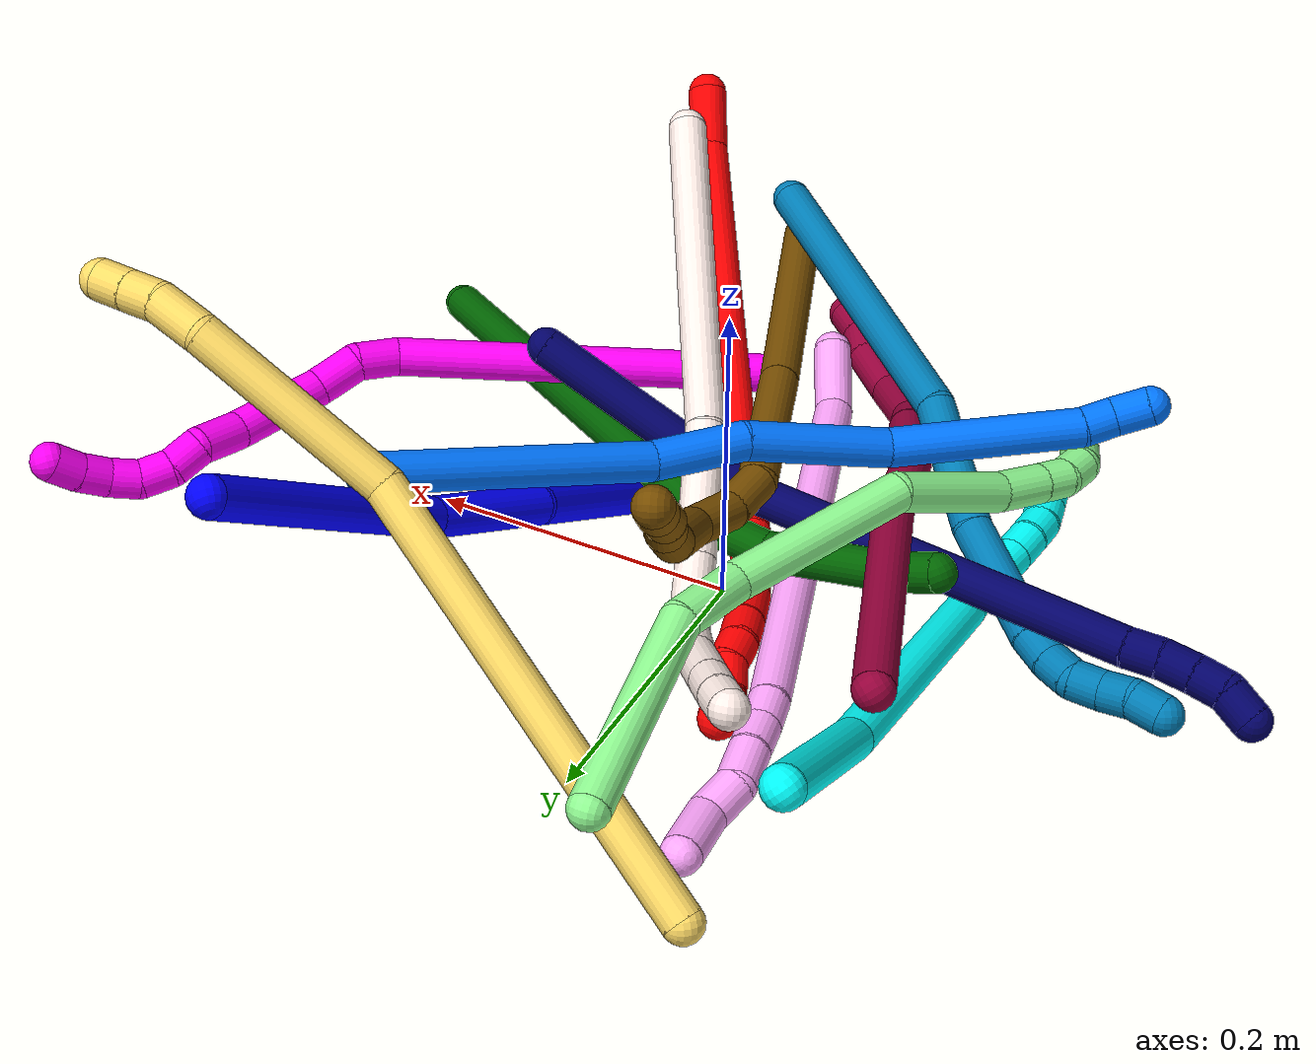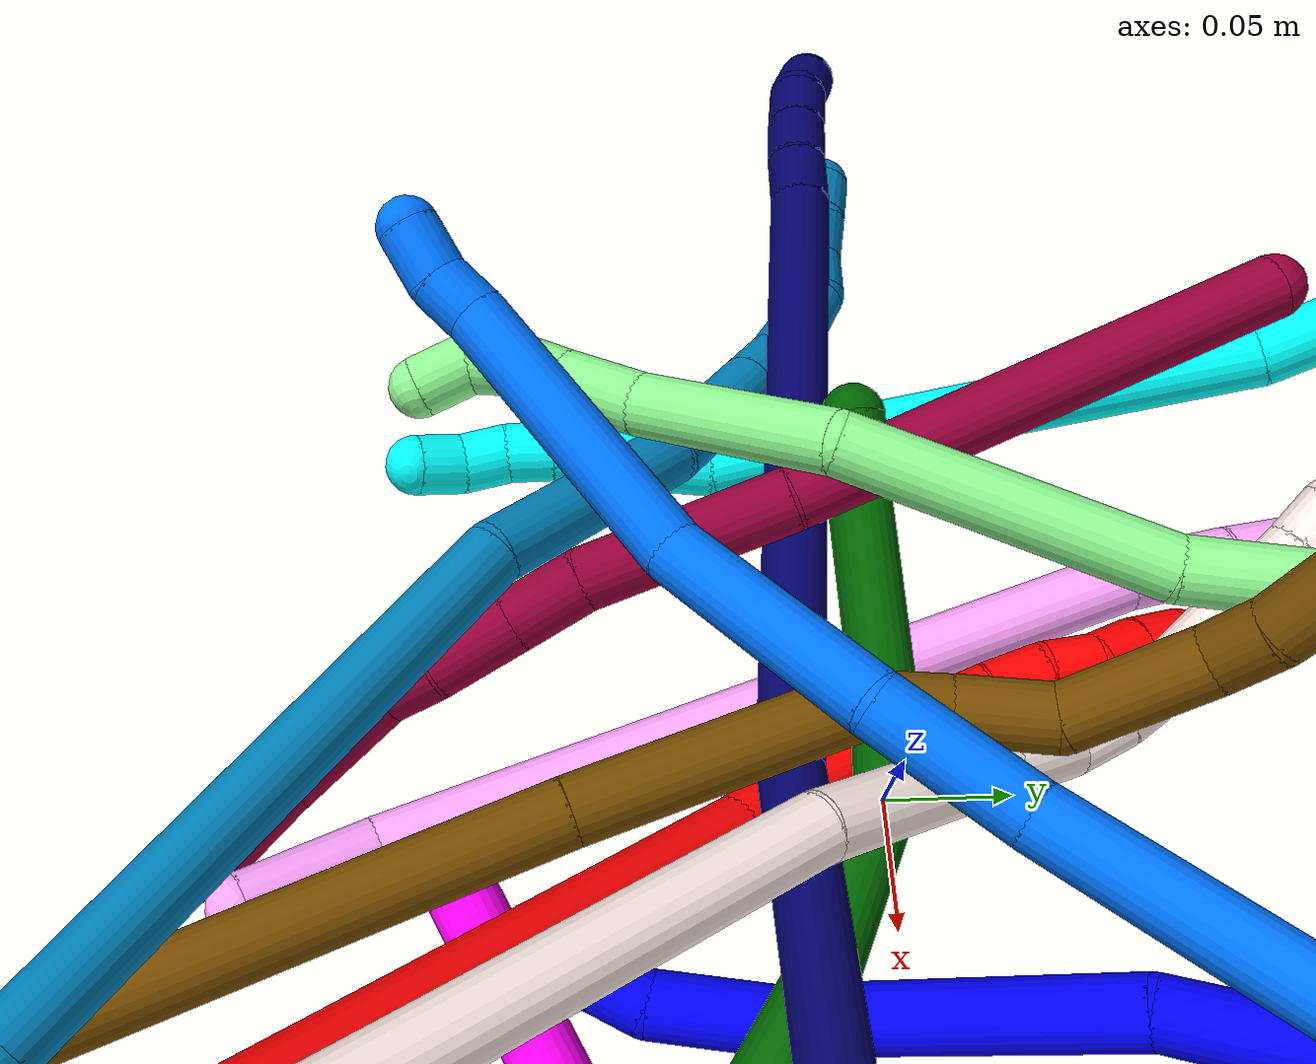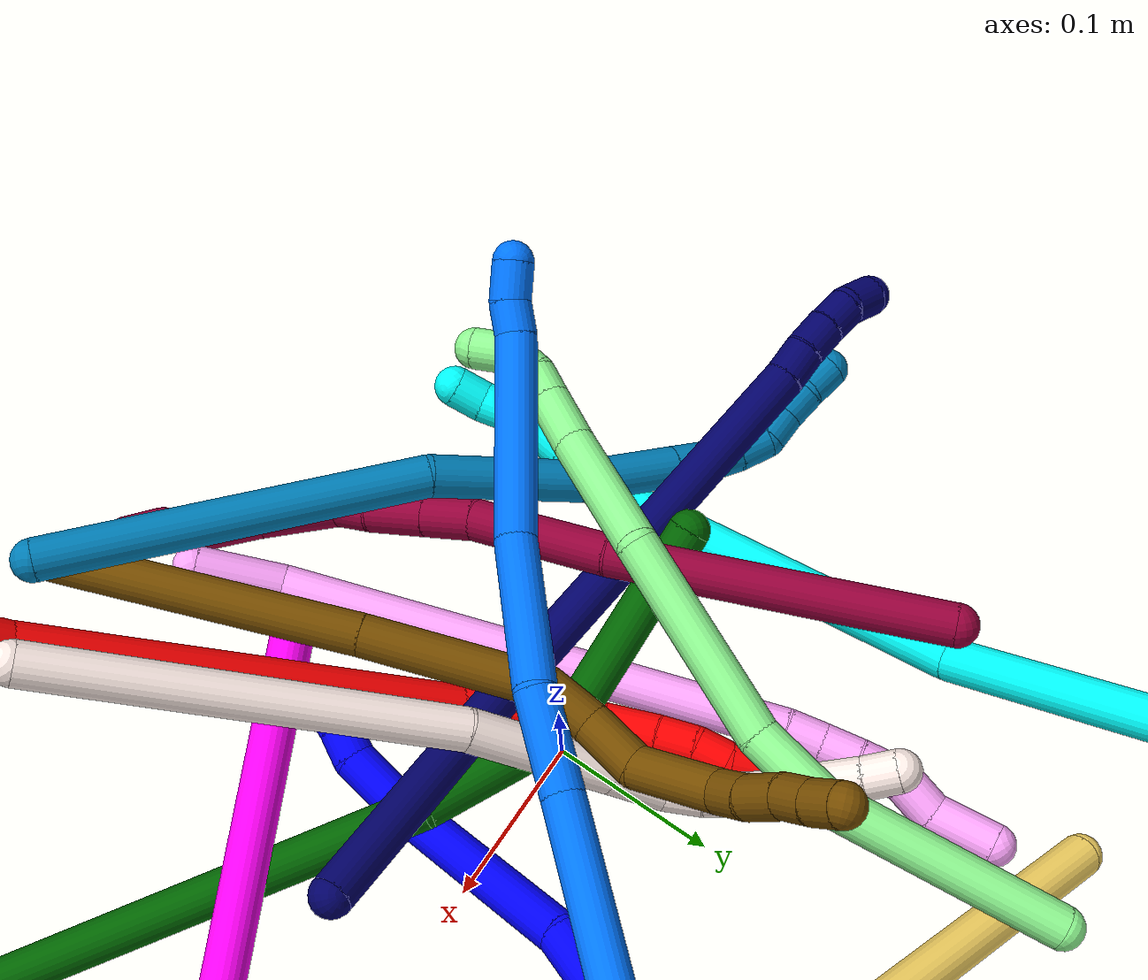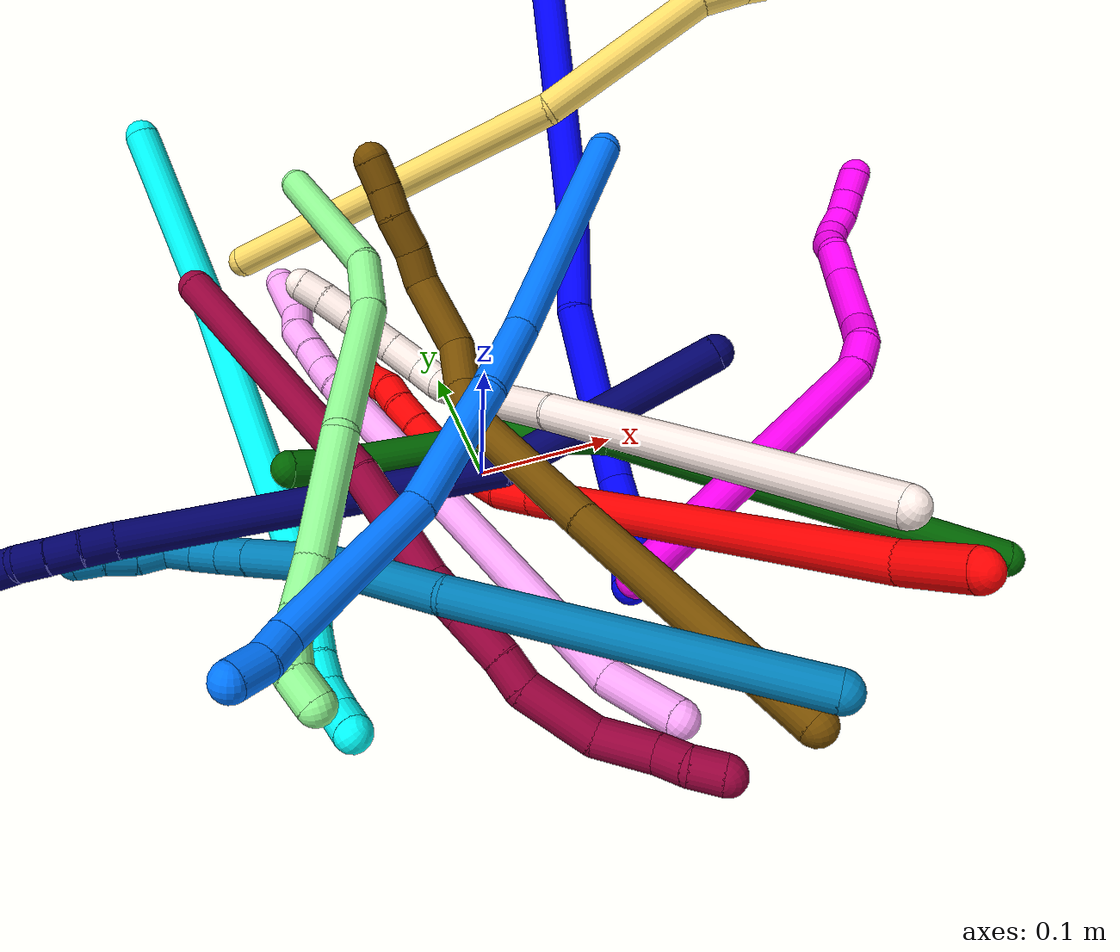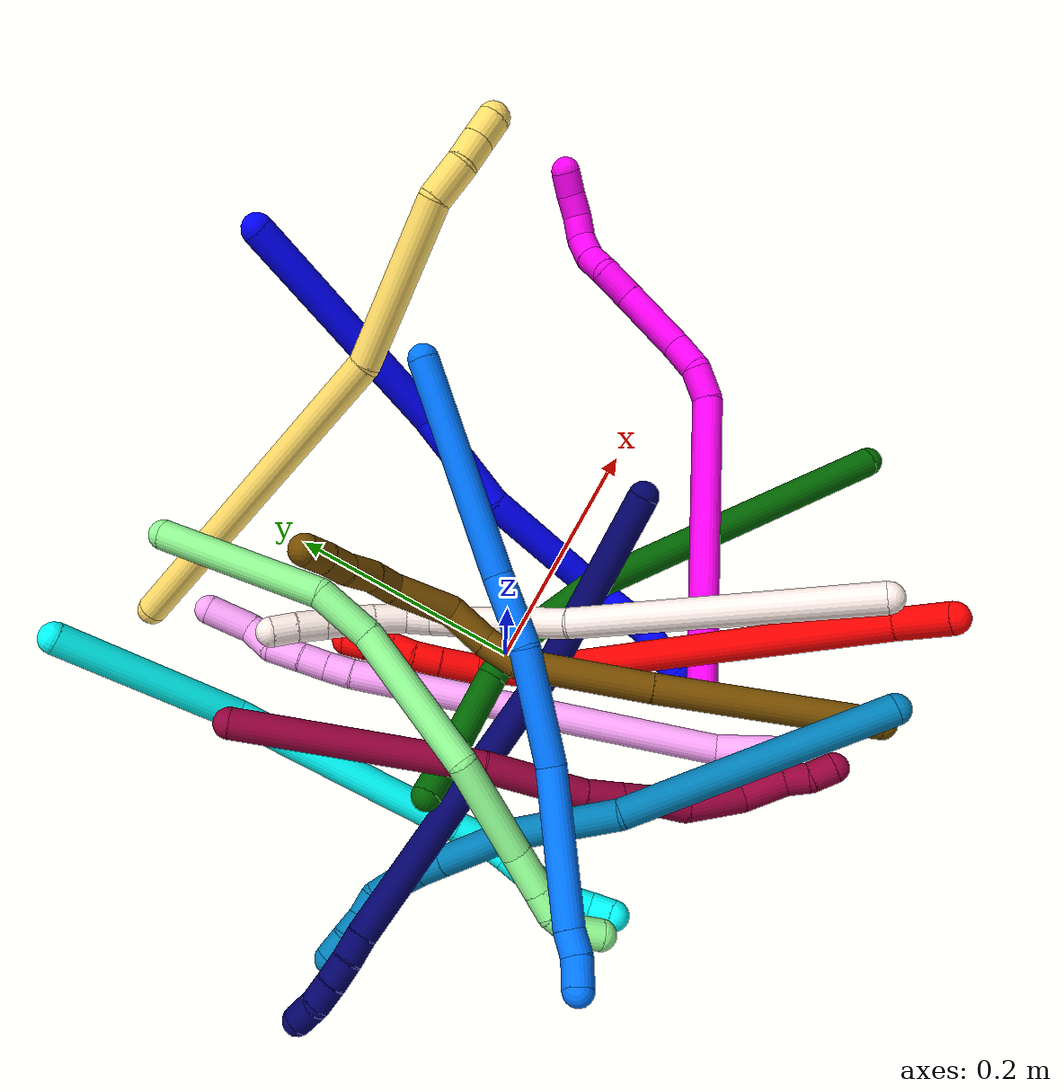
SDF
<sdf version="1.7">
 <world name="default">
  <plugin name="TubeGeneratorPlugin" filename="libtube_generator_plugin.so"/>
  <model name="photoneo_s_sensor">
   <static>1</static>
   <pose>0 0 2 1.57079 1.57079 3.14159</pose>
   <link name="link">
    <inertial><mass>0.1</mass></inertial>
    <sensor name="sensor" type="depth">
     <update_rate>30</update_rate>
     <camera>
      <horizontal_fov>1.22</horizontal_fov>
      <image><width>1920</width><height>1200</height><format>B8G8R8</format></image>
      <clip><near>0.1</near><far>4</far></clip>
      <depth_camera><output>points</output></depth_camera>
     </camera>
     <plugin name="camera_plugin" filename="libgazebo_ros_depth_camera.so">
      <baseline>0.2</baseline>
      <alwaysOn>1</alwaysOn>
      <updateRate>0.0</updateRate>
      <cameraName>camera_ir</cameraName>
      <imageTopicName>/camera/color/image_raw</imageTopicName>
      <cameraInfoTopicName>/camera/color/camera_info</cameraInfoTopicName>
      <depthImageTopicName>/camera/depth/image_raw</depthImageTopicName>
      <depthImageCameraInfoTopicName>/camera/depth/camera_info</depthImageCameraInfoTopicName>
      <pointCloudTopicName>/camera/depth/points</pointCloudTopicName>
      <frameName>fr_optical</frameName>
      <pointCloudCutoff>0.1</pointCloudCutoff>
      <pointCloudCutoffMax>2.0</pointCloudCutoffMax>
      <distortionK1>0</distortionK1>
      <distortionK2>0</distortionK2>
      <distortionK3>0</distortionK3>
      <distortionT1>0</distortionT1>
      <distortionT2>0</distortionT2>
      <CxPrime>0</CxPrime>
      <Cx>0</Cx>
      <Cy>0</Cy>
      <focalLength>0</focalLength>
      <hackBaseline>0</hackBaseline>
     </plugin>
    </sensor>
   </link>
  </model>
  <gravity>0 0 -9.8</gravity>
  <magnetic_field>6e-06 2.3e-05 -4.2e-05</magnetic_field>
  <atmosphere type="adiabatic"/>
  <physics name="default_physics" default="0" type="ode">
   <max_step_size>0.003</max_step_size>
   <real_time_factor>1</real_time_factor>
   <real_time_update_rate>1000</real_time_update_rate>
   <max_contacts>10000</max_contacts>
   <ode>
    <solver>
     <type>quick</type>
     <iters>100</iters>
     <sor>1.3</sor>
     <use_dynamic_moi_rescaling>0</use_dynamic_moi_rescaling>
    </solver>
    <constraints>
     <contact_max_correcting_vel>0</contact_max_correcting_vel>
     <contact_surface_layer>0.001</contact_surface_layer>
     <cfm>0</cfm>
     <erp>0.2</erp>
    </constraints>
   </ode>
  </physics>
  <scene><ambient>0.4 0.4 0.4 1</ambient><background>0.7 0.7 0.7 1</background><shadows>0</shadows></scene>
  <audio><device>default</device></audio>
  <spherical_coordinates>
   <surface_model>EARTH_WGS84</surface_model>
   <latitude_deg>0</latitude_deg>
   <longitude_deg>0</longitude_deg>
   <elevation>0</elevation>
   <heading_deg>0</heading_deg>
  </spherical_coordinates>
  <model name="bin">
   <static>1</static>
   <link name="bottom">
    <collision name="collision-bottom">
     <pose>0 0 -0.01 0 -0 0</pose>
     <geometry><box><size>0.8 0.6 0.02</size></box></geometry>
     <surface>
      <friction><ode><mu>100</mu><mu2>100</mu2></ode></friction>
      <contact><collide_bitmask>65535</collide_bitmask></contact>
     </surface>
    </collision>
   </link>
   <link name="west_wall">
    <collision name="collision-west_wall">
     <pose>-0.41 0 0.1 0 -0 0</pose>
     <geometry><box><size>0.02 0.6 0.2</size></box></geometry>
     <surface>
      <friction><ode><mu>100</mu><mu2>100</mu2></ode></friction>
      <contact><collide_bitmask>65535</collide_bitmask></contact>
     </surface>
    </collision>
   </link>
   <link name="east_wall">
    <collision name="collision-east_wall">
     <pose>0.41 0 0.1 0 -0 0</pose>
     <geometry><box><size>0.02 0.6 0.2</size></box></geometry>
     <surface>
      <friction><ode><mu>100</mu><mu2>100</mu2></ode></friction>
      <contact><collide_bitmask>65535</collide_bitmask></contact>
     </surface>
    </collision>
   </link>
   <link name="south_wall">
    <collision name="collision-south_wall">
     <pose>0 -0.31 0.1 0 -0 0</pose>
     <geometry><box><size>0.8 0.02 0.2</size></box></geometry>
     <surface>
      <friction><ode><mu>100</mu><mu2>100</mu2></ode></friction>
      <contact><collide_bitmask>65535</collide_bitmask></contact>
     </surface>
    </collision>
   </link>
   <link name="north_wall">
    <collision name="collision-north_wall">
     <pose>0 0.31 0.1 0 -0 0</pose>
     <geometry><box><size>0.8 0.02 0.2</size></box></geometry>
     <surface>
      <friction><ode><mu>100</mu><mu2>100</mu2></ode></friction>
      <contact><collide_bitmask>65535</collide_bitmask></contact>
     </surface>
    </collision>
   </link>
  </model>
  <model name="1">
   <static>0</static>
   <link name="1">
    <collision name="collision-cylinder-e_1_1_4">
     <pose>-0.030157 -0.092125 0.004974 1.51686 -0.315931 -0.299588</pose>
     <geometry><cylinder><radius>0.0125</radius><length>0.194125</length></cylinder></geometry>
     <surface>
      <friction><ode><mu>1.16</mu><mu2>1.16</mu2><slip1>0</slip1><slip2>0</slip2></ode></friction>
      <contact><ode><kp>1e+06</kp><kd>1</kd><max_vel>0</max_vel><min_depth>0.001</min_depth></ode></contact>
     </surface>
    </collision>
    <visual name="visual-cylinder-e_1_1_4">
     <pose>-0.030157 -0.092125 0.004974 1.51686 -0.315931 -0.299588</pose>
     <geometry><cylinder><radius>0.0125</radius><length>0.194125</length></cylinder></geometry>
     <material><ambient>0 0 1 1</ambient></material>
    </visual>
    <collision name="collision-cylinder-e_2_4_5">
     <pose>-0.083019 -0.220854 0.014388 1.45007 -0.551906 -0.49165</pose>
     <geometry><cylinder><radius>0.0125</radius><length>0.086605</length></cylinder></geometry>
     <surface>
      <friction><ode><mu>1.16</mu><mu2>1.16</mu2><slip1>0</slip1><slip2>0</slip2></ode></friction>
      <contact><ode><kp>1e+06</kp><kd>1</kd><max_vel>0</max_vel><min_depth>0.001</min_depth></ode></contact>
     </surface>
    </collision>
    <visual name="visual-cylinder-e_2_4_5">
     <pose>-0.083019 -0.220854 0.014388 1.45007 -0.551906 -0.49165</pose>
     <geometry><cylinder><radius>0.0125</radius><length>0.086605</length></cylinder></geometry>
     <material><ambient>0 0 1 1</ambient></material>
    </visual>
    <collision name="collision-cylinder-e_3_5_6">
     <pose>-0.124885 -0.318672 0.030797 1.37772 -0.298066 -0.24602</pose>
     <geometry><cylinder><radius>0.0125</radius><length>0.130499</length></cylinder></geometry>
     <surface>
      <friction><ode><mu>1.16</mu><mu2>1.16</mu2><slip1>0</slip1><slip2>0</slip2></ode></friction>
      <contact><ode><kp>1e+06</kp><kd>1</kd><max_vel>0</max_vel><min_depth>0.001</min_depth></ode></contact>
     </surface>
    </collision>
    <visual name="visual-cylinder-e_3_5_6">
     <pose>-0.124885 -0.318672 0.030797 1.37772 -0.298066 -0.24602</pose>
     <geometry><cylinder><radius>0.0125</radius><length>0.130499</length></cylinder></geometry>
     <material><ambient>0 0 1 1</ambient></material>
    </visual>
    <collision name="collision-cylinder-e_4_6_7">
     <pose>-0.157364 -0.395648 0.052493 1.01781 -0.623311 -0.355678</pose>
     <geometry><cylinder><radius>0.0125</radius><length>0.045627</length></cylinder></geometry>
     <surface>
      <friction><ode><mu>1.16</mu><mu2>1.16</mu2><slip1>0</slip1><slip2>0</slip2></ode></friction>
      <contact><ode><kp>1e+06</kp><kd>1</kd><max_vel>0</max_vel><min_depth>0.001</min_depth></ode></contact>
     </surface>
    </collision>
    <visual name="visual-cylinder-e_4_6_7">
     <pose>-0.157364 -0.395648 0.052493 1.01781 -0.623311 -0.355678</pose>
     <geometry><cylinder><radius>0.0125</radius><length>0.045627</length></cylinder></geometry>
     <material><ambient>0 0 1 1</ambient></material>
    </visual>
    <collision name="collision-cylinder-e_5_7_8">
     <pose>-0.178786 -0.416891 0.064342 1.20171 -0.943564 -0.672804</pose>
     <geometry><cylinder><radius>0.0125</radius><length>0.020022</length></cylinder></geometry>
     <surface>
      <friction><ode><mu>1.16</mu><mu2>1.16</mu2><slip1>0</slip1><slip2>0</slip2></ode></friction>
      <contact><ode><kp>1e+06</kp><kd>1</kd><max_vel>0</max_vel><min_depth>0.001</min_depth></ode></contact>
     </surface>
    </collision>
    <visual name="visual-cylinder-e_5_7_8">
     <pose>-0.178786 -0.416891 0.064342 1.20171 -0.943564 -0.672804</pose>
     <geometry><cylinder><radius>0.0125</radius><length>0.020022</length></cylinder></geometry>
     <material><ambient>0 0 1 1</ambient></material>
    </visual>
    <collision name="collision-cylinder-e_6_8_2">
     <pose>-0.195271 -0.429743 0.069477 1.18253 -0.810739 -0.561043</pose>
     <geometry><cylinder><radius>0.0125</radius><length>0.023122</length></cylinder></geometry>
     <surface>
      <friction><ode><mu>1.16</mu><mu2>1.16</mu2><slip1>0</slip1><slip2>0</slip2></ode></friction>
      <contact><ode><kp>1e+06</kp><kd>1</kd><max_vel>0</max_vel><min_depth>0.001</min_depth></ode></contact>
     </surface>
    </collision>
    <visual name="visual-cylinder-e_6_8_2">
     <pose>-0.195271 -0.429743 0.069477 1.18253 -0.810739 -0.561043</pose>
     <geometry><cylinder><radius>0.0125</radius><length>0.023122</length></cylinder></geometry>
     <material><ambient>0 0 1 1</ambient></material>
    </visual>
    <collision name="collision-sphere-2">
     <pose>-0.20365 -0.437115 0.072493 0 -0 0</pose>
     <geometry><sphere><radius>0.0125</radius></sphere></geometry>
     <surface>
      <friction><ode><mu>1.16</mu><mu2>1.16</mu2><slip1>0</slip1><slip2>0</slip2></ode></friction>
      <contact><ode><kp>1e+06</kp><kd>1</kd><max_vel>0</max_vel><min_depth>0.001</min_depth></ode></contact>
     </surface>
    </collision>
    <visual name="visual-sphere-2">
     <pose>-0.20365 -0.437115 0.072493 0 -0 0</pose>
     <geometry><sphere><radius>0.0125</radius></sphere></geometry>
     <material><ambient>0 0 1 1</ambient></material>
    </visual>
    <collision name="collision-sphere-4">
     <pose>-0.060315 -0.184249 0.009947 0 -0 0</pose>
     <geometry><sphere><radius>0.0125</radius></sphere></geometry>
     <surface>
      <friction><ode><mu>1.16</mu><mu2>1.16</mu2><slip1>0</slip1><slip2>0</slip2></ode></friction>
      <contact><ode><kp>1e+06</kp><kd>1</kd><max_vel>0</max_vel><min_depth>0.001</min_depth></ode></contact>
     </surface>
    </collision>
    <visual name="visual-sphere-4">
     <pose>-0.060315 -0.184249 0.009947 0 -0 0</pose>
     <geometry><sphere><radius>0.0125</radius></sphere></geometry>
     <material><ambient>0 0 1 1</ambient></material>
    </visual>
    <collision name="collision-sphere-1">
     <geometry><sphere><radius>0.0125</radius></sphere></geometry>
     <surface>
      <friction><ode><mu>1.16</mu><mu2>1.16</mu2><slip1>0</slip1><slip2>0</slip2></ode></friction>
      <contact><ode><kp>1e+06</kp><kd>1</kd><max_vel>0</max_vel><min_depth>0.001</min_depth></ode></contact>
     </surface>
    </collision>
    <visual name="visual-sphere-1">
     <geometry><sphere><radius>0.0125</radius></sphere></geometry>
     <material><ambient>0 0 1 1</ambient></material>
    </visual>
    <collision name="collision-sphere-8">
     <pose>-0.186891 -0.422371 0.066462 0 -0 0</pose>
     <geometry><sphere><radius>0.0125</radius></sphere></geometry>
     <surface>
      <friction><ode><mu>1.16</mu><mu2>1.16</mu2><slip1>0</slip1><slip2>0</slip2></ode></friction>
      <contact><ode><kp>1e+06</kp><kd>1</kd><max_vel>0</max_vel><min_depth>0.001</min_depth></ode></contact>
     </surface>
    </collision>
    <visual name="visual-sphere-8">
     <pose>-0.186891 -0.422371 0.066462 0 -0 0</pose>
     <geometry><sphere><radius>0.0125</radius></sphere></geometry>
     <material><ambient>0 0 1 1</ambient></material>
    </visual>
    <collision name="collision-sphere-5">
     <pose>-0.105723 -0.257459 0.018829 0 -0 0</pose>
     <geometry><sphere><radius>0.0125</radius></sphere></geometry>
     <surface>
      <friction><ode><mu>1.16</mu><mu2>1.16</mu2><slip1>0</slip1><slip2>0</slip2></ode></friction>
      <contact><ode><kp>1e+06</kp><kd>1</kd><max_vel>0</max_vel><min_depth>0.001</min_depth></ode></contact>
     </surface>
    </collision>
    <visual name="visual-sphere-5">
     <pose>-0.105723 -0.257459 0.018829 0 -0 0</pose>
     <geometry><sphere><radius>0.0125</radius></sphere></geometry>
     <material><ambient>0 0 1 1</ambient></material>
    </visual>
    <collision name="collision-sphere-6">
     <pose>-0.144047 -0.379886 0.042764 0 -0 0</pose>
     <geometry><sphere><radius>0.0125</radius></sphere></geometry>
     <surface>
      <friction><ode><mu>1.16</mu><mu2>1.16</mu2><slip1>0</slip1><slip2>0</slip2></ode></friction>
      <contact><ode><kp>1e+06</kp><kd>1</kd><max_vel>0</max_vel><min_depth>0.001</min_depth></ode></contact>
     </surface>
    </collision>
    <visual name="visual-sphere-6">
     <pose>-0.144047 -0.379886 0.042764 0 -0 0</pose>
     <geometry><sphere><radius>0.0125</radius></sphere></geometry>
     <material><ambient>0 0 1 1</ambient></material>
    </visual>
    <collision name="collision-sphere-7">
     <pose>-0.170681 -0.411411 0.062222 0 -0 0</pose>
     <geometry><sphere><radius>0.0125</radius></sphere></geometry>
     <surface>
      <friction><ode><mu>1.16</mu><mu2>1.16</mu2><slip1>0</slip1><slip2>0</slip2></ode></friction>
      <contact><ode><kp>1e+06</kp><kd>1</kd><max_vel>0</max_vel><min_depth>0.001</min_depth></ode></contact>
     </surface>
    </collision>
    <visual name="visual-sphere-7">
     <pose>-0.170681 -0.411411 0.062222 0 -0 0</pose>
     <geometry><sphere><radius>0.0125</radius></sphere></geometry>
     <material><ambient>0 0 1 1</ambient></material>
    </visual>
    <inertial>
     <pose>-0.089232 -0.229866 0.023041 0 -0 0</pose>
     <mass>0.5</mass>
     <inertia>
      <ixx>0.000529</ixx>
      <ixy>0</ixy>
      <ixz>0</ixz>
      <iyy>-0.000113</iyy>
      <iyz>0</iyz>
      <izz>0.001113</izz>
     </inertia>
    </inertial>
   </link>
   <pose>0.156693 0.29882 0.213049 0.932279 0.409623 0.540116</pose>
  </model>
  <model name="2">
   <static>0</static>
   <link name="2">
    <collision name="collision-cylinder-e_1_1_4">
     <pose>-0.007089 0.006173 -0.018913 -2.8261 -0.342307 1.65376</pose>
     <geometry><cylinder><radius>0.0125</radius><length>0.04224</length></cylinder></geometry>
     <surface>
      <friction><ode><mu>1.16</mu><mu2>1.16</mu2><slip1>0</slip1><slip2>0</slip2></ode></friction>
      <contact><ode><kp>1e+06</kp><kd>1</kd><max_vel>0</max_vel><min_depth>0.001</min_depth></ode></contact>
     </surface>
    </collision>
    <visual name="visual-cylinder-e_1_1_4">
     <pose>-0.007089 0.006173 -0.018913 -2.8261 -0.342307 1.65376</pose>
     <geometry><cylinder><radius>0.0125</radius><length>0.04224</length></cylinder></geometry>
     <material><ambient>1 0 0 1</ambient></material>
    </visual>
    <collision name="collision-cylinder-e_2_4_5">
     <pose>-0.0576 0.068244 -0.144201 -2.65777 -0.34674 1.23449</pose>
     <geometry><cylinder><radius>0.0125</radius><length>0.255546</length></cylinder></geometry>
     <surface>
      <friction><ode><mu>1.16</mu><mu2>1.16</mu2><slip1>0</slip1><slip2>0</slip2></ode></friction>
      <contact><ode><kp>1e+06</kp><kd>1</kd><max_vel>0</max_vel><min_depth>0.001</min_depth></ode></contact>
     </surface>
    </collision>
    <visual name="visual-cylinder-e_2_4_5">
     <pose>-0.0576 0.068244 -0.144201 -2.65777 -0.34674 1.23449</pose>
     <geometry><cylinder><radius>0.0125</radius><length>0.255546</length></cylinder></geometry>
     <material><ambient>1 0 0 1</ambient></material>
    </visual>
    <collision name="collision-cylinder-e_3_5_6">
     <pose>-0.106614 0.132302 -0.261652 -2.50658 -0.386172 1.07343</pose>
     <geometry><cylinder><radius>0.0125</radius><length>0.029699</length></cylinder></geometry>
     <surface>
      <friction><ode><mu>1.16</mu><mu2>1.16</mu2><slip1>0</slip1><slip2>0</slip2></ode></friction>
      <contact><ode><kp>1e+06</kp><kd>1</kd><max_vel>0</max_vel><min_depth>0.001</min_depth></ode></contact>
     </surface>
    </collision>
    <visual name="visual-cylinder-e_3_5_6">
     <pose>-0.106614 0.132302 -0.261652 -2.50658 -0.386172 1.07343</pose>
     <geometry><cylinder><radius>0.0125</radius><length>0.029699</length></cylinder></geometry>
     <material><ambient>1 0 0 1</ambient></material>
    </visual>
    <collision name="collision-cylinder-e_4_6_7">
     <pose>-0.115739 0.159676 -0.29289 -2.3803 -0.126153 0.313092</pose>
     <geometry><cylinder><radius>0.0125</radius><length>0.056151</length></cylinder></geometry>
     <surface>
      <friction><ode><mu>1.16</mu><mu2>1.16</mu2><slip1>0</slip1><slip2>0</slip2></ode></friction>
      <contact><ode><kp>1e+06</kp><kd>1</kd><max_vel>0</max_vel><min_depth>0.001</min_depth></ode></contact>
     </surface>
    </collision>
    <visual name="visual-cylinder-e_4_6_7">
     <pose>-0.115739 0.159676 -0.29289 -2.3803 -0.126153 0.313092</pose>
     <geometry><cylinder><radius>0.0125</radius><length>0.056151</length></cylinder></geometry>
     <material><ambient>1 0 0 1</ambient></material>
    </visual>
    <collision name="collision-cylinder-e_5_7_8">
     <pose>-0.117388 0.192709 -0.321934 -2.14197 0.114187 -0.208578</pose>
     <geometry><cylinder><radius>0.0125</radius><length>0.033068</length></cylinder></geometry>
     <surface>
      <friction><ode><mu>1.16</mu><mu2>1.16</mu2><slip1>0</slip1><slip2>0</slip2></ode></friction>
      <contact><ode><kp>1e+06</kp><kd>1</kd><max_vel>0</max_vel><min_depth>0.001</min_depth></ode></contact>
     </surface>
    </collision>
    <visual name="visual-cylinder-e_5_7_8">
     <pose>-0.117388 0.192709 -0.321934 -2.14197 0.114187 -0.208578</pose>
     <geometry><cylinder><radius>0.0125</radius><length>0.033068</length></cylinder></geometry>
     <material><ambient>1 0 0 1</ambient></material>
    </visual>
    <collision name="collision-cylinder-e_6_8_9">
     <pose>-0.114096 0.215446 -0.337612 -2.22212 0.124938 -0.251335</pose>
     <geometry><cylinder><radius>0.0125</radius><length>0.022603</length></cylinder></geometry>
     <surface>
      <friction><ode><mu>1.16</mu><mu2>1.16</mu2><slip1>0</slip1><slip2>0</slip2></ode></friction>
      <contact><ode><kp>1e+06</kp><kd>1</kd><max_vel>0</max_vel><min_depth>0.001</min_depth></ode></contact>
     </surface>
    </collision>
    <visual name="visual-cylinder-e_6_8_9">
     <pose>-0.114096 0.215446 -0.337612 -2.22212 0.124938 -0.251335</pose>
     <geometry><cylinder><radius>0.0125</radius><length>0.022603</length></cylinder></geometry>
     <material><ambient>1 0 0 1</ambient></material>
    </visual>
    <collision name="collision-cylinder-e_7_9_10">
     <pose>-0.110558 0.230867 -0.351745 -2.41628 0.213944 -0.551584</pose>
     <geometry><cylinder><radius>0.0125</radius><length>0.020063</length></cylinder></geometry>
     <surface>
      <friction><ode><mu>1.16</mu><mu2>1.16</mu2><slip1>0</slip1><slip2>0</slip2></ode></friction>
      <contact><ode><kp>1e+06</kp><kd>1</kd><max_vel>0</max_vel><min_depth>0.001</min_depth></ode></contact>
     </surface>
    </collision>
    <visual name="visual-cylinder-e_7_9_10">
     <pose>-0.110558 0.230867 -0.351745 -2.41628 0.213944 -0.551584</pose>
     <geometry><cylinder><radius>0.0125</radius><length>0.020063</length></cylinder></geometry>
     <material><ambient>1 0 0 1</ambient></material>
    </visual>
    <collision name="collision-cylinder-e_8_10_11">
     <pose>-0.109797 0.243626 -0.367164 -2.4829 -0.133177 0.385374</pose>
     <geometry><cylinder><radius>0.0125</radius><length>0.020625</length></cylinder></geometry>
     <surface>
      <friction><ode><mu>1.16</mu><mu2>1.16</mu2><slip1>0</slip1><slip2>0</slip2></ode></friction>
      <contact><ode><kp>1e+06</kp><kd>1</kd><max_vel>0</max_vel><min_depth>0.001</min_depth></ode></contact>
     </surface>
    </collision>
    <visual name="visual-cylinder-e_8_10_11">
     <pose>-0.109797 0.243626 -0.367164 -2.4829 -0.133177 0.385374</pose>
     <geometry><cylinder><radius>0.0125</radius><length>0.020625</length></cylinder></geometry>
     <material><ambient>1 0 0 1</ambient></material>
    </visual>
    <collision name="collision-cylinder-e_9_11_2">
     <pose>-0.110738 0.25566 -0.3834 -2.52505 0.042854 -0.134401</pose>
     <geometry><cylinder><radius>0.0125</radius><length>0.020006</length></cylinder></geometry>
     <surface>
      <friction><ode><mu>1.16</mu><mu2>1.16</mu2><slip1>0</slip1><slip2>0</slip2></ode></friction>
      <contact><ode><kp>1e+06</kp><kd>1</kd><max_vel>0</max_vel><min_depth>0.001</min_depth></ode></contact>
     </surface>
    </collision>
    <visual name="visual-cylinder-e_9_11_2">
     <pose>-0.110738 0.25566 -0.3834 -2.52505 0.042854 -0.134401</pose>
     <geometry><cylinder><radius>0.0125</radius><length>0.020006</length></cylinder></geometry>
     <material><ambient>1 0 0 1</ambient></material>
    </visual>
    <collision name="collision-sphere-2">
     <pose>-0.110309 0.261439 -0.391554 0 -0 0</pose>
     <geometry><sphere><radius>0.0125</radius></sphere></geometry>
     <surface>
      <friction><ode><mu>1.16</mu><mu2>1.16</mu2><slip1>0</slip1><slip2>0</slip2></ode></friction>
      <contact><ode><kp>1e+06</kp><kd>1</kd><max_vel>0</max_vel><min_depth>0.001</min_depth></ode></contact>
     </surface>
    </collision>
    <visual name="visual-sphere-2">
     <pose>-0.110309 0.261439 -0.391554 0 -0 0</pose>
     <geometry><sphere><radius>0.0125</radius></sphere></geometry>
     <material><ambient>1 0 0 1</ambient></material>
    </visual>
    <collision name="collision-sphere-11">
     <pose>-0.111167 0.249882 -0.375246 0 -0 0</pose>
     <geometry><sphere><radius>0.0125</radius></sphere></geometry>
     <surface>
      <friction><ode><mu>1.16</mu><mu2>1.16</mu2><slip1>0</slip1><slip2>0</slip2></ode></friction>
      <contact><ode><kp>1e+06</kp><kd>1</kd><max_vel>0</max_vel><min_depth>0.001</min_depth></ode></contact>
     </surface>
    </collision>
    <visual name="visual-sphere-11">
     <pose>-0.111167 0.249882 -0.375246 0 -0 0</pose>
     <geometry><sphere><radius>0.0125</radius></sphere></geometry>
     <material><ambient>1 0 0 1</ambient></material>
    </visual>
    <collision name="collision-sphere-10">
     <pose>-0.108428 0.237369 -0.359081 0 -0 0</pose>
     <geometry><sphere><radius>0.0125</radius></sphere></geometry>
     <surface>
      <friction><ode><mu>1.16</mu><mu2>1.16</mu2><slip1>0</slip1><slip2>0</slip2></ode></friction>
      <contact><ode><kp>1e+06</kp><kd>1</kd><max_vel>0</max_vel><min_depth>0.001</min_depth></ode></contact>
     </surface>
    </collision>
    <visual name="visual-sphere-10">
     <pose>-0.108428 0.237369 -0.359081 0 -0 0</pose>
     <geometry><sphere><radius>0.0125</radius></sphere></geometry>
     <material><ambient>1 0 0 1</ambient></material>
    </visual>
    <collision name="collision-sphere-9">
     <pose>-0.112688 0.224364 -0.34441 0 -0 0</pose>
     <geometry><sphere><radius>0.0125</radius></sphere></geometry>
     <surface>
      <friction><ode><mu>1.16</mu><mu2>1.16</mu2><slip1>0</slip1><slip2>0</slip2></ode></friction>
      <contact><ode><kp>1e+06</kp><kd>1</kd><max_vel>0</max_vel><min_depth>0.001</min_depth></ode></contact>
     </surface>
    </collision>
    <visual name="visual-sphere-9">
     <pose>-0.112688 0.224364 -0.34441 0 -0 0</pose>
     <geometry><sphere><radius>0.0125</radius></sphere></geometry>
     <material><ambient>1 0 0 1</ambient></material>
    </visual>
    <collision name="collision-sphere-4">
     <pose>-0.014178 0.012346 -0.037825 0 -0 0</pose>
     <geometry><sphere><radius>0.0125</radius></sphere></geometry>
     <surface>
      <friction><ode><mu>1.16</mu><mu2>1.16</mu2><slip1>0</slip1><slip2>0</slip2></ode></friction>
      <contact><ode><kp>1e+06</kp><kd>1</kd><max_vel>0</max_vel><min_depth>0.001</min_depth></ode></contact>
     </surface>
    </collision>
    <visual name="visual-sphere-4">
     <pose>-0.014178 0.012346 -0.037825 0 -0 0</pose>
     <geometry><sphere><radius>0.0125</radius></sphere></geometry>
     <material><ambient>1 0 0 1</ambient></material>
    </visual>
    <collision name="collision-sphere-1">
     <geometry><sphere><radius>0.0125</radius></sphere></geometry>
     <surface>
      <friction><ode><mu>1.16</mu><mu2>1.16</mu2><slip1>0</slip1><slip2>0</slip2></ode></friction>
      <contact><ode><kp>1e+06</kp><kd>1</kd><max_vel>0</max_vel><min_depth>0.001</min_depth></ode></contact>
     </surface>
    </collision>
    <visual name="visual-sphere-1">
     <geometry><sphere><radius>0.0125</radius></sphere></geometry>
     <material><ambient>1 0 0 1</ambient></material>
    </visual>
    <collision name="collision-sphere-8">
     <pose>-0.115504 0.206528 -0.330814 0 -0 0</pose>
     <geometry><sphere><radius>0.0125</radius></sphere></geometry>
     <surface>
      <friction><ode><mu>1.16</mu><mu2>1.16</mu2><slip1>0</slip1><slip2>0</slip2></ode></friction>
      <contact><ode><kp>1e+06</kp><kd>1</kd><max_vel>0</max_vel><min_depth>0.001</min_depth></ode></contact>
     </surface>
    </collision>
    <visual name="visual-sphere-8">
     <pose>-0.115504 0.206528 -0.330814 0 -0 0</pose>
     <geometry><sphere><radius>0.0125</radius></sphere></geometry>
     <material><ambient>1 0 0 1</ambient></material>
    </visual>
    <collision name="collision-sphere-5">
     <pose>-0.101021 0.124143 -0.250578 0 -0 0</pose>
     <geometry><sphere><radius>0.0125</radius></sphere></geometry>
     <surface>
      <friction><ode><mu>1.16</mu><mu2>1.16</mu2><slip1>0</slip1><slip2>0</slip2></ode></friction>
      <contact><ode><kp>1e+06</kp><kd>1</kd><max_vel>0</max_vel><min_depth>0.001</min_depth></ode></contact>
     </surface>
    </collision>
    <visual name="visual-sphere-5">
     <pose>-0.101021 0.124143 -0.250578 0 -0 0</pose>
     <geometry><sphere><radius>0.0125</radius></sphere></geometry>
     <material><ambient>1 0 0 1</ambient></material>
    </visual>
    <collision name="collision-sphere-6">
     <pose>-0.112207 0.140462 -0.272726 0 -0 0</pose>
     <geometry><sphere><radius>0.0125</radius></sphere></geometry>
     <surface>
      <friction><ode><mu>1.16</mu><mu2>1.16</mu2><slip1>0</slip1><slip2>0</slip2></ode></friction>
      <contact><ode><kp>1e+06</kp><kd>1</kd><max_vel>0</max_vel><min_depth>0.001</min_depth></ode></contact>
     </surface>
    </collision>
    <visual name="visual-sphere-6">
     <pose>-0.112207 0.140462 -0.272726 0 -0 0</pose>
     <geometry><sphere><radius>0.0125</radius></sphere></geometry>
     <material><ambient>1 0 0 1</ambient></material>
    </visual>
    <collision name="collision-sphere-7">
     <pose>-0.119272 0.17889 -0.313053 0 -0 0</pose>
     <geometry><sphere><radius>0.0125</radius></sphere></geometry>
     <surface>
      <friction><ode><mu>1.16</mu><mu2>1.16</mu2><slip1>0</slip1><slip2>0</slip2></ode></friction>
      <contact><ode><kp>1e+06</kp><kd>1</kd><max_vel>0</max_vel><min_depth>0.001</min_depth></ode></contact>
     </surface>
    </collision>
    <visual name="visual-sphere-7">
     <pose>-0.119272 0.17889 -0.313053 0 -0 0</pose>
     <geometry><sphere><radius>0.0125</radius></sphere></geometry>
     <material><ambient>1 0 0 1</ambient></material>
    </visual>
    <inertial>
     <pose>-0.075686 0.113218 -0.204885 0 -0 0</pose>
     <mass>0.5</mass>
     <inertia>
      <ixx>0.00171</ixx>
      <ixy>0</ixy>
      <ixz>0</ixz>
      <iyy>0.001061</iyy>
      <iyz>0</iyz>
      <izz>-0.000186</izz>
     </inertia>
    </inertial>
   </link>
   <pose>0.15529 -0.280542 0.174541 0.705572 -0.43548 0.384952</pose>
  </model>
  <model name="3">
   <static>0</static>
   <link name="3">
    <collision name="collision-cylinder-e_1_1_4">
     <pose>-0.013039 -0.074394 0.009941 1.43796 -0.172009 -0.15064</pose>
     <geometry><cylinder><radius>0.0125</radius><length>0.152358</length></cylinder></geometry>
     <surface>
      <friction><ode><mu>1.16</mu><mu2>1.16</mu2><slip1>0</slip1><slip2>0</slip2></ode></friction>
      <contact><ode><kp>1e+06</kp><kd>1</kd><max_vel>0</max_vel><min_depth>0.001</min_depth></ode></contact>
     </surface>
    </collision>
    <visual name="visual-cylinder-e_1_1_4">
     <pose>-0.013039 -0.074394 0.009941 1.43796 -0.172009 -0.15064</pose>
     <geometry><cylinder><radius>0.0125</radius><length>0.152358</length></cylinder></geometry>
     <material><ambient>0.003922 1 0.996078 1</ambient></material>
    </visual>
    <collision name="collision-cylinder-e_2_4_5">
     <pose>-0.017869 -0.247804 0.019027 1.57943 0.082715 0.083431</pose>
     <geometry><cylinder><radius>0.0125</radius><length>0.19872</length></cylinder></geometry>
     <surface>
      <friction><ode><mu>1.16</mu><mu2>1.16</mu2><slip1>0</slip1><slip2>0</slip2></ode></friction>
      <contact><ode><kp>1e+06</kp><kd>1</kd><max_vel>0</max_vel><min_depth>0.001</min_depth></ode></contact>
     </surface>
    </collision>
    <visual name="visual-cylinder-e_2_4_5">
     <pose>-0.017869 -0.247804 0.019027 1.57943 0.082715 0.083431</pose>
     <geometry><cylinder><radius>0.0125</radius><length>0.19872</length></cylinder></geometry>
     <material><ambient>0.003922 1 0.996078 1</ambient></material>
    </visual>
    <collision name="collision-cylinder-e_3_5_6">
     <pose>-0.008881 -0.358292 0.017376 1.64002 0.067639 0.072487</pose>
     <geometry><cylinder><radius>0.0125</radius><length>0.02305</length></cylinder></geometry>
     <surface>
      <friction><ode><mu>1.16</mu><mu2>1.16</mu2><slip1>0</slip1><slip2>0</slip2></ode></friction>
      <contact><ode><kp>1e+06</kp><kd>1</kd><max_vel>0</max_vel><min_depth>0.001</min_depth></ode></contact>
     </surface>
    </collision>
    <visual name="visual-cylinder-e_3_5_6">
     <pose>-0.008881 -0.358292 0.017376 1.64002 0.067639 0.072487</pose>
     <geometry><cylinder><radius>0.0125</radius><length>0.02305</length></cylinder></geometry>
     <material><ambient>0.003922 1 0.996078 1</ambient></material>
    </visual>
    <collision name="collision-cylinder-e_4_6_7">
     <pose>-0.003012 -0.381391 0.015361 1.67531 0.410532 0.454376</pose>
     <geometry><cylinder><radius>0.0125</radius><length>0.025503</length></cylinder></geometry>
     <surface>
      <friction><ode><mu>1.16</mu><mu2>1.16</mu2><slip1>0</slip1><slip2>0</slip2></ode></friction>
      <contact><ode><kp>1e+06</kp><kd>1</kd><max_vel>0</max_vel><min_depth>0.001</min_depth></ode></contact>
     </surface>
    </collision>
    <visual name="visual-cylinder-e_4_6_7">
     <pose>-0.003012 -0.381391 0.015361 1.67531 0.410532 0.454376</pose>
     <geometry><cylinder><radius>0.0125</radius><length>0.025503</length></cylinder></geometry>
     <material><ambient>0.003922 1 0.996078 1</ambient></material>
    </visual>
    <collision name="collision-cylinder-e_5_7_8">
     <pose>0.006246 -0.402176 0.013765 1.61186 0.426942 0.444272</pose>
     <geometry><cylinder><radius>0.0125</radius><length>0.020137</length></cylinder></geometry>
     <surface>
      <friction><ode><mu>1.16</mu><mu2>1.16</mu2><slip1>0</slip1><slip2>0</slip2></ode></friction>
      <contact><ode><kp>1e+06</kp><kd>1</kd><max_vel>0</max_vel><min_depth>0.001</min_depth></ode></contact>
     </surface>
    </collision>
    <visual name="visual-cylinder-e_5_7_8">
     <pose>0.006246 -0.402176 0.013765 1.61186 0.426942 0.444272</pose>
     <geometry><cylinder><radius>0.0125</radius><length>0.020137</length></cylinder></geometry>
     <material><ambient>0.003922 1 0.996078 1</ambient></material>
    </visual>
    <collision name="collision-cylinder-e_6_8_9">
     <pose>0.014511 -0.420523 0.012389 1.67917 0.417127 0.463362</pose>
     <geometry><cylinder><radius>0.0125</radius><length>0.02022</length></cylinder></geometry>
     <surface>
      <friction><ode><mu>1.16</mu><mu2>1.16</mu2><slip1>0</slip1><slip2>0</slip2></ode></friction>
      <contact><ode><kp>1e+06</kp><kd>1</kd><max_vel>0</max_vel><min_depth>0.001</min_depth></ode></contact>
     </surface>
    </collision>
    <visual name="visual-cylinder-e_6_8_9">
     <pose>0.014511 -0.420523 0.012389 1.67917 0.417127 0.463362</pose>
     <geometry><cylinder><radius>0.0125</radius><length>0.02022</length></cylinder></geometry>
     <material><ambient>0.003922 1 0.996078 1</ambient></material>
    </visual>
    <collision name="collision-cylinder-e_7_9_10">
     <pose>0.021239 -0.439334 0.010645 1.64802 0.26618 0.287289</pose>
     <geometry><cylinder><radius>0.0125</radius><length>0.020007</length></cylinder></geometry>
     <surface>
      <friction><ode><mu>1.16</mu><mu2>1.16</mu2><slip1>0</slip1><slip2>0</slip2></ode></friction>
      <contact><ode><kp>1e+06</kp><kd>1</kd><max_vel>0</max_vel><min_depth>0.001</min_depth></ode></contact>
     </surface>
    </collision>
    <visual name="visual-cylinder-e_7_9_10">
     <pose>0.021239 -0.439334 0.010645 1.64802 0.26618 0.287289</pose>
     <geometry><cylinder><radius>0.0125</radius><length>0.020007</length></cylinder></geometry>
     <material><ambient>0.003922 1 0.996078 1</ambient></material>
    </visual>
    <collision name="collision-cylinder-e_8_10_11">
     <pose>0.025179 -0.458449 0.007039 1.86352 0.131274 0.176464</pose>
     <geometry><cylinder><radius>0.0125</radius><length>0.02</length></cylinder></geometry>
     <surface>
      <friction><ode><mu>1.16</mu><mu2>1.16</mu2><slip1>0</slip1><slip2>0</slip2></ode></friction>
      <contact><ode><kp>1e+06</kp><kd>1</kd><max_vel>0</max_vel><min_depth>0.001</min_depth></ode></contact>
     </surface>
    </collision>
    <visual name="visual-cylinder-e_8_10_11">
     <pose>0.025179 -0.458449 0.007039 1.86352 0.131274 0.176464</pose>
     <geometry><cylinder><radius>0.0125</radius><length>0.02</length></cylinder></geometry>
     <material><ambient>0.003922 1 0.996078 1</ambient></material>
    </visual>
    <collision name="collision-cylinder-e_9_11_2">
     <pose>0.030291 -0.475826 -0.000659 2.12118 0.390065 0.678674</pose>
     <geometry><cylinder><radius>0.0125</radius><length>0.020003</length></cylinder></geometry>
     <surface>
      <friction><ode><mu>1.16</mu><mu2>1.16</mu2><slip1>0</slip1><slip2>0</slip2></ode></friction>
      <contact><ode><kp>1e+06</kp><kd>1</kd><max_vel>0</max_vel><min_depth>0.001</min_depth></ode></contact>
     </surface>
    </collision>
    <visual name="visual-cylinder-e_9_11_2">
     <pose>0.030291 -0.475826 -0.000659 2.12118 0.390065 0.678674</pose>
     <geometry><cylinder><radius>0.0125</radius><length>0.020003</length></cylinder></geometry>
     <material><ambient>0.003922 1 0.996078 1</ambient></material>
    </visual>
    <collision name="collision-sphere-2">
     <pose>0.034094 -0.48371 -0.005498 0 -0 0</pose>
     <geometry><sphere><radius>0.0125</radius></sphere></geometry>
     <surface>
      <friction><ode><mu>1.16</mu><mu2>1.16</mu2><slip1>0</slip1><slip2>0</slip2></ode></friction>
      <contact><ode><kp>1e+06</kp><kd>1</kd><max_vel>0</max_vel><min_depth>0.001</min_depth></ode></contact>
     </surface>
    </collision>
    <visual name="visual-sphere-2">
     <pose>0.034094 -0.48371 -0.005498 0 -0 0</pose>
     <geometry><sphere><radius>0.0125</radius></sphere></geometry>
     <material><ambient>0.003922 1 0.996078 1</ambient></material>
    </visual>
    <collision name="collision-sphere-11">
     <pose>0.026488 -0.467942 0.004179 0 -0 0</pose>
     <geometry><sphere><radius>0.0125</radius></sphere></geometry>
     <surface>
      <friction><ode><mu>1.16</mu><mu2>1.16</mu2><slip1>0</slip1><slip2>0</slip2></ode></friction>
      <contact><ode><kp>1e+06</kp><kd>1</kd><max_vel>0</max_vel><min_depth>0.001</min_depth></ode></contact>
     </surface>
    </collision>
    <visual name="visual-sphere-11">
     <pose>0.026488 -0.467942 0.004179 0 -0 0</pose>
     <geometry><sphere><radius>0.0125</radius></sphere></geometry>
     <material><ambient>0.003922 1 0.996078 1</ambient></material>
    </visual>
    <collision name="collision-sphere-10">
     <pose>0.02387 -0.448957 0.0099 0 -0 0</pose>
     <geometry><sphere><radius>0.0125</radius></sphere></geometry>
     <surface>
      <friction><ode><mu>1.16</mu><mu2>1.16</mu2><slip1>0</slip1><slip2>0</slip2></ode></friction>
      <contact><ode><kp>1e+06</kp><kd>1</kd><max_vel>0</max_vel><min_depth>0.001</min_depth></ode></contact>
     </surface>
    </collision>
    <visual name="visual-sphere-10">
     <pose>0.02387 -0.448957 0.0099 0 -0 0</pose>
     <geometry><sphere><radius>0.0125</radius></sphere></geometry>
     <material><ambient>0.003922 1 0.996078 1</ambient></material>
    </visual>
    <collision name="collision-sphere-9">
     <pose>0.018607 -0.429712 0.011389 0 -0 0</pose>
     <geometry><sphere><radius>0.0125</radius></sphere></geometry>
     <surface>
      <friction><ode><mu>1.16</mu><mu2>1.16</mu2><slip1>0</slip1><slip2>0</slip2></ode></friction>
      <contact><ode><kp>1e+06</kp><kd>1</kd><max_vel>0</max_vel><min_depth>0.001</min_depth></ode></contact>
     </surface>
    </collision>
    <visual name="visual-sphere-9">
     <pose>0.018607 -0.429712 0.011389 0 -0 0</pose>
     <geometry><sphere><radius>0.0125</radius></sphere></geometry>
     <material><ambient>0.003922 1 0.996078 1</ambient></material>
    </visual>
    <collision name="collision-sphere-4">
     <pose>-0.026078 -0.148787 0.019882 0 -0 0</pose>
     <geometry><sphere><radius>0.0125</radius></sphere></geometry>
     <surface>
      <friction><ode><mu>1.16</mu><mu2>1.16</mu2><slip1>0</slip1><slip2>0</slip2></ode></friction>
      <contact><ode><kp>1e+06</kp><kd>1</kd><max_vel>0</max_vel><min_depth>0.001</min_depth></ode></contact>
     </surface>
    </collision>
    <visual name="visual-sphere-4">
     <pose>-0.026078 -0.148787 0.019882 0 -0 0</pose>
     <geometry><sphere><radius>0.0125</radius></sphere></geometry>
     <material><ambient>0.003922 1 0.996078 1</ambient></material>
    </visual>
    <collision name="collision-sphere-1">
     <geometry><sphere><radius>0.0125</radius></sphere></geometry>
     <surface>
      <friction><ode><mu>1.16</mu><mu2>1.16</mu2><slip1>0</slip1><slip2>0</slip2></ode></friction>
      <contact><ode><kp>1e+06</kp><kd>1</kd><max_vel>0</max_vel><min_depth>0.001</min_depth></ode></contact>
     </surface>
    </collision>
    <visual name="visual-sphere-1">
     <geometry><sphere><radius>0.0125</radius></sphere></geometry>
     <material><ambient>0.003922 1 0.996078 1</ambient></material>
    </visual>
    <collision name="collision-sphere-8">
     <pose>0.010415 -0.411334 0.013389 0 -0 0</pose>
     <geometry><sphere><radius>0.0125</radius></sphere></geometry>
     <surface>
      <friction><ode><mu>1.16</mu><mu2>1.16</mu2><slip1>0</slip1><slip2>0</slip2></ode></friction>
      <contact><ode><kp>1e+06</kp><kd>1</kd><max_vel>0</max_vel><min_depth>0.001</min_depth></ode></contact>
     </surface>
    </collision>
    <visual name="visual-sphere-8">
     <pose>0.010415 -0.411334 0.013389 0 -0 0</pose>
     <geometry><sphere><radius>0.0125</radius></sphere></geometry>
     <material><ambient>0.003922 1 0.996078 1</ambient></material>
    </visual>
    <collision name="collision-sphere-5">
     <pose>-0.009659 -0.346821 0.018172 0 -0 0</pose>
     <geometry><sphere><radius>0.0125</radius></sphere></geometry>
     <surface>
      <friction><ode><mu>1.16</mu><mu2>1.16</mu2><slip1>0</slip1><slip2>0</slip2></ode></friction>
      <contact><ode><kp>1e+06</kp><kd>1</kd><max_vel>0</max_vel><min_depth>0.001</min_depth></ode></contact>
     </surface>
    </collision>
    <visual name="visual-sphere-5">
     <pose>-0.009659 -0.346821 0.018172 0 -0 0</pose>
     <geometry><sphere><radius>0.0125</radius></sphere></geometry>
     <material><ambient>0.003922 1 0.996078 1</ambient></material>
    </visual>
    <collision name="collision-sphere-6">
     <pose>-0.008102 -0.369763 0.016581 0 -0 0</pose>
     <geometry><sphere><radius>0.0125</radius></sphere></geometry>
     <surface>
      <friction><ode><mu>1.16</mu><mu2>1.16</mu2><slip1>0</slip1><slip2>0</slip2></ode></friction>
      <contact><ode><kp>1e+06</kp><kd>1</kd><max_vel>0</max_vel><min_depth>0.001</min_depth></ode></contact>
     </surface>
    </collision>
    <visual name="visual-sphere-6">
     <pose>-0.008102 -0.369763 0.016581 0 -0 0</pose>
     <geometry><sphere><radius>0.0125</radius></sphere></geometry>
     <material><ambient>0.003922 1 0.996078 1</ambient></material>
    </visual>
    <collision name="collision-sphere-7">
     <pose>0.002077 -0.393019 0.014141 0 -0 0</pose>
     <geometry><sphere><radius>0.0125</radius></sphere></geometry>
     <surface>
      <friction><ode><mu>1.16</mu><mu2>1.16</mu2><slip1>0</slip1><slip2>0</slip2></ode></friction>
      <contact><ode><kp>1e+06</kp><kd>1</kd><max_vel>0</max_vel><min_depth>0.001</min_depth></ode></contact>
     </surface>
    </collision>
    <visual name="visual-sphere-7">
     <pose>0.002077 -0.393019 0.014141 0 -0 0</pose>
     <geometry><sphere><radius>0.0125</radius></sphere></geometry>
     <material><ambient>0.003922 1 0.996078 1</ambient></material>
    </visual>
    <inertial>
     <pose>-0.007731 -0.245285 0.013912 0 -0 0</pose>
     <mass>0.5</mass>
     <inertia>
      <ixx>0.000977</ixx>
      <ixy>0</ixy>
      <ixz>0</ixz>
      <iyy>2.2e-05</iyy>
      <iyz>0</iyz>
      <izz>0.000957</izz>
     </inertia>
    </inertial>
   </link>
   <pose>-0.173306 0.287921 0.140897 2.71087 -0.738052 -2.73921</pose>
  </model>
  <model name="4">
   <static>0</static>
   <link name="4">
    <collision name="collision-cylinder-e_1_1_4">
     <pose>0.004407 0.020574 -0.016943 -2.25972 0.163883 -0.344597</pose>
     <geometry><cylinder><radius>0.0125</radius><length>0.054029</length></cylinder></geometry>
     <surface>
      <friction><ode><mu>1.16</mu><mu2>1.16</mu2><slip1>0</slip1><slip2>0</slip2></ode></friction>
      <contact><ode><kp>1e+06</kp><kd>1</kd><max_vel>0</max_vel><min_depth>0.001</min_depth></ode></contact>
     </surface>
    </collision>
    <visual name="visual-cylinder-e_1_1_4">
     <pose>0.004407 0.020574 -0.016943 -2.25972 0.163883 -0.344597</pose>
     <geometry><cylinder><radius>0.0125</radius><length>0.054029</length></cylinder></geometry>
     <material><ambient>1 0.65098 0.996078 1</ambient></material>
    </visual>
    <collision name="collision-cylinder-e_2_4_5">
     <pose>-0.013799 0.142846 -0.147864 -2.41306 -0.146975 0.38148</pose>
     <geometry><cylinder><radius>0.0125</radius><length>0.308836</length></cylinder></geometry>
     <surface>
      <friction><ode><mu>1.16</mu><mu2>1.16</mu2><slip1>0</slip1><slip2>0</slip2></ode></friction>
      <contact><ode><kp>1e+06</kp><kd>1</kd><max_vel>0</max_vel><min_depth>0.001</min_depth></ode></contact>
     </surface>
    </collision>
    <visual name="visual-cylinder-e_2_4_5">
     <pose>-0.013799 0.142846 -0.147864 -2.41306 -0.146975 0.38148</pose>
     <geometry><cylinder><radius>0.0125</radius><length>0.308836</length></cylinder></geometry>
     <material><ambient>1 0.65098 0.996078 1</ambient></material>
    </visual>
    <collision name="collision-cylinder-e_3_5_6">
     <pose>-0.038346 0.252634 -0.269013 -2.29621 -0.176949 0.389425</pose>
     <geometry><cylinder><radius>0.0125</radius><length>0.021965</length></cylinder></geometry>
     <surface>
      <friction><ode><mu>1.16</mu><mu2>1.16</mu2><slip1>0</slip1><slip2>0</slip2></ode></friction>
      <contact><ode><kp>1e+06</kp><kd>1</kd><max_vel>0</max_vel><min_depth>0.001</min_depth></ode></contact>
     </surface>
    </collision>
    <visual name="visual-cylinder-e_3_5_6">
     <pose>-0.038346 0.252634 -0.269013 -2.29621 -0.176949 0.389425</pose>
     <geometry><cylinder><radius>0.0125</radius><length>0.021965</length></cylinder></geometry>
     <material><ambient>1 0.65098 0.996078 1</ambient></material>
    </visual>
    <collision name="collision-cylinder-e_4_6_7">
     <pose>-0.043007 0.268638 -0.283631 -2.32562 -0.245938 0.557009</pose>
     <geometry><cylinder><radius>0.0125</radius><length>0.022406</length></cylinder></geometry>
     <surface>
      <friction><ode><mu>1.16</mu><mu2>1.16</mu2><slip1>0</slip1><slip2>0</slip2></ode></friction>
      <contact><ode><kp>1e+06</kp><kd>1</kd><max_vel>0</max_vel><min_depth>0.001</min_depth></ode></contact>
     </surface>
    </collision>
    <visual name="visual-cylinder-e_4_6_7">
     <pose>-0.043007 0.268638 -0.283631 -2.32562 -0.245938 0.557009</pose>
     <geometry><cylinder><radius>0.0125</radius><length>0.022406</length></cylinder></geometry>
     <material><ambient>1 0.65098 0.996078 1</ambient></material>
    </visual>
    <collision name="collision-cylinder-e_5_7_8">
     <pose>-0.04819 0.287509 -0.299611 -2.23262 -0.174979 0.355254</pose>
     <geometry><cylinder><radius>0.0125</radius><length>0.028209</length></cylinder></geometry>
     <surface>
      <friction><ode><mu>1.16</mu><mu2>1.16</mu2><slip1>0</slip1><slip2>0</slip2></ode></friction>
      <contact><ode><kp>1e+06</kp><kd>1</kd><max_vel>0</max_vel><min_depth>0.001</min_depth></ode></contact>
     </surface>
    </collision>
    <visual name="visual-cylinder-e_5_7_8">
     <pose>-0.04819 0.287509 -0.299611 -2.23262 -0.174979 0.355254</pose>
     <geometry><cylinder><radius>0.0125</radius><length>0.028209</length></cylinder></geometry>
     <material><ambient>1 0.65098 0.996078 1</ambient></material>
    </visual>
    <collision name="collision-cylinder-e_6_8_9">
     <pose>-0.055427 0.309787 -0.311578 -1.86506 -0.384118 0.512708</pose>
     <geometry><cylinder><radius>0.0125</radius><length>0.025519</length></cylinder></geometry>
     <surface>
      <friction><ode><mu>1.16</mu><mu2>1.16</mu2><slip1>0</slip1><slip2>0</slip2></ode></friction>
      <contact><ode><kp>1e+06</kp><kd>1</kd><max_vel>0</max_vel><min_depth>0.001</min_depth></ode></contact>
     </surface>
    </collision>
    <visual name="visual-cylinder-e_6_8_9">
     <pose>-0.055427 0.309787 -0.311578 -1.86506 -0.384118 0.512708</pose>
     <geometry><cylinder><radius>0.0125</radius><length>0.025519</length></cylinder></geometry>
     <material><ambient>1 0.65098 0.996078 1</ambient></material>
    </visual>
    <collision name="collision-cylinder-e_7_9_2">
     <pose>-0.067124 0.334154 -0.327775 -2.34537 -0.362142 0.821136</pose>
     <geometry><cylinder><radius>0.0125</radius><length>0.039037</length></cylinder></geometry>
     <surface>
      <friction><ode><mu>1.16</mu><mu2>1.16</mu2><slip1>0</slip1><slip2>0</slip2></ode></friction>
      <contact><ode><kp>1e+06</kp><kd>1</kd><max_vel>0</max_vel><min_depth>0.001</min_depth></ode></contact>
     </surface>
    </collision>
    <visual name="visual-cylinder-e_7_9_2">
     <pose>-0.067124 0.334154 -0.327775 -2.34537 -0.362142 0.821136</pose>
     <geometry><cylinder><radius>0.0125</radius><length>0.039037</length></cylinder></geometry>
     <material><ambient>1 0.65098 0.996078 1</ambient></material>
    </visual>
    <collision name="collision-sphere-2">
     <pose>-0.074038 0.347199 -0.340541 0 -0 0</pose>
     <geometry><sphere><radius>0.0125</radius></sphere></geometry>
     <surface>
      <friction><ode><mu>1.16</mu><mu2>1.16</mu2><slip1>0</slip1><slip2>0</slip2></ode></friction>
      <contact><ode><kp>1e+06</kp><kd>1</kd><max_vel>0</max_vel><min_depth>0.001</min_depth></ode></contact>
     </surface>
    </collision>
    <visual name="visual-sphere-2">
     <pose>-0.074038 0.347199 -0.340541 0 -0 0</pose>
     <geometry><sphere><radius>0.0125</radius></sphere></geometry>
     <material><ambient>1 0.65098 0.996078 1</ambient></material>
    </visual>
    <collision name="collision-sphere-9">
     <pose>-0.060209 0.321109 -0.315009 0 -0 0</pose>
     <geometry><sphere><radius>0.0125</radius></sphere></geometry>
     <surface>
      <friction><ode><mu>1.16</mu><mu2>1.16</mu2><slip1>0</slip1><slip2>0</slip2></ode></friction>
      <contact><ode><kp>1e+06</kp><kd>1</kd><max_vel>0</max_vel><min_depth>0.001</min_depth></ode></contact>
     </surface>
    </collision>
    <visual name="visual-sphere-9">
     <pose>-0.060209 0.321109 -0.315009 0 -0 0</pose>
     <geometry><sphere><radius>0.0125</radius></sphere></geometry>
     <material><ambient>1 0.65098 0.996078 1</ambient></material>
    </visual>
    <collision name="collision-sphere-4">
     <pose>0.008815 0.041148 -0.033886 0 -0 0</pose>
     <geometry><sphere><radius>0.0125</radius></sphere></geometry>
     <surface>
      <friction><ode><mu>1.16</mu><mu2>1.16</mu2><slip1>0</slip1><slip2>0</slip2></ode></friction>
      <contact><ode><kp>1e+06</kp><kd>1</kd><max_vel>0</max_vel><min_depth>0.001</min_depth></ode></contact>
     </surface>
    </collision>
    <visual name="visual-sphere-4">
     <pose>0.008815 0.041148 -0.033886 0 -0 0</pose>
     <geometry><sphere><radius>0.0125</radius></sphere></geometry>
     <material><ambient>1 0.65098 0.996078 1</ambient></material>
    </visual>
    <collision name="collision-sphere-1">
     <geometry><sphere><radius>0.0125</radius></sphere></geometry>
     <surface>
      <friction><ode><mu>1.16</mu><mu2>1.16</mu2><slip1>0</slip1><slip2>0</slip2></ode></friction>
      <contact><ode><kp>1e+06</kp><kd>1</kd><max_vel>0</max_vel><min_depth>0.001</min_depth></ode></contact>
     </surface>
    </collision>
    <visual name="visual-sphere-1">
     <geometry><sphere><radius>0.0125</radius></sphere></geometry>
     <material><ambient>1 0.65098 0.996078 1</ambient></material>
    </visual>
    <collision name="collision-sphere-8">
     <pose>-0.050645 0.298466 -0.308147 0 -0 0</pose>
     <geometry><sphere><radius>0.0125</radius></sphere></geometry>
     <surface>
      <friction><ode><mu>1.16</mu><mu2>1.16</mu2><slip1>0</slip1><slip2>0</slip2></ode></friction>
      <contact><ode><kp>1e+06</kp><kd>1</kd><max_vel>0</max_vel><min_depth>0.001</min_depth></ode></contact>
     </surface>
    </collision>
    <visual name="visual-sphere-8">
     <pose>-0.050645 0.298466 -0.308147 0 -0 0</pose>
     <geometry><sphere><radius>0.0125</radius></sphere></geometry>
     <material><ambient>1 0.65098 0.996078 1</ambient></material>
    </visual>
    <collision name="collision-sphere-5">
     <pose>-0.036413 0.244545 -0.261841 0 -0 0</pose>
     <geometry><sphere><radius>0.0125</radius></sphere></geometry>
     <surface>
      <friction><ode><mu>1.16</mu><mu2>1.16</mu2><slip1>0</slip1><slip2>0</slip2></ode></friction>
      <contact><ode><kp>1e+06</kp><kd>1</kd><max_vel>0</max_vel><min_depth>0.001</min_depth></ode></contact>
     </surface>
    </collision>
    <visual name="visual-sphere-5">
     <pose>-0.036413 0.244545 -0.261841 0 -0 0</pose>
     <geometry><sphere><radius>0.0125</radius></sphere></geometry>
     <material><ambient>1 0.65098 0.996078 1</ambient></material>
    </visual>
    <collision name="collision-sphere-6">
     <pose>-0.04028 0.260724 -0.276186 0 -0 0</pose>
     <geometry><sphere><radius>0.0125</radius></sphere></geometry>
     <surface>
      <friction><ode><mu>1.16</mu><mu2>1.16</mu2><slip1>0</slip1><slip2>0</slip2></ode></friction>
      <contact><ode><kp>1e+06</kp><kd>1</kd><max_vel>0</max_vel><min_depth>0.001</min_depth></ode></contact>
     </surface>
    </collision>
    <visual name="visual-sphere-6">
     <pose>-0.04028 0.260724 -0.276186 0 -0 0</pose>
     <geometry><sphere><radius>0.0125</radius></sphere></geometry>
     <material><ambient>1 0.65098 0.996078 1</ambient></material>
    </visual>
    <collision name="collision-sphere-7">
     <pose>-0.045735 0.276553 -0.291076 0 -0 0</pose>
     <geometry><sphere><radius>0.0125</radius></sphere></geometry>
     <surface>
      <friction><ode><mu>1.16</mu><mu2>1.16</mu2><slip1>0</slip1><slip2>0</slip2></ode></friction>
      <contact><ode><kp>1e+06</kp><kd>1</kd><max_vel>0</max_vel><min_depth>0.001</min_depth></ode></contact>
     </surface>
    </collision>
    <visual name="visual-sphere-7">
     <pose>-0.045735 0.276553 -0.291076 0 -0 0</pose>
     <geometry><sphere><radius>0.0125</radius></sphere></geometry>
     <material><ambient>1 0.65098 0.996078 1</ambient></material>
    </visual>
    <inertial>
     <pose>-0.022447 0.171712 -0.176086 0 -0 0</pose>
     <mass>0.5</mass>
     <inertia>
      <ixx>0.003197</ixx>
      <ixy>0</ixy>
      <ixz>0</ixz>
      <iyy>-0.000694</iyy>
      <iyz>0</iyz>
      <izz>-0.001311</izz>
     </inertia>
    </inertial>
   </link>
   <pose>0.036449 -0.23856 0.027508 -2.21011 0.684445 -2.66268</pose>
  </model>
  <model name="5">
   <static>0</static>
   <link name="5">
    <collision name="collision-cylinder-e_1_1_4">
     <pose>0.104814 0.089388 -0.048406 -2.06711 0.800704 -1.23542</pose>
     <geometry><cylinder><radius>0.0125</radius><length>0.292022</length></cylinder></geometry>
     <surface>
      <friction><ode><mu>1.16</mu><mu2>1.16</mu2><slip1>0</slip1><slip2>0</slip2></ode></friction>
      <contact><ode><kp>1e+06</kp><kd>1</kd><max_vel>0</max_vel><min_depth>0.001</min_depth></ode></contact>
     </surface>
    </collision>
    <visual name="visual-cylinder-e_1_1_4">
     <pose>0.104814 0.089388 -0.048406 -2.06711 0.800704 -1.23542</pose>
     <geometry><cylinder><radius>0.0125</radius><length>0.292022</length></cylinder></geometry>
     <material><ambient>1 0.858824 0.4 1</ambient></material>
    </visual>
    <collision name="collision-cylinder-e_2_4_5">
     <pose>0.247347 0.215521 -0.137531 -2.40744 0.602435 -1.35917</pose>
     <geometry><cylinder><radius>0.0125</radius><length>0.133131</length></cylinder></geometry>
     <surface>
      <friction><ode><mu>1.16</mu><mu2>1.16</mu2><slip1>0</slip1><slip2>0</slip2></ode></friction>
      <contact><ode><kp>1e+06</kp><kd>1</kd><max_vel>0</max_vel><min_depth>0.001</min_depth></ode></contact>
     </surface>
    </collision>
    <visual name="visual-cylinder-e_2_4_5">
     <pose>0.247347 0.215521 -0.137531 -2.40744 0.602435 -1.35917</pose>
     <geometry><cylinder><radius>0.0125</radius><length>0.133131</length></cylinder></geometry>
     <material><ambient>1 0.858824 0.4 1</ambient></material>
    </visual>
    <collision name="collision-cylinder-e_3_5_6">
     <pose>0.298074 0.257724 -0.186584 -2.56187 0.917204 -2.0547</pose>
     <geometry><cylinder><radius>0.0125</radius><length>0.032769</length></cylinder></geometry>
     <surface>
      <friction><ode><mu>1.16</mu><mu2>1.16</mu2><slip1>0</slip1><slip2>0</slip2></ode></friction>
      <contact><ode><kp>1e+06</kp><kd>1</kd><max_vel>0</max_vel><min_depth>0.001</min_depth></ode></contact>
     </surface>
    </collision>
    <visual name="visual-cylinder-e_3_5_6">
     <pose>0.298074 0.257724 -0.186584 -2.56187 0.917204 -2.0547</pose>
     <geometry><cylinder><radius>0.0125</radius><length>0.032769</length></cylinder></geometry>
     <material><ambient>1 0.858824 0.4 1</ambient></material>
    </visual>
    <collision name="collision-cylinder-e_4_6_7">
     <pose>0.31927 0.264344 -0.20157 -2.96859 0.881233 -2.77785</pose>
     <geometry><cylinder><radius>0.0125</radius><length>0.021228</length></cylinder></geometry>
     <surface>
      <friction><ode><mu>1.16</mu><mu2>1.16</mu2><slip1>0</slip1><slip2>0</slip2></ode></friction>
      <contact><ode><kp>1e+06</kp><kd>1</kd><max_vel>0</max_vel><min_depth>0.001</min_depth></ode></contact>
     </surface>
    </collision>
    <visual name="visual-cylinder-e_4_6_7">
     <pose>0.31927 0.264344 -0.20157 -2.96859 0.881233 -2.77785</pose>
     <geometry><cylinder><radius>0.0125</radius><length>0.021228</length></cylinder></geometry>
     <material><ambient>1 0.858824 0.4 1</ambient></material>
    </visual>
    <collision name="collision-cylinder-e_5_7_2">
     <pose>0.335635 0.266631 -0.214592 -2.96679 0.901433 -2.78335</pose>
     <geometry><cylinder><radius>0.0125</radius><length>0.02085</length></cylinder></geometry>
     <surface>
      <friction><ode><mu>1.16</mu><mu2>1.16</mu2><slip1>0</slip1><slip2>0</slip2></ode></friction>
      <contact><ode><kp>1e+06</kp><kd>1</kd><max_vel>0</max_vel><min_depth>0.001</min_depth></ode></contact>
     </surface>
    </collision>
    <visual name="visual-cylinder-e_5_7_2">
     <pose>0.335635 0.266631 -0.214592 -2.96679 0.901433 -2.78335</pose>
     <geometry><cylinder><radius>0.0125</radius><length>0.02085</length></cylinder></geometry>
     <material><ambient>1 0.858824 0.4 1</ambient></material>
    </visual>
    <collision name="collision-sphere-2">
     <pose>0.34381 0.267756 -0.220962 0 -0 0</pose>
     <geometry><sphere><radius>0.0125</radius></sphere></geometry>
     <surface>
      <friction><ode><mu>1.16</mu><mu2>1.16</mu2><slip1>0</slip1><slip2>0</slip2></ode></friction>
      <contact><ode><kp>1e+06</kp><kd>1</kd><max_vel>0</max_vel><min_depth>0.001</min_depth></ode></contact>
     </surface>
    </collision>
    <visual name="visual-sphere-2">
     <pose>0.34381 0.267756 -0.220962 0 -0 0</pose>
     <geometry><sphere><radius>0.0125</radius></sphere></geometry>
     <material><ambient>1 0.858824 0.4 1</ambient></material>
    </visual>
    <collision name="collision-sphere-7">
     <pose>0.327459 0.265506 -0.208222 0 -0 0</pose>
     <geometry><sphere><radius>0.0125</radius></sphere></geometry>
     <surface>
      <friction><ode><mu>1.16</mu><mu2>1.16</mu2><slip1>0</slip1><slip2>0</slip2></ode></friction>
      <contact><ode><kp>1e+06</kp><kd>1</kd><max_vel>0</max_vel><min_depth>0.001</min_depth></ode></contact>
     </surface>
    </collision>
    <visual name="visual-sphere-7">
     <pose>0.327459 0.265506 -0.208222 0 -0 0</pose>
     <geometry><sphere><radius>0.0125</radius></sphere></geometry>
     <material><ambient>1 0.858824 0.4 1</ambient></material>
    </visual>
    <collision name="collision-sphere-6">
     <pose>0.311082 0.263181 -0.194919 0 -0 0</pose>
     <geometry><sphere><radius>0.0125</radius></sphere></geometry>
     <surface>
      <friction><ode><mu>1.16</mu><mu2>1.16</mu2><slip1>0</slip1><slip2>0</slip2></ode></friction>
      <contact><ode><kp>1e+06</kp><kd>1</kd><max_vel>0</max_vel><min_depth>0.001</min_depth></ode></contact>
     </surface>
    </collision>
    <visual name="visual-sphere-6">
     <pose>0.311082 0.263181 -0.194919 0 -0 0</pose>
     <geometry><sphere><radius>0.0125</radius></sphere></geometry>
     <material><ambient>1 0.858824 0.4 1</ambient></material>
    </visual>
    <collision name="collision-sphere-5">
     <pose>0.285066 0.252267 -0.178249 0 -0 0</pose>
     <geometry><sphere><radius>0.0125</radius></sphere></geometry>
     <surface>
      <friction><ode><mu>1.16</mu><mu2>1.16</mu2><slip1>0</slip1><slip2>0</slip2></ode></friction>
      <contact><ode><kp>1e+06</kp><kd>1</kd><max_vel>0</max_vel><min_depth>0.001</min_depth></ode></contact>
     </surface>
    </collision>
    <visual name="visual-sphere-5">
     <pose>0.285066 0.252267 -0.178249 0 -0 0</pose>
     <geometry><sphere><radius>0.0125</radius></sphere></geometry>
     <material><ambient>1 0.858824 0.4 1</ambient></material>
    </visual>
    <collision name="collision-sphere-1">
     <geometry><sphere><radius>0.0125</radius></sphere></geometry>
     <surface>
      <friction><ode><mu>1.16</mu><mu2>1.16</mu2><slip1>0</slip1><slip2>0</slip2></ode></friction>
      <contact><ode><kp>1e+06</kp><kd>1</kd><max_vel>0</max_vel><min_depth>0.001</min_depth></ode></contact>
     </surface>
    </collision>
    <visual name="visual-sphere-1">
     <geometry><sphere><radius>0.0125</radius></sphere></geometry>
     <material><ambient>1 0.858824 0.4 1</ambient></material>
    </visual>
    <collision name="collision-sphere-4">
     <pose>0.209627 0.178776 -0.096813 0 -0 0</pose>
     <geometry><sphere><radius>0.0125</radius></sphere></geometry>
     <surface>
      <friction><ode><mu>1.16</mu><mu2>1.16</mu2><slip1>0</slip1><slip2>0</slip2></ode></friction>
      <contact><ode><kp>1e+06</kp><kd>1</kd><max_vel>0</max_vel><min_depth>0.001</min_depth></ode></contact>
     </surface>
    </collision>
    <visual name="visual-sphere-4">
     <pose>0.209627 0.178776 -0.096813 0 -0 0</pose>
     <geometry><sphere><radius>0.0125</radius></sphere></geometry>
     <material><ambient>1 0.858824 0.4 1</ambient></material>
    </visual>
    <inertial>
     <pose>0.174161 0.148824 -0.094625 0 -0 0</pose>
     <mass>0.5</mass>
     <inertia>
      <ixx>-0.001001</ixx>
      <ixy>0</ixy>
      <ixz>0</ixz>
      <iyy>-0.00055</iyy>
      <iyz>0</iyz>
      <izz>-0.003026</izz>
     </inertia>
    </inertial>
   </link>
   <pose>-0.114847 0.279846 0.012281 1.63394 0.150912 -0.713329</pose>
  </model>
  <model name="6">
   <static>0</static>
   <link name="6">
    <collision name="collision-cylinder-e_1_1_4">
     <pose>0.01175 -0.00789 -0.0045 2.08916 0.912702 1.40336</pose>
     <geometry><cylinder><radius>0.0125</radius><length>0.029703</length></cylinder></geometry>
     <surface>
      <friction><ode><mu>1.16</mu><mu2>1.16</mu2><slip1>0</slip1><slip2>0</slip2></ode></friction>
      <contact><ode><kp>1e+06</kp><kd>1</kd><max_vel>0</max_vel><min_depth>0.001</min_depth></ode></contact>
     </surface>
    </collision>
    <visual name="visual-cylinder-e_1_1_4">
     <pose>0.01175 -0.00789 -0.0045 2.08916 0.912702 1.40336</pose>
     <geometry><cylinder><radius>0.0125</radius><length>0.029703</length></cylinder></geometry>
     <material><ambient>0 0.392157 0.003922 1</ambient></material>
    </visual>
    <collision name="collision-cylinder-e_2_4_5">
     <pose>0.052448 -0.038461 -0.027341 2.25079 0.781619 1.42401</pose>
     <geometry><cylinder><radius>0.0125</radius><length>0.08219</length></cylinder></geometry>
     <surface>
      <friction><ode><mu>1.16</mu><mu2>1.16</mu2><slip1>0</slip1><slip2>0</slip2></ode></friction>
      <contact><ode><kp>1e+06</kp><kd>1</kd><max_vel>0</max_vel><min_depth>0.001</min_depth></ode></contact>
     </surface>
    </collision>
    <visual name="visual-cylinder-e_2_4_5">
     <pose>0.052448 -0.038461 -0.027341 2.25079 0.781619 1.42401</pose>
     <geometry><cylinder><radius>0.0125</radius><length>0.08219</length></cylinder></geometry>
     <material><ambient>0 0.392157 0.003922 1</ambient></material>
    </visual>
    <collision name="collision-cylinder-e_3_5_6">
     <pose>0.092022 -0.068506 -0.057 2.56468 0.66665 1.7245</pose>
     <geometry><cylinder><radius>0.0125</radius><length>0.034363</length></cylinder></geometry>
     <surface>
      <friction><ode><mu>1.16</mu><mu2>1.16</mu2><slip1>0</slip1><slip2>0</slip2></ode></friction>
      <contact><ode><kp>1e+06</kp><kd>1</kd><max_vel>0</max_vel><min_depth>0.001</min_depth></ode></contact>
     </surface>
    </collision>
    <visual name="visual-cylinder-e_3_5_6">
     <pose>0.092022 -0.068506 -0.057 2.56468 0.66665 1.7245</pose>
     <geometry><cylinder><radius>0.0125</radius><length>0.034363</length></cylinder></geometry>
     <material><ambient>0 0.392157 0.003922 1</ambient></material>
    </visual>
    <collision name="collision-cylinder-e_4_6_7">
     <pose>0.130062 -0.079656 -0.096282 3.00706 0.770964 2.81255</pose>
     <geometry><cylinder><radius>0.0125</radius><length>0.07869</length></cylinder></geometry>
     <surface>
      <friction><ode><mu>1.16</mu><mu2>1.16</mu2><slip1>0</slip1><slip2>0</slip2></ode></friction>
      <contact><ode><kp>1e+06</kp><kd>1</kd><max_vel>0</max_vel><min_depth>0.001</min_depth></ode></contact>
     </surface>
    </collision>
    <visual name="visual-cylinder-e_4_6_7">
     <pose>0.130062 -0.079656 -0.096282 3.00706 0.770964 2.81255</pose>
     <geometry><cylinder><radius>0.0125</radius><length>0.07869</length></cylinder></geometry>
     <material><ambient>0 0.392157 0.003922 1</ambient></material>
    </visual>
    <collision name="collision-cylinder-e_5_7_2">
     <pose>0.27634 -0.077373 -0.193158 -3.05376 1.04371 -2.98905</pose>
     <geometry><cylinder><radius>0.0125</radius><length>0.275054</length></cylinder></geometry>
     <surface>
      <friction><ode><mu>1.16</mu><mu2>1.16</mu2><slip1>0</slip1><slip2>0</slip2></ode></friction>
      <contact><ode><kp>1e+06</kp><kd>1</kd><max_vel>0</max_vel><min_depth>0.001</min_depth></ode></contact>
     </surface>
    </collision>
    <visual name="visual-cylinder-e_5_7_2">
     <pose>0.27634 -0.077373 -0.193158 -3.05376 1.04371 -2.98905</pose>
     <geometry><cylinder><radius>0.0125</radius><length>0.275054</length></cylinder></geometry>
     <material><ambient>0 0.392157 0.003922 1</ambient></material>
    </visual>
    <collision name="collision-sphere-2">
     <pose>0.395202 -0.071305 -0.262069 0 -0 0</pose>
     <geometry><sphere><radius>0.0125</radius></sphere></geometry>
     <surface>
      <friction><ode><mu>1.16</mu><mu2>1.16</mu2><slip1>0</slip1><slip2>0</slip2></ode></friction>
      <contact><ode><kp>1e+06</kp><kd>1</kd><max_vel>0</max_vel><min_depth>0.001</min_depth></ode></contact>
     </surface>
    </collision>
    <visual name="visual-sphere-2">
     <pose>0.395202 -0.071305 -0.262069 0 -0 0</pose>
     <geometry><sphere><radius>0.0125</radius></sphere></geometry>
     <material><ambient>0 0.392157 0.003922 1</ambient></material>
    </visual>
    <collision name="collision-sphere-7">
     <pose>0.157479 -0.083442 -0.124247 0 -0 0</pose>
     <geometry><sphere><radius>0.0125</radius></sphere></geometry>
     <surface>
      <friction><ode><mu>1.16</mu><mu2>1.16</mu2><slip1>0</slip1><slip2>0</slip2></ode></friction>
      <contact><ode><kp>1e+06</kp><kd>1</kd><max_vel>0</max_vel><min_depth>0.001</min_depth></ode></contact>
     </surface>
    </collision>
    <visual name="visual-sphere-7">
     <pose>0.157479 -0.083442 -0.124247 0 -0 0</pose>
     <geometry><sphere><radius>0.0125</radius></sphere></geometry>
     <material><ambient>0 0.392157 0.003922 1</ambient></material>
    </visual>
    <collision name="collision-sphere-6">
     <pose>0.102646 -0.075871 -0.068317 0 -0 0</pose>
     <geometry><sphere><radius>0.0125</radius></sphere></geometry>
     <surface>
      <friction><ode><mu>1.16</mu><mu2>1.16</mu2><slip1>0</slip1><slip2>0</slip2></ode></friction>
      <contact><ode><kp>1e+06</kp><kd>1</kd><max_vel>0</max_vel><min_depth>0.001</min_depth></ode></contact>
     </surface>
    </collision>
    <visual name="visual-sphere-6">
     <pose>0.102646 -0.075871 -0.068317 0 -0 0</pose>
     <geometry><sphere><radius>0.0125</radius></sphere></geometry>
     <material><ambient>0 0.392157 0.003922 1</ambient></material>
    </visual>
    <collision name="collision-sphere-5">
     <pose>0.081397 -0.061141 -0.045682 0 -0 0</pose>
     <geometry><sphere><radius>0.0125</radius></sphere></geometry>
     <surface>
      <friction><ode><mu>1.16</mu><mu2>1.16</mu2><slip1>0</slip1><slip2>0</slip2></ode></friction>
      <contact><ode><kp>1e+06</kp><kd>1</kd><max_vel>0</max_vel><min_depth>0.001</min_depth></ode></contact>
     </surface>
    </collision>
    <visual name="visual-sphere-5">
     <pose>0.081397 -0.061141 -0.045682 0 -0 0</pose>
     <geometry><sphere><radius>0.0125</radius></sphere></geometry>
     <material><ambient>0 0.392157 0.003922 1</ambient></material>
    </visual>
    <collision name="collision-sphere-1">
     <geometry><sphere><radius>0.0125</radius></sphere></geometry>
     <surface>
      <friction><ode><mu>1.16</mu><mu2>1.16</mu2><slip1>0</slip1><slip2>0</slip2></ode></friction>
      <contact><ode><kp>1e+06</kp><kd>1</kd><max_vel>0</max_vel><min_depth>0.001</min_depth></ode></contact>
     </surface>
    </collision>
    <visual name="visual-sphere-1">
     <geometry><sphere><radius>0.0125</radius></sphere></geometry>
     <material><ambient>0 0.392157 0.003922 1</ambient></material>
    </visual>
    <collision name="collision-sphere-4">
     <pose>0.0235 -0.01578 -0.009001 0 -0 0</pose>
     <geometry><sphere><radius>0.0125</radius></sphere></geometry>
     <surface>
      <friction><ode><mu>1.16</mu><mu2>1.16</mu2><slip1>0</slip1><slip2>0</slip2></ode></friction>
      <contact><ode><kp>1e+06</kp><kd>1</kd><max_vel>0</max_vel><min_depth>0.001</min_depth></ode></contact>
     </surface>
    </collision>
    <visual name="visual-sphere-4">
     <pose>0.0235 -0.01578 -0.009001 0 -0 0</pose>
     <geometry><sphere><radius>0.0125</radius></sphere></geometry>
     <material><ambient>0 0.392157 0.003922 1</ambient></material>
    </visual>
    <inertial>
     <pose>0.18813 -0.066599 -0.130089 0 -0 0</pose>
     <mass>0.5</mass>
     <inertia>
      <ixx>-0.000944</ixx>
      <ixy>0</ixy>
      <ixz>0</ixz>
      <iyy>0.001718</iyy>
      <iyz>0</iyz>
      <izz>-0.001641</izz>
     </inertia>
    </inertial>
   </link>
   <pose>-0.13715 -0.005034 0.060524 3.01008 0.669886 -0.629005</pose>
  </model>
  <model name="7">
   <static>0</static>
   <link name="7">
    <collision name="collision-cylinder-e_1_1_4">
     <pose>-0.078591 -0.0114 0.005506 1.12085 -1.41108 -0.981791</pose>
     <geometry><cylinder><radius>0.0125</radius><length>0.159207</length></cylinder></geometry>
     <surface>
      <friction><ode><mu>1.16</mu><mu2>1.16</mu2><slip1>0</slip1><slip2>0</slip2></ode></friction>
      <contact><ode><kp>1e+06</kp><kd>1</kd><max_vel>0</max_vel><min_depth>0.001</min_depth></ode></contact>
     </surface>
    </collision>
    <visual name="visual-cylinder-e_1_1_4">
     <pose>-0.078591 -0.0114 0.005506 1.12085 -1.41108 -0.981791</pose>
     <geometry><cylinder><radius>0.0125</radius><length>0.159207</length></cylinder></geometry>
     <material><ambient>0.003922 0 0.403922 1</ambient></material>
    </visual>
    <collision name="collision-cylinder-e_2_4_5">
     <pose>-0.278902 -0.027008 -0.028124 3.03449 -1.25803 -2.99452</pose>
     <geometry><cylinder><radius>0.0125</radius><length>0.255855</length></cylinder></geometry>
     <surface>
      <friction><ode><mu>1.16</mu><mu2>1.16</mu2><slip1>0</slip1><slip2>0</slip2></ode></friction>
      <contact><ode><kp>1e+06</kp><kd>1</kd><max_vel>0</max_vel><min_depth>0.001</min_depth></ode></contact>
     </surface>
    </collision>
    <visual name="visual-cylinder-e_2_4_5">
     <pose>-0.278902 -0.027008 -0.028124 3.03449 -1.25803 -2.99452</pose>
     <geometry><cylinder><radius>0.0125</radius><length>0.255855</length></cylinder></geometry>
     <material><ambient>0.003922 0 0.403922 1</ambient></material>
    </visual>
    <collision name="collision-cylinder-e_3_5_6">
     <pose>-0.41095 -0.030598 -0.070426 -2.94881 -1.26813 2.88011</pose>
     <geometry><cylinder><radius>0.0125</radius><length>0.021636</length></cylinder></geometry>
     <surface>
      <friction><ode><mu>1.16</mu><mu2>1.16</mu2><slip1>0</slip1><slip2>0</slip2></ode></friction>
      <contact><ode><kp>1e+06</kp><kd>1</kd><max_vel>0</max_vel><min_depth>0.001</min_depth></ode></contact>
     </surface>
    </collision>
    <visual name="visual-cylinder-e_3_5_6">
     <pose>-0.41095 -0.030598 -0.070426 -2.94881 -1.26813 2.88011</pose>
     <geometry><cylinder><radius>0.0125</radius><length>0.021636</length></cylinder></geometry>
     <material><ambient>0.003922 0 0.403922 1</ambient></material>
    </visual>
    <collision name="collision-cylinder-e_4_6_7">
     <pose>-0.431666 -0.03061 -0.07614 2.89904 -1.32324 -2.83109</pose>
     <geometry><cylinder><radius>0.0125</radius><length>0.021433</length></cylinder></geometry>
     <surface>
      <friction><ode><mu>1.16</mu><mu2>1.16</mu2><slip1>0</slip1><slip2>0</slip2></ode></friction>
      <contact><ode><kp>1e+06</kp><kd>1</kd><max_vel>0</max_vel><min_depth>0.001</min_depth></ode></contact>
     </surface>
    </collision>
    <visual name="visual-cylinder-e_4_6_7">
     <pose>-0.431666 -0.03061 -0.07614 2.89904 -1.32324 -2.83109</pose>
     <geometry><cylinder><radius>0.0125</radius><length>0.021433</length></cylinder></geometry>
     <material><ambient>0.003922 0 0.403922 1</ambient></material>
    </visual>
    <collision name="collision-cylinder-e_5_7_8">
     <pose>-0.451925 -0.032467 -0.080971 2.64857 -1.31411 -2.51095</pose>
     <geometry><cylinder><radius>0.0125</radius><length>0.020408</length></cylinder></geometry>
     <surface>
      <friction><ode><mu>1.16</mu><mu2>1.16</mu2><slip1>0</slip1><slip2>0</slip2></ode></friction>
      <contact><ode><kp>1e+06</kp><kd>1</kd><max_vel>0</max_vel><min_depth>0.001</min_depth></ode></contact>
     </surface>
    </collision>
    <visual name="visual-cylinder-e_5_7_8">
     <pose>-0.451925 -0.032467 -0.080971 2.64857 -1.31411 -2.51095</pose>
     <geometry><cylinder><radius>0.0125</radius><length>0.020408</length></cylinder></geometry>
     <material><ambient>0.003922 0 0.403922 1</ambient></material>
    </visual>
    <collision name="collision-cylinder-e_6_8_2">
     <pose>-0.471471 -0.038332 -0.083302 1.58144 -1.12378 -1.1334</pose>
     <geometry><cylinder><radius>0.0125</radius><length>0.021461</length></cylinder></geometry>
     <surface>
      <friction><ode><mu>1.16</mu><mu2>1.16</mu2><slip1>0</slip1><slip2>0</slip2></ode></friction>
      <contact><ode><kp>1e+06</kp><kd>1</kd><max_vel>0</max_vel><min_depth>0.001</min_depth></ode></contact>
     </surface>
    </collision>
    <visual name="visual-cylinder-e_6_8_2">
     <pose>-0.471471 -0.038332 -0.083302 1.58144 -1.12378 -1.1334</pose>
     <geometry><cylinder><radius>0.0125</radius><length>0.021461</length></cylinder></geometry>
     <material><ambient>0.003922 0 0.403922 1</ambient></material>
    </visual>
    <collision name="collision-sphere-2">
     <pose>-0.481147 -0.04297 -0.083352 0 -0 0</pose>
     <geometry><sphere><radius>0.0125</radius></sphere></geometry>
     <surface>
      <friction><ode><mu>1.16</mu><mu2>1.16</mu2><slip1>0</slip1><slip2>0</slip2></ode></friction>
      <contact><ode><kp>1e+06</kp><kd>1</kd><max_vel>0</max_vel><min_depth>0.001</min_depth></ode></contact>
     </surface>
    </collision>
    <visual name="visual-sphere-2">
     <pose>-0.481147 -0.04297 -0.083352 0 -0 0</pose>
     <geometry><sphere><radius>0.0125</radius></sphere></geometry>
     <material><ambient>0.003922 0 0.403922 1</ambient></material>
    </visual>
    <collision name="collision-sphere-4">
     <pose>-0.157181 -0.0228 0.011012 0 -0 0</pose>
     <geometry><sphere><radius>0.0125</radius></sphere></geometry>
     <surface>
      <friction><ode><mu>1.16</mu><mu2>1.16</mu2><slip1>0</slip1><slip2>0</slip2></ode></friction>
      <contact><ode><kp>1e+06</kp><kd>1</kd><max_vel>0</max_vel><min_depth>0.001</min_depth></ode></contact>
     </surface>
    </collision>
    <visual name="visual-sphere-4">
     <pose>-0.157181 -0.0228 0.011012 0 -0 0</pose>
     <geometry><sphere><radius>0.0125</radius></sphere></geometry>
     <material><ambient>0.003922 0 0.403922 1</ambient></material>
    </visual>
    <collision name="collision-sphere-1">
     <geometry><sphere><radius>0.0125</radius></sphere></geometry>
     <surface>
      <friction><ode><mu>1.16</mu><mu2>1.16</mu2><slip1>0</slip1><slip2>0</slip2></ode></friction>
      <contact><ode><kp>1e+06</kp><kd>1</kd><max_vel>0</max_vel><min_depth>0.001</min_depth></ode></contact>
     </surface>
    </collision>
    <visual name="visual-sphere-1">
     <geometry><sphere><radius>0.0125</radius></sphere></geometry>
     <material><ambient>0.003922 0 0.403922 1</ambient></material>
    </visual>
    <collision name="collision-sphere-8">
     <pose>-0.461795 -0.033693 -0.083253 0 -0 0</pose>
     <geometry><sphere><radius>0.0125</radius></sphere></geometry>
     <surface>
      <friction><ode><mu>1.16</mu><mu2>1.16</mu2><slip1>0</slip1><slip2>0</slip2></ode></friction>
      <contact><ode><kp>1e+06</kp><kd>1</kd><max_vel>0</max_vel><min_depth>0.001</min_depth></ode></contact>
     </surface>
    </collision>
    <visual name="visual-sphere-8">
     <pose>-0.461795 -0.033693 -0.083253 0 -0 0</pose>
     <geometry><sphere><radius>0.0125</radius></sphere></geometry>
     <material><ambient>0.003922 0 0.403922 1</ambient></material>
    </visual>
    <collision name="collision-sphere-5">
     <pose>-0.400624 -0.031215 -0.067261 0 -0 0</pose>
     <geometry><sphere><radius>0.0125</radius></sphere></geometry>
     <surface>
      <friction><ode><mu>1.16</mu><mu2>1.16</mu2><slip1>0</slip1><slip2>0</slip2></ode></friction>
      <contact><ode><kp>1e+06</kp><kd>1</kd><max_vel>0</max_vel><min_depth>0.001</min_depth></ode></contact>
     </surface>
    </collision>
    <visual name="visual-sphere-5">
     <pose>-0.400624 -0.031215 -0.067261 0 -0 0</pose>
     <geometry><sphere><radius>0.0125</radius></sphere></geometry>
     <material><ambient>0.003922 0 0.403922 1</ambient></material>
    </visual>
    <collision name="collision-sphere-6">
     <pose>-0.421276 -0.02998 -0.073591 0 -0 0</pose>
     <geometry><sphere><radius>0.0125</radius></sphere></geometry>
     <surface>
      <friction><ode><mu>1.16</mu><mu2>1.16</mu2><slip1>0</slip1><slip2>0</slip2></ode></friction>
      <contact><ode><kp>1e+06</kp><kd>1</kd><max_vel>0</max_vel><min_depth>0.001</min_depth></ode></contact>
     </surface>
    </collision>
    <visual name="visual-sphere-6">
     <pose>-0.421276 -0.02998 -0.073591 0 -0 0</pose>
     <geometry><sphere><radius>0.0125</radius></sphere></geometry>
     <material><ambient>0.003922 0 0.403922 1</ambient></material>
    </visual>
    <collision name="collision-sphere-7">
     <pose>-0.442056 -0.031241 -0.078689 0 -0 0</pose>
     <geometry><sphere><radius>0.0125</radius></sphere></geometry>
     <surface>
      <friction><ode><mu>1.16</mu><mu2>1.16</mu2><slip1>0</slip1><slip2>0</slip2></ode></friction>
      <contact><ode><kp>1e+06</kp><kd>1</kd><max_vel>0</max_vel><min_depth>0.001</min_depth></ode></contact>
     </surface>
    </collision>
    <visual name="visual-sphere-7">
     <pose>-0.442056 -0.031241 -0.078689 0 -0 0</pose>
     <geometry><sphere><radius>0.0125</radius></sphere></geometry>
     <material><ambient>0.003922 0 0.403922 1</ambient></material>
    </visual>
    <inertial>
     <pose>-0.24271 -0.023057 -0.02583 0 -0 0</pose>
     <mass>0.5</mass>
     <inertia>
      <ixx>-0.000546</ixx>
      <ixy>0</ixy>
      <ixz>0</ixz>
      <iyy>0.001633</iyy>
      <iyz>0</iyz>
      <izz>0.001772</izz>
     </inertia>
    </inertial>
   </link>
   <pose>0.146545 -0.04158 0.111064 2.58152 -0.270473 0.084732</pose>
  </model>
  <model name="8">
   <static>0</static>
   <link name="8">
    <collision name="collision-cylinder-e_1_1_4">
     <pose>0.015844 -0.095139 -0.024239 1.82027 0.159996 0.205584</pose>
     <geometry><cylinder><radius>0.0125</radius><length>0.198898</length></cylinder></geometry>
     <surface>
      <friction><ode><mu>1.16</mu><mu2>1.16</mu2><slip1>0</slip1><slip2>0</slip2></ode></friction>
      <contact><ode><kp>1e+06</kp><kd>1</kd><max_vel>0</max_vel><min_depth>0.001</min_depth></ode></contact>
     </surface>
    </collision>
    <visual name="visual-cylinder-e_1_1_4">
     <pose>0.015844 -0.095139 -0.024239 1.82027 0.159996 0.205584</pose>
     <geometry><cylinder><radius>0.0125</radius><length>0.198898</length></cylinder></geometry>
     <material><ambient>0.584314 0 0.227451 1</ambient></material>
    </visual>
    <collision name="collision-cylinder-e_2_4_5">
     <pose>0.044167 -0.229045 -0.059427 1.84604 0.300443 0.394847</pose>
     <geometry><cylinder><radius>0.0125</radius><length>0.084342</length></cylinder></geometry>
     <surface>
      <friction><ode><mu>1.16</mu><mu2>1.16</mu2><slip1>0</slip1><slip2>0</slip2></ode></friction>
      <contact><ode><kp>1e+06</kp><kd>1</kd><max_vel>0</max_vel><min_depth>0.001</min_depth></ode></contact>
     </surface>
    </collision>
    <visual name="visual-cylinder-e_2_4_5">
     <pose>0.044167 -0.229045 -0.059427 1.84604 0.300443 0.394847</pose>
     <geometry><cylinder><radius>0.0125</radius><length>0.084342</length></cylinder></geometry>
     <material><ambient>0.584314 0 0.227451 1</ambient></material>
    </visual>
    <collision name="collision-cylinder-e_3_5_6">
     <pose>0.0603 -0.282483 -0.071994 1.68069 0.242524 0.270429</pose>
     <geometry><cylinder><radius>0.0125</radius><length>0.030414</length></cylinder></geometry>
     <surface>
      <friction><ode><mu>1.16</mu><mu2>1.16</mu2><slip1>0</slip1><slip2>0</slip2></ode></friction>
      <contact><ode><kp>1e+06</kp><kd>1</kd><max_vel>0</max_vel><min_depth>0.001</min_depth></ode></contact>
     </surface>
    </collision>
    <visual name="visual-cylinder-e_3_5_6">
     <pose>0.0603 -0.282483 -0.071994 1.68069 0.242524 0.270429</pose>
     <geometry><cylinder><radius>0.0125</radius><length>0.030414</length></cylinder></geometry>
     <material><ambient>0.584314 0 0.227451 1</ambient></material>
    </visual>
    <collision name="collision-cylinder-e_4_6_7">
     <pose>0.067916 -0.314157 -0.07561 1.68777 0.227589 0.255609</pose>
     <geometry><cylinder><radius>0.0125</radius><length>0.035142</length></cylinder></geometry>
     <surface>
      <friction><ode><mu>1.16</mu><mu2>1.16</mu2><slip1>0</slip1><slip2>0</slip2></ode></friction>
      <contact><ode><kp>1e+06</kp><kd>1</kd><max_vel>0</max_vel><min_depth>0.001</min_depth></ode></contact>
     </surface>
    </collision>
    <visual name="visual-cylinder-e_4_6_7">
     <pose>0.067916 -0.314157 -0.07561 1.68777 0.227589 0.255609</pose>
     <geometry><cylinder><radius>0.0125</radius><length>0.035142</length></cylinder></geometry>
     <material><ambient>0.584314 0 0.227451 1</ambient></material>
    </visual>
    <collision name="collision-cylinder-e_5_7_8">
     <pose>0.075687 -0.341461 -0.079384 1.74144 0.349113 0.412717</pose>
     <geometry><cylinder><radius>0.0125</radius><length>0.022254</length></cylinder></geometry>
     <surface>
      <friction><ode><mu>1.16</mu><mu2>1.16</mu2><slip1>0</slip1><slip2>0</slip2></ode></friction>
      <contact><ode><kp>1e+06</kp><kd>1</kd><max_vel>0</max_vel><min_depth>0.001</min_depth></ode></contact>
     </surface>
    </collision>
    <visual name="visual-cylinder-e_5_7_8">
     <pose>0.075687 -0.341461 -0.079384 1.74144 0.349113 0.412717</pose>
     <geometry><cylinder><radius>0.0125</radius><length>0.022254</length></cylinder></geometry>
     <material><ambient>0.584314 0 0.227451 1</ambient></material>
    </visual>
    <collision name="collision-cylinder-e_6_8_9">
     <pose>0.080989 -0.376563 -0.079283 1.49527 0.060107 0.055733</pose>
     <geometry><cylinder><radius>0.0125</radius><length>0.049828</length></cylinder></geometry>
     <surface>
      <friction><ode><mu>1.16</mu><mu2>1.16</mu2><slip1>0</slip1><slip2>0</slip2></ode></friction>
      <contact><ode><kp>1e+06</kp><kd>1</kd><max_vel>0</max_vel><min_depth>0.001</min_depth></ode></contact>
     </surface>
    </collision>
    <visual name="visual-cylinder-e_6_8_9">
     <pose>0.080989 -0.376563 -0.079283 1.49527 0.060107 0.055733</pose>
     <geometry><cylinder><radius>0.0125</radius><length>0.049828</length></cylinder></geometry>
     <material><ambient>0.584314 0 0.227451 1</ambient></material>
    </visual>
    <collision name="collision-cylinder-e_7_9_10">
     <pose>0.076257 -0.419347 -0.076332 1.5111 -0.332873 -0.313898</pose>
     <geometry><cylinder><radius>0.0125</radius><length>0.038128</length></cylinder></geometry>
     <surface>
      <friction><ode><mu>1.16</mu><mu2>1.16</mu2><slip1>0</slip1><slip2>0</slip2></ode></friction>
      <contact><ode><kp>1e+06</kp><kd>1</kd><max_vel>0</max_vel><min_depth>0.001</min_depth></ode></contact>
     </surface>
    </collision>
    <visual name="visual-cylinder-e_7_9_10">
     <pose>0.076257 -0.419347 -0.076332 1.5111 -0.332873 -0.313898</pose>
     <geometry><cylinder><radius>0.0125</radius><length>0.038128</length></cylinder></geometry>
     <material><ambient>0.584314 0 0.227451 1</ambient></material>
    </visual>
    <collision name="collision-cylinder-e_8_10_11">
     <pose>0.066283 -0.446425 -0.077875 1.8512 -0.376872 -0.496293</pose>
     <geometry><cylinder><radius>0.0125</radius><length>0.020353</length></cylinder></geometry>
     <surface>
      <friction><ode><mu>1.16</mu><mu2>1.16</mu2><slip1>0</slip1><slip2>0</slip2></ode></friction>
      <contact><ode><kp>1e+06</kp><kd>1</kd><max_vel>0</max_vel><min_depth>0.001</min_depth></ode></contact>
     </surface>
    </collision>
    <visual name="visual-cylinder-e_8_10_11">
     <pose>0.066283 -0.446425 -0.077875 1.8512 -0.376872 -0.496293</pose>
     <geometry><cylinder><radius>0.0125</radius><length>0.020353</length></cylinder></geometry>
     <material><ambient>0.584314 0 0.227451 1</ambient></material>
    </visual>
    <collision name="collision-cylinder-e_9_11_2">
     <pose>0.059052 -0.465185 -0.079542 1.47266 -0.344462 -0.312764</pose>
     <geometry><cylinder><radius>0.0125</radius><length>0.020643</length></cylinder></geometry>
     <surface>
      <friction><ode><mu>1.16</mu><mu2>1.16</mu2><slip1>0</slip1><slip2>0</slip2></ode></friction>
      <contact><ode><kp>1e+06</kp><kd>1</kd><max_vel>0</max_vel><min_depth>0.001</min_depth></ode></contact>
     </surface>
    </collision>
    <visual name="visual-cylinder-e_9_11_2">
     <pose>0.059052 -0.465185 -0.079542 1.47266 -0.344462 -0.312764</pose>
     <geometry><cylinder><radius>0.0125</radius><length>0.020643</length></cylinder></geometry>
     <material><ambient>0.584314 0 0.227451 1</ambient></material>
    </visual>
    <collision name="collision-sphere-2">
     <pose>0.055567 -0.474854 -0.07859 0 -0 0</pose>
     <geometry><sphere><radius>0.0125</radius></sphere></geometry>
     <surface>
      <friction><ode><mu>1.16</mu><mu2>1.16</mu2><slip1>0</slip1><slip2>0</slip2></ode></friction>
      <contact><ode><kp>1e+06</kp><kd>1</kd><max_vel>0</max_vel><min_depth>0.001</min_depth></ode></contact>
     </surface>
    </collision>
    <visual name="visual-sphere-2">
     <pose>0.055567 -0.474854 -0.07859 0 -0 0</pose>
     <geometry><sphere><radius>0.0125</radius></sphere></geometry>
     <material><ambient>0.584314 0 0.227451 1</ambient></material>
    </visual>
    <collision name="collision-sphere-11">
     <pose>0.062538 -0.455517 -0.080494 0 -0 0</pose>
     <geometry><sphere><radius>0.0125</radius></sphere></geometry>
     <surface>
      <friction><ode><mu>1.16</mu><mu2>1.16</mu2><slip1>0</slip1><slip2>0</slip2></ode></friction>
      <contact><ode><kp>1e+06</kp><kd>1</kd><max_vel>0</max_vel><min_depth>0.001</min_depth></ode></contact>
     </surface>
    </collision>
    <visual name="visual-sphere-11">
     <pose>0.062538 -0.455517 -0.080494 0 -0 0</pose>
     <geometry><sphere><radius>0.0125</radius></sphere></geometry>
     <material><ambient>0.584314 0 0.227451 1</ambient></material>
    </visual>
    <collision name="collision-sphere-10">
     <pose>0.070028 -0.437332 -0.075257 0 -0 0</pose>
     <geometry><sphere><radius>0.0125</radius></sphere></geometry>
     <surface>
      <friction><ode><mu>1.16</mu><mu2>1.16</mu2><slip1>0</slip1><slip2>0</slip2></ode></friction>
      <contact><ode><kp>1e+06</kp><kd>1</kd><max_vel>0</max_vel><min_depth>0.001</min_depth></ode></contact>
     </surface>
    </collision>
    <visual name="visual-sphere-10">
     <pose>0.070028 -0.437332 -0.075257 0 -0 0</pose>
     <geometry><sphere><radius>0.0125</radius></sphere></geometry>
     <material><ambient>0.584314 0 0.227451 1</ambient></material>
    </visual>
    <collision name="collision-sphere-9">
     <pose>0.082486 -0.401362 -0.077406 0 -0 0</pose>
     <geometry><sphere><radius>0.0125</radius></sphere></geometry>
     <surface>
      <friction><ode><mu>1.16</mu><mu2>1.16</mu2><slip1>0</slip1><slip2>0</slip2></ode></friction>
      <contact><ode><kp>1e+06</kp><kd>1</kd><max_vel>0</max_vel><min_depth>0.001</min_depth></ode></contact>
     </surface>
    </collision>
    <visual name="visual-sphere-9">
     <pose>0.082486 -0.401362 -0.077406 0 -0 0</pose>
     <geometry><sphere><radius>0.0125</radius></sphere></geometry>
     <material><ambient>0.584314 0 0.227451 1</ambient></material>
    </visual>
    <collision name="collision-sphere-4">
     <pose>0.031687 -0.190279 -0.048479 0 -0 0</pose>
     <geometry><sphere><radius>0.0125</radius></sphere></geometry>
     <surface>
      <friction><ode><mu>1.16</mu><mu2>1.16</mu2><slip1>0</slip1><slip2>0</slip2></ode></friction>
      <contact><ode><kp>1e+06</kp><kd>1</kd><max_vel>0</max_vel><min_depth>0.001</min_depth></ode></contact>
     </surface>
    </collision>
    <visual name="visual-sphere-4">
     <pose>0.031687 -0.190279 -0.048479 0 -0 0</pose>
     <geometry><sphere><radius>0.0125</radius></sphere></geometry>
     <material><ambient>0.584314 0 0.227451 1</ambient></material>
    </visual>
    <collision name="collision-sphere-1">
     <geometry><sphere><radius>0.0125</radius></sphere></geometry>
     <surface>
      <friction><ode><mu>1.16</mu><mu2>1.16</mu2><slip1>0</slip1><slip2>0</slip2></ode></friction>
      <contact><ode><kp>1e+06</kp><kd>1</kd><max_vel>0</max_vel><min_depth>0.001</min_depth></ode></contact>
     </surface>
    </collision>
    <visual name="visual-sphere-1">
     <geometry><sphere><radius>0.0125</radius></sphere></geometry>
     <material><ambient>0.584314 0 0.227451 1</ambient></material>
    </visual>
    <collision name="collision-sphere-8">
     <pose>0.079493 -0.351765 -0.081159 0 -0 0</pose>
     <geometry><sphere><radius>0.0125</radius></sphere></geometry>
     <surface>
      <friction><ode><mu>1.16</mu><mu2>1.16</mu2><slip1>0</slip1><slip2>0</slip2></ode></friction>
      <contact><ode><kp>1e+06</kp><kd>1</kd><max_vel>0</max_vel><min_depth>0.001</min_depth></ode></contact>
     </surface>
    </collision>
    <visual name="visual-sphere-8">
     <pose>0.079493 -0.351765 -0.081159 0 -0 0</pose>
     <geometry><sphere><radius>0.0125</radius></sphere></geometry>
     <material><ambient>0.584314 0 0.227451 1</ambient></material>
    </visual>
    <collision name="collision-sphere-5">
     <pose>0.056648 -0.26781 -0.070375 0 -0 0</pose>
     <geometry><sphere><radius>0.0125</radius></sphere></geometry>
     <surface>
      <friction><ode><mu>1.16</mu><mu2>1.16</mu2><slip1>0</slip1><slip2>0</slip2></ode></friction>
      <contact><ode><kp>1e+06</kp><kd>1</kd><max_vel>0</max_vel><min_depth>0.001</min_depth></ode></contact>
     </surface>
    </collision>
    <visual name="visual-sphere-5">
     <pose>0.056648 -0.26781 -0.070375 0 -0 0</pose>
     <geometry><sphere><radius>0.0125</radius></sphere></geometry>
     <material><ambient>0.584314 0 0.227451 1</ambient></material>
    </visual>
    <collision name="collision-sphere-6">
     <pose>0.063952 -0.297156 -0.073613 0 -0 0</pose>
     <geometry><sphere><radius>0.0125</radius></sphere></geometry>
     <surface>
      <friction><ode><mu>1.16</mu><mu2>1.16</mu2><slip1>0</slip1><slip2>0</slip2></ode></friction>
      <contact><ode><kp>1e+06</kp><kd>1</kd><max_vel>0</max_vel><min_depth>0.001</min_depth></ode></contact>
     </surface>
    </collision>
    <visual name="visual-sphere-6">
     <pose>0.063952 -0.297156 -0.073613 0 -0 0</pose>
     <geometry><sphere><radius>0.0125</radius></sphere></geometry>
     <material><ambient>0.584314 0 0.227451 1</ambient></material>
    </visual>
    <collision name="collision-sphere-7">
     <pose>0.071881 -0.331157 -0.077608 0 -0 0</pose>
     <geometry><sphere><radius>0.0125</radius></sphere></geometry>
     <surface>
      <friction><ode><mu>1.16</mu><mu2>1.16</mu2><slip1>0</slip1><slip2>0</slip2></ode></friction>
      <contact><ode><kp>1e+06</kp><kd>1</kd><max_vel>0</max_vel><min_depth>0.001</min_depth></ode></contact>
     </surface>
    </collision>
    <visual name="visual-sphere-7">
     <pose>0.071881 -0.331157 -0.077608 0 -0 0</pose>
     <geometry><sphere><radius>0.0125</radius></sphere></geometry>
     <material><ambient>0.584314 0 0.227451 1</ambient></material>
    </visual>
    <inertial>
     <pose>0.044585 -0.237824 -0.053069 0 -0 0</pose>
     <mass>0.5</mass>
     <inertia>
      <ixx>0.000876</ixx>
      <ixy>0</ixy>
      <ixz>0</ixz>
      <iyy>-2.9e-05</iyy>
      <iyz>0</iyz>
      <izz>0.000586</izz>
     </inertia>
    </inertial>
   </link>
   <pose>-0.16405 0.151523 0.098325 2.89617 1.02918 -2.70191</pose>
  </model>
  <model name="9">
   <static>0</static>
   <link name="9">
    <collision name="collision-cylinder-e_1_1_4">
     <pose>-0.100933 0.042528 -0.023253 -2.07115 -1.1231 1.62995</pose>
     <geometry><cylinder><radius>0.0125</radius><length>0.223936</length></cylinder></geometry>
     <surface>
      <friction><ode><mu>1.16</mu><mu2>1.16</mu2><slip1>0</slip1><slip2>0</slip2></ode></friction>
      <contact><ode><kp>1e+06</kp><kd>1</kd><max_vel>0</max_vel><min_depth>0.001</min_depth></ode></contact>
     </surface>
    </collision>
    <visual name="visual-cylinder-e_1_1_4">
     <pose>-0.100933 0.042528 -0.023253 -2.07115 -1.1231 1.62995</pose>
     <geometry><cylinder><radius>0.0125</radius><length>0.223936</length></cylinder></geometry>
     <material><ambient>0 0.490196 0.709804 1</ambient></material>
    </visual>
    <collision name="collision-cylinder-e_2_4_5">
     <pose>-0.239592 0.112136 -0.048483 -1.6437 -0.946968 1.00744</pose>
     <geometry><cylinder><radius>0.0125</radius><length>0.092962</length></cylinder></geometry>
     <surface>
      <friction><ode><mu>1.16</mu><mu2>1.16</mu2><slip1>0</slip1><slip2>0</slip2></ode></friction>
      <contact><ode><kp>1e+06</kp><kd>1</kd><max_vel>0</max_vel><min_depth>0.001</min_depth></ode></contact>
     </surface>
    </collision>
    <visual name="visual-cylinder-e_2_4_5">
     <pose>-0.239592 0.112136 -0.048483 -1.6437 -0.946968 1.00744</pose>
     <geometry><cylinder><radius>0.0125</radius><length>0.092962</length></cylinder></geometry>
     <material><ambient>0 0.490196 0.709804 1</ambient></material>
    </visual>
    <collision name="collision-cylinder-e_3_5_6">
     <pose>-0.300974 0.155821 -0.057303 -1.96162 -0.921414 1.27583</pose>
     <geometry><cylinder><radius>0.0125</radius><length>0.059401</length></cylinder></geometry>
     <surface>
      <friction><ode><mu>1.16</mu><mu2>1.16</mu2><slip1>0</slip1><slip2>0</slip2></ode></friction>
      <contact><ode><kp>1e+06</kp><kd>1</kd><max_vel>0</max_vel><min_depth>0.001</min_depth></ode></contact>
     </surface>
    </collision>
    <visual name="visual-cylinder-e_3_5_6">
     <pose>-0.300974 0.155821 -0.057303 -1.96162 -0.921414 1.27583</pose>
     <geometry><cylinder><radius>0.0125</radius><length>0.059401</length></cylinder></geometry>
     <material><ambient>0 0.490196 0.709804 1</ambient></material>
    </visual>
    <collision name="collision-cylinder-e_4_6_7">
     <pose>-0.333658 0.178741 -0.066735 -1.96003 -0.923558 1.27676</pose>
     <geometry><cylinder><radius>0.0125</radius><length>0.022638</length></cylinder></geometry>
     <surface>
      <friction><ode><mu>1.16</mu><mu2>1.16</mu2><slip1>0</slip1><slip2>0</slip2></ode></friction>
      <contact><ode><kp>1e+06</kp><kd>1</kd><max_vel>0</max_vel><min_depth>0.001</min_depth></ode></contact>
     </surface>
    </collision>
    <visual name="visual-cylinder-e_4_6_7">
     <pose>-0.333658 0.178741 -0.066735 -1.96003 -0.923558 1.27676</pose>
     <geometry><cylinder><radius>0.0125</radius><length>0.022638</length></cylinder></geometry>
     <material><ambient>0 0.490196 0.709804 1</ambient></material>
    </visual>
    <collision name="collision-cylinder-e_5_7_8">
     <pose>-0.351566 0.189306 -0.072672 -2.2379 -1.02351 1.71635</pose>
     <geometry><cylinder><radius>0.0125</radius><length>0.020793</length></cylinder></geometry>
     <surface>
      <friction><ode><mu>1.16</mu><mu2>1.16</mu2><slip1>0</slip1><slip2>0</slip2></ode></friction>
      <contact><ode><kp>1e+06</kp><kd>1</kd><max_vel>0</max_vel><min_depth>0.001</min_depth></ode></contact>
     </surface>
    </collision>
    <visual name="visual-cylinder-e_5_7_8">
     <pose>-0.351566 0.189306 -0.072672 -2.2379 -1.02351 1.71635</pose>
     <geometry><cylinder><radius>0.0125</radius><length>0.020793</length></cylinder></geometry>
     <material><ambient>0 0.490196 0.709804 1</ambient></material>
    </visual>
    <collision name="collision-cylinder-e_6_8_9">
     <pose>-0.369447 0.195947 -0.079987 -2.5994 -1.09559 2.28662</pose>
     <geometry><cylinder><radius>0.0125</radius><length>0.020251</length></cylinder></geometry>
     <surface>
      <friction><ode><mu>1.16</mu><mu2>1.16</mu2><slip1>0</slip1><slip2>0</slip2></ode></friction>
      <contact><ode><kp>1e+06</kp><kd>1</kd><max_vel>0</max_vel><min_depth>0.001</min_depth></ode></contact>
     </surface>
    </collision>
    <visual name="visual-cylinder-e_6_8_9">
     <pose>-0.369447 0.195947 -0.079987 -2.5994 -1.09559 2.28662</pose>
     <geometry><cylinder><radius>0.0125</radius><length>0.020251</length></cylinder></geometry>
     <material><ambient>0 0.490196 0.709804 1</ambient></material>
    </visual>
    <collision name="collision-cylinder-e_7_9_10">
     <pose>-0.384695 0.199814 -0.091633 -2.95156 -0.673925 2.61037</pose>
     <geometry><cylinder><radius>0.0125</radius><length>0.020012</length></cylinder></geometry>
     <surface>
      <friction><ode><mu>1.16</mu><mu2>1.16</mu2><slip1>0</slip1><slip2>0</slip2></ode></friction>
      <contact><ode><kp>1e+06</kp><kd>1</kd><max_vel>0</max_vel><min_depth>0.001</min_depth></ode></contact>
     </surface>
    </collision>
    <visual name="visual-cylinder-e_7_9_10">
     <pose>-0.384695 0.199814 -0.091633 -2.95156 -0.673925 2.61037</pose>
     <geometry><cylinder><radius>0.0125</radius><length>0.020012</length></cylinder></geometry>
     <material><ambient>0 0.490196 0.709804 1</ambient></material>
    </visual>
    <collision name="collision-cylinder-e_8_10_11">
     <pose>-0.39867 0.200818 -0.105637 3.06702 -0.883623 -2.98419</pose>
     <geometry><cylinder><radius>0.0125</radius><length>0.020002</length></cylinder></geometry>
     <surface>
      <friction><ode><mu>1.16</mu><mu2>1.16</mu2><slip1>0</slip1><slip2>0</slip2></ode></friction>
      <contact><ode><kp>1e+06</kp><kd>1</kd><max_vel>0</max_vel><min_depth>0.001</min_depth></ode></contact>
     </surface>
    </collision>
    <visual name="visual-cylinder-e_8_10_11">
     <pose>-0.39867 0.200818 -0.105637 3.06702 -0.883623 -2.98419</pose>
     <geometry><cylinder><radius>0.0125</radius><length>0.020002</length></cylinder></geometry>
     <material><ambient>0 0.490196 0.709804 1</ambient></material>
    </visual>
    <collision name="collision-cylinder-e_9_11_2">
     <pose>-0.413491 0.202748 -0.118599 -2.79411 -0.78778 2.34243</pose>
     <geometry><cylinder><radius>0.0125</radius><length>0.020007</length></cylinder></geometry>
     <surface>
      <friction><ode><mu>1.16</mu><mu2>1.16</mu2><slip1>0</slip1><slip2>0</slip2></ode></friction>
      <contact><ode><kp>1e+06</kp><kd>1</kd><max_vel>0</max_vel><min_depth>0.001</min_depth></ode></contact>
     </surface>
    </collision>
    <visual name="visual-cylinder-e_9_11_2">
     <pose>-0.413491 0.202748 -0.118599 -2.79411 -0.78778 2.34243</pose>
     <geometry><cylinder><radius>0.0125</radius><length>0.020007</length></cylinder></geometry>
     <material><ambient>0 0.490196 0.709804 1</ambient></material>
    </visual>
    <collision name="collision-sphere-2">
     <pose>-0.420582 0.205151 -0.125234 0 -0 0</pose>
     <geometry><sphere><radius>0.0125</radius></sphere></geometry>
     <surface>
      <friction><ode><mu>1.16</mu><mu2>1.16</mu2><slip1>0</slip1><slip2>0</slip2></ode></friction>
      <contact><ode><kp>1e+06</kp><kd>1</kd><max_vel>0</max_vel><min_depth>0.001</min_depth></ode></contact>
     </surface>
    </collision>
    <visual name="visual-sphere-2">
     <pose>-0.420582 0.205151 -0.125234 0 -0 0</pose>
     <geometry><sphere><radius>0.0125</radius></sphere></geometry>
     <material><ambient>0 0.490196 0.709804 1</ambient></material>
    </visual>
    <collision name="collision-sphere-11">
     <pose>-0.406401 0.200345 -0.111964 0 -0 0</pose>
     <geometry><sphere><radius>0.0125</radius></sphere></geometry>
     <surface>
      <friction><ode><mu>1.16</mu><mu2>1.16</mu2><slip1>0</slip1><slip2>0</slip2></ode></friction>
      <contact><ode><kp>1e+06</kp><kd>1</kd><max_vel>0</max_vel><min_depth>0.001</min_depth></ode></contact>
     </surface>
    </collision>
    <visual name="visual-sphere-11">
     <pose>-0.406401 0.200345 -0.111964 0 -0 0</pose>
     <geometry><sphere><radius>0.0125</radius></sphere></geometry>
     <material><ambient>0 0.490196 0.709804 1</ambient></material>
    </visual>
    <collision name="collision-sphere-10">
     <pose>-0.390939 0.201291 -0.099311 0 -0 0</pose>
     <geometry><sphere><radius>0.0125</radius></sphere></geometry>
     <surface>
      <friction><ode><mu>1.16</mu><mu2>1.16</mu2><slip1>0</slip1><slip2>0</slip2></ode></friction>
      <contact><ode><kp>1e+06</kp><kd>1</kd><max_vel>0</max_vel><min_depth>0.001</min_depth></ode></contact>
     </surface>
    </collision>
    <visual name="visual-sphere-10">
     <pose>-0.390939 0.201291 -0.099311 0 -0 0</pose>
     <geometry><sphere><radius>0.0125</radius></sphere></geometry>
     <material><ambient>0 0.490196 0.709804 1</ambient></material>
    </visual>
    <collision name="collision-sphere-9">
     <pose>-0.37845 0.198337 -0.083956 0 -0 0</pose>
     <geometry><sphere><radius>0.0125</radius></sphere></geometry>
     <surface>
      <friction><ode><mu>1.16</mu><mu2>1.16</mu2><slip1>0</slip1><slip2>0</slip2></ode></friction>
      <contact><ode><kp>1e+06</kp><kd>1</kd><max_vel>0</max_vel><min_depth>0.001</min_depth></ode></contact>
     </surface>
    </collision>
    <visual name="visual-sphere-9">
     <pose>-0.37845 0.198337 -0.083956 0 -0 0</pose>
     <geometry><sphere><radius>0.0125</radius></sphere></geometry>
     <material><ambient>0 0.490196 0.709804 1</ambient></material>
    </visual>
    <collision name="collision-sphere-4">
     <pose>-0.201866 0.085056 -0.046506 0 -0 0</pose>
     <geometry><sphere><radius>0.0125</radius></sphere></geometry>
     <surface>
      <friction><ode><mu>1.16</mu><mu2>1.16</mu2><slip1>0</slip1><slip2>0</slip2></ode></friction>
      <contact><ode><kp>1e+06</kp><kd>1</kd><max_vel>0</max_vel><min_depth>0.001</min_depth></ode></contact>
     </surface>
    </collision>
    <visual name="visual-sphere-4">
     <pose>-0.201866 0.085056 -0.046506 0 -0 0</pose>
     <geometry><sphere><radius>0.0125</radius></sphere></geometry>
     <material><ambient>0 0.490196 0.709804 1</ambient></material>
    </visual>
    <collision name="collision-sphere-1">
     <geometry><sphere><radius>0.0125</radius></sphere></geometry>
     <surface>
      <friction><ode><mu>1.16</mu><mu2>1.16</mu2><slip1>0</slip1><slip2>0</slip2></ode></friction>
      <contact><ode><kp>1e+06</kp><kd>1</kd><max_vel>0</max_vel><min_depth>0.001</min_depth></ode></contact>
     </surface>
    </collision>
    <visual name="visual-sphere-1">
     <geometry><sphere><radius>0.0125</radius></sphere></geometry>
     <material><ambient>0 0.490196 0.709804 1</ambient></material>
    </visual>
    <collision name="collision-sphere-8">
     <pose>-0.360444 0.193556 -0.076019 0 -0 0</pose>
     <geometry><sphere><radius>0.0125</radius></sphere></geometry>
     <surface>
      <friction><ode><mu>1.16</mu><mu2>1.16</mu2><slip1>0</slip1><slip2>0</slip2></ode></friction>
      <contact><ode><kp>1e+06</kp><kd>1</kd><max_vel>0</max_vel><min_depth>0.001</min_depth></ode></contact>
     </surface>
    </collision>
    <visual name="visual-sphere-8">
     <pose>-0.360444 0.193556 -0.076019 0 -0 0</pose>
     <geometry><sphere><radius>0.0125</radius></sphere></geometry>
     <material><ambient>0 0.490196 0.709804 1</ambient></material>
    </visual>
    <collision name="collision-sphere-5">
     <pose>-0.277318 0.139216 -0.050461 0 -0 0</pose>
     <geometry><sphere><radius>0.0125</radius></sphere></geometry>
     <surface>
      <friction><ode><mu>1.16</mu><mu2>1.16</mu2><slip1>0</slip1><slip2>0</slip2></ode></friction>
      <contact><ode><kp>1e+06</kp><kd>1</kd><max_vel>0</max_vel><min_depth>0.001</min_depth></ode></contact>
     </surface>
    </collision>
    <visual name="visual-sphere-5">
     <pose>-0.277318 0.139216 -0.050461 0 -0 0</pose>
     <geometry><sphere><radius>0.0125</radius></sphere></geometry>
     <material><ambient>0 0.490196 0.709804 1</ambient></material>
    </visual>
    <collision name="collision-sphere-6">
     <pose>-0.324629 0.172426 -0.064145 0 -0 0</pose>
     <geometry><sphere><radius>0.0125</radius></sphere></geometry>
     <surface>
      <friction><ode><mu>1.16</mu><mu2>1.16</mu2><slip1>0</slip1><slip2>0</slip2></ode></friction>
      <contact><ode><kp>1e+06</kp><kd>1</kd><max_vel>0</max_vel><min_depth>0.001</min_depth></ode></contact>
     </surface>
    </collision>
    <visual name="visual-sphere-6">
     <pose>-0.324629 0.172426 -0.064145 0 -0 0</pose>
     <geometry><sphere><radius>0.0125</radius></sphere></geometry>
     <material><ambient>0 0.490196 0.709804 1</ambient></material>
    </visual>
    <collision name="collision-sphere-7">
     <pose>-0.342688 0.185056 -0.069325 0 -0 0</pose>
     <geometry><sphere><radius>0.0125</radius></sphere></geometry>
     <surface>
      <friction><ode><mu>1.16</mu><mu2>1.16</mu2><slip1>0</slip1><slip2>0</slip2></ode></friction>
      <contact><ode><kp>1e+06</kp><kd>1</kd><max_vel>0</max_vel><min_depth>0.001</min_depth></ode></contact>
     </surface>
    </collision>
    <visual name="visual-sphere-7">
     <pose>-0.342688 0.185056 -0.069325 0 -0 0</pose>
     <geometry><sphere><radius>0.0125</radius></sphere></geometry>
     <material><ambient>0 0.490196 0.709804 1</ambient></material>
    </visual>
    <inertial>
     <pose>-0.218087 0.106452 -0.048158 0 -0 0</pose>
     <mass>0.5</mass>
     <inertia>
      <ixx>0.000424</ixx>
      <ixy>0</ixy>
      <ixz>0</ixz>
      <iyy>0.001312</iyy>
      <iyz>0</iyz>
      <izz>0.000508</izz>
     </inertia>
    </inertial>
   </link>
   <pose>0.093133 -0.287269 0.105175 -1.48311 0.280793 -0.878622</pose>
  </model>
  <model name="10">
   <static>0</static>
   <link name="10">
    <collision name="collision-cylinder-e_1_1_4">
     <pose>0.003686 0.040278 0.115553 -0.3354 0.030109 -0.005098</pose>
     <geometry><cylinder><radius>0.0125</radius><length>0.244854</length></cylinder></geometry>
     <surface>
      <friction><ode><mu>1.16</mu><mu2>1.16</mu2><slip1>0</slip1><slip2>0</slip2></ode></friction>
      <contact><ode><kp>1e+06</kp><kd>1</kd><max_vel>0</max_vel><min_depth>0.001</min_depth></ode></contact>
     </surface>
    </collision>
    <visual name="visual-cylinder-e_1_1_4">
     <pose>0.003686 0.040278 0.115553 -0.3354 0.030109 -0.005098</pose>
     <geometry><cylinder><radius>0.0125</radius><length>0.244854</length></cylinder></geometry>
     <material><ambient>1 0 0.964706 1</ambient></material>
    </visual>
    <collision name="collision-cylinder-e_2_4_5">
     <pose>0.011437 0.08123 0.244457 -0.050417 0.295252 -0.007499</pose>
     <geometry><cylinder><radius>0.0125</radius><length>0.027945</length></cylinder></geometry>
     <surface>
      <friction><ode><mu>1.16</mu><mu2>1.16</mu2><slip1>0</slip1><slip2>0</slip2></ode></friction>
      <contact><ode><kp>1e+06</kp><kd>1</kd><max_vel>0</max_vel><min_depth>0.001</min_depth></ode></contact>
     </surface>
    </collision>
    <visual name="visual-cylinder-e_2_4_5">
     <pose>0.011437 0.08123 0.244457 -0.050417 0.295252 -0.007499</pose>
     <geometry><cylinder><radius>0.0125</radius><length>0.027945</length></cylinder></geometry>
     <material><ambient>1 0 0.964706 1</ambient></material>
    </visual>
    <collision name="collision-cylinder-e_3_5_6">
     <pose>0.016103 0.076939 0.272021 0.336057 0.039839 0.006759</pose>
     <geometry><cylinder><radius>0.0125</radius><length>0.030135</length></cylinder></geometry>
     <surface>
      <friction><ode><mu>1.16</mu><mu2>1.16</mu2><slip1>0</slip1><slip2>0</slip2></ode></friction>
      <contact><ode><kp>1e+06</kp><kd>1</kd><max_vel>0</max_vel><min_depth>0.001</min_depth></ode></contact>
     </surface>
    </collision>
    <visual name="visual-cylinder-e_3_5_6">
     <pose>0.016103 0.076939 0.272021 0.336057 0.039839 0.006759</pose>
     <geometry><cylinder><radius>0.0125</radius><length>0.030135</length></cylinder></geometry>
     <material><ambient>1 0 0.964706 1</ambient></material>
    </visual>
    <collision name="collision-cylinder-e_4_6_7">
     <pose>0.026892 0.061834 0.314176 0.348129 0.330222 0.058584</pose>
     <geometry><cylinder><radius>0.0125</radius><length>0.062845</length></cylinder></geometry>
     <surface>
      <friction><ode><mu>1.16</mu><mu2>1.16</mu2><slip1>0</slip1><slip2>0</slip2></ode></friction>
      <contact><ode><kp>1e+06</kp><kd>1</kd><max_vel>0</max_vel><min_depth>0.001</min_depth></ode></contact>
     </surface>
    </collision>
    <visual name="visual-cylinder-e_4_6_7">
     <pose>0.026892 0.061834 0.314176 0.348129 0.330222 0.058584</pose>
     <geometry><cylinder><radius>0.0125</radius><length>0.062845</length></cylinder></geometry>
     <material><ambient>1 0 0.964706 1</ambient></material>
    </visual>
    <collision name="collision-cylinder-e_5_7_8">
     <pose>0.045017 0.047495 0.354587 0.324816 0.542785 0.091123</pose>
     <geometry><cylinder><radius>0.0125</radius><length>0.030731</length></cylinder></geometry>
     <surface>
      <friction><ode><mu>1.16</mu><mu2>1.16</mu2><slip1>0</slip1><slip2>0</slip2></ode></friction>
      <contact><ode><kp>1e+06</kp><kd>1</kd><max_vel>0</max_vel><min_depth>0.001</min_depth></ode></contact>
     </surface>
    </collision>
    <visual name="visual-cylinder-e_5_7_8">
     <pose>0.045017 0.047495 0.354587 0.324816 0.542785 0.091123</pose>
     <geometry><cylinder><radius>0.0125</radius><length>0.030731</length></cylinder></geometry>
     <material><ambient>1 0 0.964706 1</ambient></material>
    </visual>
    <collision name="collision-cylinder-e_6_8_9">
     <pose>0.053444 0.03855 0.377076 0.442339 0.044188 0.009937</pose>
     <geometry><cylinder><radius>0.0125</radius><length>0.022195</length></cylinder></geometry>
     <surface>
      <friction><ode><mu>1.16</mu><mu2>1.16</mu2><slip1>0</slip1><slip2>0</slip2></ode></friction>
      <contact><ode><kp>1e+06</kp><kd>1</kd><max_vel>0</max_vel><min_depth>0.001</min_depth></ode></contact>
     </surface>
    </collision>
    <visual name="visual-cylinder-e_6_8_9">
     <pose>0.053444 0.03855 0.377076 0.442339 0.044188 0.009937</pose>
     <geometry><cylinder><radius>0.0125</radius><length>0.022195</length></cylinder></geometry>
     <material><ambient>1 0 0.964706 1</ambient></material>
    </visual>
    <collision name="collision-cylinder-e_7_9_10">
     <pose>0.054975 0.03271 0.397589 0.103959 0.098358 0.005121</pose>
     <geometry><cylinder><radius>0.0125</radius><length>0.021205</length></cylinder></geometry>
     <surface>
      <friction><ode><mu>1.16</mu><mu2>1.16</mu2><slip1>0</slip1><slip2>0</slip2></ode></friction>
      <contact><ode><kp>1e+06</kp><kd>1</kd><max_vel>0</max_vel><min_depth>0.001</min_depth></ode></contact>
     </surface>
    </collision>
    <visual name="visual-cylinder-e_7_9_10">
     <pose>0.054975 0.03271 0.397589 0.103959 0.098358 0.005121</pose>
     <geometry><cylinder><radius>0.0125</radius><length>0.021205</length></cylinder></geometry>
     <material><ambient>1 0 0.964706 1</ambient></material>
    </visual>
    <collision name="collision-cylinder-e_8_10_11">
     <pose>0.059107 0.034144 0.417289 -0.268157 0.313097 -0.042575</pose>
     <geometry><cylinder><radius>0.0125</radius><length>0.020069</length></cylinder></geometry>
     <surface>
      <friction><ode><mu>1.16</mu><mu2>1.16</mu2><slip1>0</slip1><slip2>0</slip2></ode></friction>
      <contact><ode><kp>1e+06</kp><kd>1</kd><max_vel>0</max_vel><min_depth>0.001</min_depth></ode></contact>
     </surface>
    </collision>
    <visual name="visual-cylinder-e_8_10_11">
     <pose>0.059107 0.034144 0.417289 -0.268157 0.313097 -0.042575</pose>
     <geometry><cylinder><radius>0.0125</radius><length>0.020069</length></cylinder></geometry>
     <material><ambient>1 0 0.964706 1</ambient></material>
    </visual>
    <collision name="collision-cylinder-e_9_11_12">
     <pose>0.067786 0.039153 0.434415 -0.303358 0.592616 -0.093263</pose>
     <geometry><cylinder><radius>0.0125</radius><length>0.020011</length></cylinder></geometry>
     <surface>
      <friction><ode><mu>1.16</mu><mu2>1.16</mu2><slip1>0</slip1><slip2>0</slip2></ode></friction>
      <contact><ode><kp>1e+06</kp><kd>1</kd><max_vel>0</max_vel><min_depth>0.001</min_depth></ode></contact>
     </surface>
    </collision>
    <visual name="visual-cylinder-e_9_11_12">
     <pose>0.067786 0.039153 0.434415 -0.303358 0.592616 -0.093263</pose>
     <geometry><cylinder><radius>0.0125</radius><length>0.020011</length></cylinder></geometry>
     <material><ambient>1 0 0.964706 1</ambient></material>
    </visual>
    <collision name="collision-cylinder-e_10_12_2">
     <pose>0.079791 0.045155 0.449155 -0.476806 0.696248 -0.175934</pose>
     <geometry><cylinder><radius>0.0125</radius><length>0.02001</length></cylinder></geometry>
     <surface>
      <friction><ode><mu>1.16</mu><mu2>1.16</mu2><slip1>0</slip1><slip2>0</slip2></ode></friction>
      <contact><ode><kp>1e+06</kp><kd>1</kd><max_vel>0</max_vel><min_depth>0.001</min_depth></ode></contact>
     </surface>
    </collision>
    <visual name="visual-cylinder-e_10_12_2">
     <pose>0.079791 0.045155 0.449155 -0.476806 0.696248 -0.175934</pose>
     <geometry><cylinder><radius>0.0125</radius><length>0.02001</length></cylinder></geometry>
     <material><ambient>1 0 0.964706 1</ambient></material>
    </visual>
    <collision name="collision-sphere-2">
     <pose>0.086208 0.048678 0.455976 0 -0 0</pose>
     <geometry><sphere><radius>0.0125</radius></sphere></geometry>
     <surface>
      <friction><ode><mu>1.16</mu><mu2>1.16</mu2><slip1>0</slip1><slip2>0</slip2></ode></friction>
      <contact><ode><kp>1e+06</kp><kd>1</kd><max_vel>0</max_vel><min_depth>0.001</min_depth></ode></contact>
     </surface>
    </collision>
    <visual name="visual-sphere-2">
     <pose>0.086208 0.048678 0.455976 0 -0 0</pose>
     <geometry><sphere><radius>0.0125</radius></sphere></geometry>
     <material><ambient>1 0 0.964706 1</ambient></material>
    </visual>
    <collision name="collision-sphere-12">
     <pose>0.073375 0.041632 0.442335 0 -0 0</pose>
     <geometry><sphere><radius>0.0125</radius></sphere></geometry>
     <surface>
      <friction><ode><mu>1.16</mu><mu2>1.16</mu2><slip1>0</slip1><slip2>0</slip2></ode></friction>
      <contact><ode><kp>1e+06</kp><kd>1</kd><max_vel>0</max_vel><min_depth>0.001</min_depth></ode></contact>
     </surface>
    </collision>
    <visual name="visual-sphere-12">
     <pose>0.073375 0.041632 0.442335 0 -0 0</pose>
     <geometry><sphere><radius>0.0125</radius></sphere></geometry>
     <material><ambient>1 0 0.964706 1</ambient></material>
    </visual>
    <collision name="collision-sphere-11">
     <pose>0.062198 0.036674 0.426494 0 -0 0</pose>
     <geometry><sphere><radius>0.0125</radius></sphere></geometry>
     <surface>
      <friction><ode><mu>1.16</mu><mu2>1.16</mu2><slip1>0</slip1><slip2>0</slip2></ode></friction>
      <contact><ode><kp>1e+06</kp><kd>1</kd><max_vel>0</max_vel><min_depth>0.001</min_depth></ode></contact>
     </surface>
    </collision>
    <visual name="visual-sphere-11">
     <pose>0.062198 0.036674 0.426494 0 -0 0</pose>
     <geometry><sphere><radius>0.0125</radius></sphere></geometry>
     <material><ambient>1 0 0.964706 1</ambient></material>
    </visual>
    <collision name="collision-sphere-10">
     <pose>0.056017 0.031615 0.408083 0 -0 0</pose>
     <geometry><sphere><radius>0.0125</radius></sphere></geometry>
     <surface>
      <friction><ode><mu>1.16</mu><mu2>1.16</mu2><slip1>0</slip1><slip2>0</slip2></ode></friction>
      <contact><ode><kp>1e+06</kp><kd>1</kd><max_vel>0</max_vel><min_depth>0.001</min_depth></ode></contact>
     </surface>
    </collision>
    <visual name="visual-sphere-10">
     <pose>0.056017 0.031615 0.408083 0 -0 0</pose>
     <geometry><sphere><radius>0.0125</radius></sphere></geometry>
     <material><ambient>1 0 0.964706 1</ambient></material>
    </visual>
    <collision name="collision-sphere-9">
     <pose>0.053934 0.033805 0.387095 0 -0 0</pose>
     <geometry><sphere><radius>0.0125</radius></sphere></geometry>
     <surface>
      <friction><ode><mu>1.16</mu><mu2>1.16</mu2><slip1>0</slip1><slip2>0</slip2></ode></friction>
      <contact><ode><kp>1e+06</kp><kd>1</kd><max_vel>0</max_vel><min_depth>0.001</min_depth></ode></contact>
     </surface>
    </collision>
    <visual name="visual-sphere-9">
     <pose>0.053934 0.033805 0.387095 0 -0 0</pose>
     <geometry><sphere><radius>0.0125</radius></sphere></geometry>
     <material><ambient>1 0 0.964706 1</ambient></material>
    </visual>
    <collision name="collision-sphere-4">
     <pose>0.007371 0.080557 0.231106 0 -0 0</pose>
     <geometry><sphere><radius>0.0125</radius></sphere></geometry>
     <surface>
      <friction><ode><mu>1.16</mu><mu2>1.16</mu2><slip1>0</slip1><slip2>0</slip2></ode></friction>
      <contact><ode><kp>1e+06</kp><kd>1</kd><max_vel>0</max_vel><min_depth>0.001</min_depth></ode></contact>
     </surface>
    </collision>
    <visual name="visual-sphere-4">
     <pose>0.007371 0.080557 0.231106 0 -0 0</pose>
     <geometry><sphere><radius>0.0125</radius></sphere></geometry>
     <material><ambient>1 0 0.964706 1</ambient></material>
    </visual>
    <collision name="collision-sphere-1">
     <geometry><sphere><radius>0.0125</radius></sphere></geometry>
     <surface>
      <friction><ode><mu>1.16</mu><mu2>1.16</mu2><slip1>0</slip1><slip2>0</slip2></ode></friction>
      <contact><ode><kp>1e+06</kp><kd>1</kd><max_vel>0</max_vel><min_depth>0.001</min_depth></ode></contact>
     </surface>
    </collision>
    <visual name="visual-sphere-1">
     <geometry><sphere><radius>0.0125</radius></sphere></geometry>
     <material><ambient>1 0 0.964706 1</ambient></material>
    </visual>
    <collision name="collision-sphere-8">
     <pose>0.052954 0.043296 0.367056 0 -0 0</pose>
     <geometry><sphere><radius>0.0125</radius></sphere></geometry>
     <surface>
      <friction><ode><mu>1.16</mu><mu2>1.16</mu2><slip1>0</slip1><slip2>0</slip2></ode></friction>
      <contact><ode><kp>1e+06</kp><kd>1</kd><max_vel>0</max_vel><min_depth>0.001</min_depth></ode></contact>
     </surface>
    </collision>
    <visual name="visual-sphere-8">
     <pose>0.052954 0.043296 0.367056 0 -0 0</pose>
     <geometry><sphere><radius>0.0125</radius></sphere></geometry>
     <material><ambient>1 0 0.964706 1</ambient></material>
    </visual>
    <collision name="collision-sphere-5">
     <pose>0.015503 0.081904 0.257808 0 -0 0</pose>
     <geometry><sphere><radius>0.0125</radius></sphere></geometry>
     <surface>
      <friction><ode><mu>1.16</mu><mu2>1.16</mu2><slip1>0</slip1><slip2>0</slip2></ode></friction>
      <contact><ode><kp>1e+06</kp><kd>1</kd><max_vel>0</max_vel><min_depth>0.001</min_depth></ode></contact>
     </surface>
    </collision>
    <visual name="visual-sphere-5">
     <pose>0.015503 0.081904 0.257808 0 -0 0</pose>
     <geometry><sphere><radius>0.0125</radius></sphere></geometry>
     <material><ambient>1 0 0.964706 1</ambient></material>
    </visual>
    <collision name="collision-sphere-6">
     <pose>0.016703 0.071974 0.286235 0 -0 0</pose>
     <geometry><sphere><radius>0.0125</radius></sphere></geometry>
     <surface>
      <friction><ode><mu>1.16</mu><mu2>1.16</mu2><slip1>0</slip1><slip2>0</slip2></ode></friction>
      <contact><ode><kp>1e+06</kp><kd>1</kd><max_vel>0</max_vel><min_depth>0.001</min_depth></ode></contact>
     </surface>
    </collision>
    <visual name="visual-sphere-6">
     <pose>0.016703 0.071974 0.286235 0 -0 0</pose>
     <geometry><sphere><radius>0.0125</radius></sphere></geometry>
     <material><ambient>1 0 0.964706 1</ambient></material>
    </visual>
    <collision name="collision-sphere-7">
     <pose>0.037081 0.051694 0.342118 0 -0 0</pose>
     <geometry><sphere><radius>0.0125</radius></sphere></geometry>
     <surface>
      <friction><ode><mu>1.16</mu><mu2>1.16</mu2><slip1>0</slip1><slip2>0</slip2></ode></friction>
      <contact><ode><kp>1e+06</kp><kd>1</kd><max_vel>0</max_vel><min_depth>0.001</min_depth></ode></contact>
     </surface>
    </collision>
    <visual name="visual-sphere-7">
     <pose>0.037081 0.051694 0.342118 0 -0 0</pose>
     <geometry><sphere><radius>0.0125</radius></sphere></geometry>
     <material><ambient>1 0 0.964706 1</ambient></material>
    </visual>
    <inertial>
     <pose>0.022544 0.047436 0.233637 0 -0 0</pose>
     <mass>0.5</mass>
     <inertia>
      <ixx>0.001272</ixx>
      <ixy>0</ixy>
      <ixz>0</ixz>
      <iyy>0.001202</iyy>
      <iyz>0</iyz>
      <izz>-0.000411</izz>
     </inertia>
    </inertial>
   </link>
   <pose>0.043202 -0.156316 0.055327 1.88548 -0.923108 2.03093</pose>
  </model>
  <model name="11">
   <static>0</static>
   <link name="11">
    <collision name="collision-cylinder-e_1_1_4">
     <pose>-0.046713 0.070354 -0.085885 -2.45528 -0.39827 1.02831</pose>
     <geometry><cylinder><radius>0.0125</radius><length>0.240898</length></cylinder></geometry>
     <surface>
      <friction><ode><mu>1.16</mu><mu2>1.16</mu2><slip1>0</slip1><slip2>0</slip2></ode></friction>
      <contact><ode><kp>1e+06</kp><kd>1</kd><max_vel>0</max_vel><min_depth>0.001</min_depth></ode></contact>
     </surface>
    </collision>
    <visual name="visual-cylinder-e_1_1_4">
     <pose>-0.046713 0.070354 -0.085885 -2.45528 -0.39827 1.02831</pose>
     <geometry><cylinder><radius>0.0125</radius><length>0.240898</length></cylinder></geometry>
     <material><ambient>1 0.933333 0.909804 1</ambient></material>
    </visual>
    <collision name="collision-cylinder-e_2_4_5">
     <pose>-0.104683 0.164525 -0.207867 -2.55835 -0.254644 0.806215</pose>
     <geometry><cylinder><radius>0.0125</radius><length>0.089374</length></cylinder></geometry>
     <surface>
      <friction><ode><mu>1.16</mu><mu2>1.16</mu2><slip1>0</slip1><slip2>0</slip2></ode></friction>
      <contact><ode><kp>1e+06</kp><kd>1</kd><max_vel>0</max_vel><min_depth>0.001</min_depth></ode></contact>
     </surface>
    </collision>
    <visual name="visual-cylinder-e_2_4_5">
     <pose>-0.104683 0.164525 -0.207867 -2.55835 -0.254644 0.806215</pose>
     <geometry><cylinder><radius>0.0125</radius><length>0.089374</length></cylinder></geometry>
     <material><ambient>1 0.933333 0.909804 1</ambient></material>
    </visual>
    <collision name="collision-cylinder-e_3_5_6">
     <pose>-0.120222 0.198491 -0.257592 -2.5015 -0.246891 0.716411</pose>
     <geometry><cylinder><radius>0.0125</radius><length>0.035048</length></cylinder></geometry>
     <surface>
      <friction><ode><mu>1.16</mu><mu2>1.16</mu2><slip1>0</slip1><slip2>0</slip2></ode></friction>
      <contact><ode><kp>1e+06</kp><kd>1</kd><max_vel>0</max_vel><min_depth>0.001</min_depth></ode></contact>
     </surface>
    </collision>
    <visual name="visual-cylinder-e_3_5_6">
     <pose>-0.120222 0.198491 -0.257592 -2.5015 -0.246891 0.716411</pose>
     <geometry><cylinder><radius>0.0125</radius><length>0.035048</length></cylinder></geometry>
     <material><ambient>1 0.933333 0.909804 1</ambient></material>
    </visual>
    <collision name="collision-cylinder-e_4_6_7">
     <pose>-0.128707 0.218014 -0.275719 -2.01822 -0.384119 0.599394</pose>
     <geometry><cylinder><radius>0.0125</radius><length>0.022429</length></cylinder></geometry>
     <surface>
      <friction><ode><mu>1.16</mu><mu2>1.16</mu2><slip1>0</slip1><slip2>0</slip2></ode></friction>
      <contact><ode><kp>1e+06</kp><kd>1</kd><max_vel>0</max_vel><min_depth>0.001</min_depth></ode></contact>
     </surface>
    </collision>
    <visual name="visual-cylinder-e_4_6_7">
     <pose>-0.128707 0.218014 -0.275719 -2.01822 -0.384119 0.599394</pose>
     <geometry><cylinder><radius>0.0125</radius><length>0.022429</length></cylinder></geometry>
     <material><ambient>1 0.933333 0.909804 1</ambient></material>
    </visual>
    <collision name="collision-cylinder-e_5_7_8">
     <pose>-0.139929 0.238894 -0.283087 -1.81515 -0.534403 0.674034</pose>
     <geometry><cylinder><radius>0.0125</radius><length>0.027561</length></cylinder></geometry>
     <surface>
      <friction><ode><mu>1.16</mu><mu2>1.16</mu2><slip1>0</slip1><slip2>0</slip2></ode></friction>
      <contact><ode><kp>1e+06</kp><kd>1</kd><max_vel>0</max_vel><min_depth>0.001</min_depth></ode></contact>
     </surface>
    </collision>
    <visual name="visual-cylinder-e_5_7_8">
     <pose>-0.139929 0.238894 -0.283087 -1.81515 -0.534403 0.674034</pose>
     <geometry><cylinder><radius>0.0125</radius><length>0.027561</length></cylinder></geometry>
     <material><ambient>1 0.933333 0.909804 1</ambient></material>
    </visual>
    <collision name="collision-cylinder-e_6_8_9">
     <pose>-0.158729 0.266707 -0.287967 -1.6935 -0.622111 0.697435</pose>
     <geometry><cylinder><radius>0.0125</radius><length>0.040434</length></cylinder></geometry>
     <surface>
      <friction><ode><mu>1.16</mu><mu2>1.16</mu2><slip1>0</slip1><slip2>0</slip2></ode></friction>
      <contact><ode><kp>1e+06</kp><kd>1</kd><max_vel>0</max_vel><min_depth>0.001</min_depth></ode></contact>
     </surface>
    </collision>
    <visual name="visual-cylinder-e_6_8_9">
     <pose>-0.158729 0.266707 -0.287967 -1.6935 -0.622111 0.697435</pose>
     <geometry><cylinder><radius>0.0125</radius><length>0.040434</length></cylinder></geometry>
     <material><ambient>1 0.933333 0.909804 1</ambient></material>
    </visual>
    <collision name="collision-cylinder-e_7_9_10">
     <pose>-0.177459 0.292639 -0.291137 -1.69064 -0.621797 0.695237</pose>
     <geometry><cylinder><radius>0.0125</radius><length>0.023857</length></cylinder></geometry>
     <surface>
      <friction><ode><mu>1.16</mu><mu2>1.16</mu2><slip1>0</slip1><slip2>0</slip2></ode></friction>
      <contact><ode><kp>1e+06</kp><kd>1</kd><max_vel>0</max_vel><min_depth>0.001</min_depth></ode></contact>
     </surface>
    </collision>
    <visual name="visual-cylinder-e_7_9_10">
     <pose>-0.177459 0.292639 -0.291137 -1.69064 -0.621797 0.695237</pose>
     <geometry><cylinder><radius>0.0125</radius><length>0.023857</length></cylinder></geometry>
     <material><ambient>1 0.933333 0.909804 1</ambient></material>
    </visual>
    <collision name="collision-cylinder-e_8_10_2">
     <pose>-0.190894 0.310038 -0.29353 -1.72826 -0.68932 0.796077</pose>
     <geometry><cylinder><radius>0.0125</radius><length>0.020399</length></cylinder></geometry>
     <surface>
      <friction><ode><mu>1.16</mu><mu2>1.16</mu2><slip1>0</slip1><slip2>0</slip2></ode></friction>
      <contact><ode><kp>1e+06</kp><kd>1</kd><max_vel>0</max_vel><min_depth>0.001</min_depth></ode></contact>
     </surface>
    </collision>
    <visual name="visual-cylinder-e_8_10_2">
     <pose>-0.190894 0.310038 -0.29353 -1.72826 -0.68932 0.796077</pose>
     <geometry><cylinder><radius>0.0125</radius><length>0.020399</length></cylinder></geometry>
     <material><ambient>1 0.933333 0.909804 1</ambient></material>
    </visual>
    <collision name="collision-sphere-2">
     <pose>-0.197381 0.317812 -0.294764 0 -0 0</pose>
     <geometry><sphere><radius>0.0125</radius></sphere></geometry>
     <surface>
      <friction><ode><mu>1.16</mu><mu2>1.16</mu2><slip1>0</slip1><slip2>0</slip2></ode></friction>
      <contact><ode><kp>1e+06</kp><kd>1</kd><max_vel>0</max_vel><min_depth>0.001</min_depth></ode></contact>
     </surface>
    </collision>
    <visual name="visual-sphere-2">
     <pose>-0.197381 0.317812 -0.294764 0 -0 0</pose>
     <geometry><sphere><radius>0.0125</radius></sphere></geometry>
     <material><ambient>1 0.933333 0.909804 1</ambient></material>
    </visual>
    <collision name="collision-sphere-10">
     <pose>-0.184407 0.302265 -0.292296 0 -0 0</pose>
     <geometry><sphere><radius>0.0125</radius></sphere></geometry>
     <surface>
      <friction><ode><mu>1.16</mu><mu2>1.16</mu2><slip1>0</slip1><slip2>0</slip2></ode></friction>
      <contact><ode><kp>1e+06</kp><kd>1</kd><max_vel>0</max_vel><min_depth>0.001</min_depth></ode></contact>
     </surface>
    </collision>
    <visual name="visual-sphere-10">
     <pose>-0.184407 0.302265 -0.292296 0 -0 0</pose>
     <geometry><sphere><radius>0.0125</radius></sphere></geometry>
     <material><ambient>1 0.933333 0.909804 1</ambient></material>
    </visual>
    <collision name="collision-sphere-9">
     <pose>-0.17051 0.283012 -0.289978 0 -0 0</pose>
     <geometry><sphere><radius>0.0125</radius></sphere></geometry>
     <surface>
      <friction><ode><mu>1.16</mu><mu2>1.16</mu2><slip1>0</slip1><slip2>0</slip2></ode></friction>
      <contact><ode><kp>1e+06</kp><kd>1</kd><max_vel>0</max_vel><min_depth>0.001</min_depth></ode></contact>
     </surface>
    </collision>
    <visual name="visual-sphere-9">
     <pose>-0.17051 0.283012 -0.289978 0 -0 0</pose>
     <geometry><sphere><radius>0.0125</radius></sphere></geometry>
     <material><ambient>1 0.933333 0.909804 1</ambient></material>
    </visual>
    <collision name="collision-sphere-4">
     <pose>-0.093426 0.140708 -0.17177 0 -0 0</pose>
     <geometry><sphere><radius>0.0125</radius></sphere></geometry>
     <surface>
      <friction><ode><mu>1.16</mu><mu2>1.16</mu2><slip1>0</slip1><slip2>0</slip2></ode></friction>
      <contact><ode><kp>1e+06</kp><kd>1</kd><max_vel>0</max_vel><min_depth>0.001</min_depth></ode></contact>
     </surface>
    </collision>
    <visual name="visual-sphere-4">
     <pose>-0.093426 0.140708 -0.17177 0 -0 0</pose>
     <geometry><sphere><radius>0.0125</radius></sphere></geometry>
     <material><ambient>1 0.933333 0.909804 1</ambient></material>
    </visual>
    <collision name="collision-sphere-1">
     <geometry><sphere><radius>0.0125</radius></sphere></geometry>
     <surface>
      <friction><ode><mu>1.16</mu><mu2>1.16</mu2><slip1>0</slip1><slip2>0</slip2></ode></friction>
      <contact><ode><kp>1e+06</kp><kd>1</kd><max_vel>0</max_vel><min_depth>0.001</min_depth></ode></contact>
     </surface>
    </collision>
    <visual name="visual-sphere-1">
     <geometry><sphere><radius>0.0125</radius></sphere></geometry>
     <material><ambient>1 0.933333 0.909804 1</ambient></material>
    </visual>
    <collision name="collision-sphere-8">
     <pose>-0.146947 0.250401 -0.285956 0 -0 0</pose>
     <geometry><sphere><radius>0.0125</radius></sphere></geometry>
     <surface>
      <friction><ode><mu>1.16</mu><mu2>1.16</mu2><slip1>0</slip1><slip2>0</slip2></ode></friction>
      <contact><ode><kp>1e+06</kp><kd>1</kd><max_vel>0</max_vel><min_depth>0.001</min_depth></ode></contact>
     </surface>
    </collision>
    <visual name="visual-sphere-8">
     <pose>-0.146947 0.250401 -0.285956 0 -0 0</pose>
     <geometry><sphere><radius>0.0125</radius></sphere></geometry>
     <material><ambient>1 0.933333 0.909804 1</ambient></material>
    </visual>
    <collision name="collision-sphere-5">
     <pose>-0.11594 0.188342 -0.243964 0 -0 0</pose>
     <geometry><sphere><radius>0.0125</radius></sphere></geometry>
     <surface>
      <friction><ode><mu>1.16</mu><mu2>1.16</mu2><slip1>0</slip1><slip2>0</slip2></ode></friction>
      <contact><ode><kp>1e+06</kp><kd>1</kd><max_vel>0</max_vel><min_depth>0.001</min_depth></ode></contact>
     </surface>
    </collision>
    <visual name="visual-sphere-5">
     <pose>-0.11594 0.188342 -0.243964 0 -0 0</pose>
     <geometry><sphere><radius>0.0125</radius></sphere></geometry>
     <material><ambient>1 0.933333 0.909804 1</ambient></material>
    </visual>
    <collision name="collision-sphere-6">
     <pose>-0.124505 0.20864 -0.271221 0 -0 0</pose>
     <geometry><sphere><radius>0.0125</radius></sphere></geometry>
     <surface>
      <friction><ode><mu>1.16</mu><mu2>1.16</mu2><slip1>0</slip1><slip2>0</slip2></ode></friction>
      <contact><ode><kp>1e+06</kp><kd>1</kd><max_vel>0</max_vel><min_depth>0.001</min_depth></ode></contact>
     </surface>
    </collision>
    <visual name="visual-sphere-6">
     <pose>-0.124505 0.20864 -0.271221 0 -0 0</pose>
     <geometry><sphere><radius>0.0125</radius></sphere></geometry>
     <material><ambient>1 0.933333 0.909804 1</ambient></material>
    </visual>
    <collision name="collision-sphere-7">
     <pose>-0.13291 0.227387 -0.280218 0 -0 0</pose>
     <geometry><sphere><radius>0.0125</radius></sphere></geometry>
     <surface>
      <friction><ode><mu>1.16</mu><mu2>1.16</mu2><slip1>0</slip1><slip2>0</slip2></ode></friction>
      <contact><ode><kp>1e+06</kp><kd>1</kd><max_vel>0</max_vel><min_depth>0.001</min_depth></ode></contact>
     </surface>
    </collision>
    <visual name="visual-sphere-7">
     <pose>-0.13291 0.227387 -0.280218 0 -0 0</pose>
     <geometry><sphere><radius>0.0125</radius></sphere></geometry>
     <material><ambient>1 0.933333 0.909804 1</ambient></material>
    </visual>
    <inertial>
     <pose>-0.092223 0.148346 -0.173717 0 -0 0</pose>
     <mass>0.5</mass>
     <inertia>
      <ixx>0.001581</ixx>
      <ixy>0</ixy>
      <ixz>0</ixz>
      <iyy>0.000756</iyy>
      <iyz>0</iyz>
      <izz>-0.000277</izz>
     </inertia>
    </inertial>
   </link>
   <pose>0.146361 -0.233452 0.172667 0.454069 0.093002 0.058487</pose>
  </model>
  <model name="12">
   <static>0</static>
   <link name="12">
    <collision name="collision-cylinder-e_1_1_4">
     <pose>-0.005923 0.090028 0.002257 -1.54573 -0.065673 0.064048</pose>
     <geometry><cylinder><radius>0.0125</radius><length>0.180502</length></cylinder></geometry>
     <surface>
      <friction><ode><mu>1.16</mu><mu2>1.16</mu2><slip1>0</slip1><slip2>0</slip2></ode></friction>
      <contact><ode><kp>1e+06</kp><kd>1</kd><max_vel>0</max_vel><min_depth>0.001</min_depth></ode></contact>
     </surface>
    </collision>
    <visual name="visual-cylinder-e_1_1_4">
     <pose>-0.005923 0.090028 0.002257 -1.54573 -0.065673 0.064048</pose>
     <geometry><cylinder><radius>0.0125</radius><length>0.180502</length></cylinder></geometry>
     <material><ambient>0.466667 0.301961 0 1</ambient></material>
    </visual>
    <collision name="collision-cylinder-e_2_4_5">
     <pose>-0.016084 0.233211 0.004173 -1.57723 -0.07957 0.080083</pose>
     <geometry><cylinder><radius>0.0125</radius><length>0.106648</length></cylinder></geometry>
     <surface>
      <friction><ode><mu>1.16</mu><mu2>1.16</mu2><slip1>0</slip1><slip2>0</slip2></ode></friction>
      <contact><ode><kp>1e+06</kp><kd>1</kd><max_vel>0</max_vel><min_depth>0.001</min_depth></ode></contact>
     </surface>
    </collision>
    <visual name="visual-cylinder-e_2_4_5">
     <pose>-0.016084 0.233211 0.004173 -1.57723 -0.07957 0.080083</pose>
     <geometry><cylinder><radius>0.0125</radius><length>0.106648</length></cylinder></geometry>
     <material><ambient>0.466667 0.301961 0 1</ambient></material>
    </visual>
    <collision name="collision-cylinder-e_3_5_6">
     <pose>-0.021641 0.300931 -0.002534 -1.9828 -0.082724 0.126335</pose>
     <geometry><cylinder><radius>0.0125</radius><length>0.031902</length></cylinder></geometry>
     <surface>
      <friction><ode><mu>1.16</mu><mu2>1.16</mu2><slip1>0</slip1><slip2>0</slip2></ode></friction>
      <contact><ode><kp>1e+06</kp><kd>1</kd><max_vel>0</max_vel><min_depth>0.001</min_depth></ode></contact>
     </surface>
    </collision>
    <visual name="visual-cylinder-e_3_5_6">
     <pose>-0.021641 0.300931 -0.002534 -1.9828 -0.082724 0.126335</pose>
     <geometry><cylinder><radius>0.0125</radius><length>0.031902</length></cylinder></geometry>
     <material><ambient>0.466667 0.301961 0 1</ambient></material>
    </visual>
    <collision name="collision-cylinder-e_4_6_7">
     <pose>-0.019555 0.331125 -0.017839 -2.09036 0.186872 -0.32034</pose>
     <geometry><cylinder><radius>0.0125</radius><length>0.036644</length></cylinder></geometry>
     <surface>
      <friction><ode><mu>1.16</mu><mu2>1.16</mu2><slip1>0</slip1><slip2>0</slip2></ode></friction>
      <contact><ode><kp>1e+06</kp><kd>1</kd><max_vel>0</max_vel><min_depth>0.001</min_depth></ode></contact>
     </surface>
    </collision>
    <visual name="visual-cylinder-e_4_6_7">
     <pose>-0.019555 0.331125 -0.017839 -2.09036 0.186872 -0.32034</pose>
     <geometry><cylinder><radius>0.0125</radius><length>0.036644</length></cylinder></geometry>
     <material><ambient>0.466667 0.301961 0 1</ambient></material>
    </visual>
    <collision name="collision-cylinder-e_5_7_8">
     <pose>-0.0057 0.370916 -0.028582 -1.64537 0.407191 -0.437782</pose>
     <geometry><cylinder><radius>0.0125</radius><length>0.052778</length></cylinder></geometry>
     <surface>
      <friction><ode><mu>1.16</mu><mu2>1.16</mu2><slip1>0</slip1><slip2>0</slip2></ode></friction>
      <contact><ode><kp>1e+06</kp><kd>1</kd><max_vel>0</max_vel><min_depth>0.001</min_depth></ode></contact>
     </surface>
    </collision>
    <visual name="visual-cylinder-e_5_7_8">
     <pose>-0.0057 0.370916 -0.028582 -1.64537 0.407191 -0.437782</pose>
     <geometry><cylinder><radius>0.0125</radius><length>0.052778</length></cylinder></geometry>
     <material><ambient>0.466667 0.301961 0 1</ambient></material>
    </visual>
    <collision name="collision-cylinder-e_6_8_9">
     <pose>0.013397 0.403 -0.031093 -1.65968 0.827198 -0.894666</pose>
     <geometry><cylinder><radius>0.0125</radius><length>0.023492</length></cylinder></geometry>
     <surface>
      <friction><ode><mu>1.16</mu><mu2>1.16</mu2><slip1>0</slip1><slip2>0</slip2></ode></friction>
      <contact><ode><kp>1e+06</kp><kd>1</kd><max_vel>0</max_vel><min_depth>0.001</min_depth></ode></contact>
     </surface>
    </collision>
    <visual name="visual-cylinder-e_6_8_9">
     <pose>0.013397 0.403 -0.031093 -1.65968 0.827198 -0.894666</pose>
     <geometry><cylinder><radius>0.0125</radius><length>0.023492</length></cylinder></geometry>
     <material><ambient>0.466667 0.301961 0 1</ambient></material>
    </visual>
    <collision name="collision-cylinder-e_7_9_10">
     <pose>0.031421 0.420217 -0.030098 -1.38986 0.781564 -0.661643</pose>
     <geometry><cylinder><radius>0.0125</radius><length>0.026631</length></cylinder></geometry>
     <surface>
      <friction><ode><mu>1.16</mu><mu2>1.16</mu2><slip1>0</slip1><slip2>0</slip2></ode></friction>
      <contact><ode><kp>1e+06</kp><kd>1</kd><max_vel>0</max_vel><min_depth>0.001</min_depth></ode></contact>
     </surface>
    </collision>
    <visual name="visual-cylinder-e_7_9_10">
     <pose>0.031421 0.420217 -0.030098 -1.38986 0.781564 -0.661643</pose>
     <geometry><cylinder><radius>0.0125</radius><length>0.026631</length></cylinder></geometry>
     <material><ambient>0.466667 0.301961 0 1</ambient></material>
    </visual>
    <collision name="collision-cylinder-e_8_10_11">
     <pose>0.047898 0.436887 -0.028908 -1.63996 0.765214 -0.814357</pose>
     <geometry><cylinder><radius>0.0125</radius><length>0.020493</length></cylinder></geometry>
     <surface>
      <friction><ode><mu>1.16</mu><mu2>1.16</mu2><slip1>0</slip1><slip2>0</slip2></ode></friction>
      <contact><ode><kp>1e+06</kp><kd>1</kd><max_vel>0</max_vel><min_depth>0.001</min_depth></ode></contact>
     </surface>
    </collision>
    <visual name="visual-cylinder-e_8_10_11">
     <pose>0.047898 0.436887 -0.028908 -1.63996 0.765214 -0.814357</pose>
     <geometry><cylinder><radius>0.0125</radius><length>0.020493</length></cylinder></geometry>
     <material><ambient>0.466667 0.301961 0 1</ambient></material>
    </visual>
    <collision name="collision-cylinder-e_9_11_2">
     <pose>0.062269 0.451761 -0.029064 -1.52354 0.769353 -0.737024</pose>
     <geometry><cylinder><radius>0.0125</radius><length>0.02091</length></cylinder></geometry>
     <surface>
      <friction><ode><mu>1.16</mu><mu2>1.16</mu2><slip1>0</slip1><slip2>0</slip2></ode></friction>
      <contact><ode><kp>1e+06</kp><kd>1</kd><max_vel>0</max_vel><min_depth>0.001</min_depth></ode></contact>
     </surface>
    </collision>
    <visual name="visual-cylinder-e_9_11_2">
     <pose>0.062269 0.451761 -0.029064 -1.52354 0.769353 -0.737024</pose>
     <geometry><cylinder><radius>0.0125</radius><length>0.02091</length></cylinder></geometry>
     <material><ambient>0.466667 0.301961 0 1</ambient></material>
    </visual>
    <collision name="collision-sphere-2">
     <pose>0.069542 0.459263 -0.028709 0 -0 0</pose>
     <geometry><sphere><radius>0.0125</radius></sphere></geometry>
     <surface>
      <friction><ode><mu>1.16</mu><mu2>1.16</mu2><slip1>0</slip1><slip2>0</slip2></ode></friction>
      <contact><ode><kp>1e+06</kp><kd>1</kd><max_vel>0</max_vel><min_depth>0.001</min_depth></ode></contact>
     </surface>
    </collision>
    <visual name="visual-sphere-2">
     <pose>0.069542 0.459263 -0.028709 0 -0 0</pose>
     <geometry><sphere><radius>0.0125</radius></sphere></geometry>
     <material><ambient>0.466667 0.301961 0 1</ambient></material>
    </visual>
    <collision name="collision-sphere-11">
     <pose>0.054996 0.444259 -0.029419 0 -0 0</pose>
     <geometry><sphere><radius>0.0125</radius></sphere></geometry>
     <surface>
      <friction><ode><mu>1.16</mu><mu2>1.16</mu2><slip1>0</slip1><slip2>0</slip2></ode></friction>
      <contact><ode><kp>1e+06</kp><kd>1</kd><max_vel>0</max_vel><min_depth>0.001</min_depth></ode></contact>
     </surface>
    </collision>
    <visual name="visual-sphere-11">
     <pose>0.054996 0.444259 -0.029419 0 -0 0</pose>
     <geometry><sphere><radius>0.0125</radius></sphere></geometry>
     <material><ambient>0.466667 0.301961 0 1</ambient></material>
    </visual>
    <collision name="collision-sphere-10">
     <pose>0.040801 0.429514 -0.028397 0 -0 0</pose>
     <geometry><sphere><radius>0.0125</radius></sphere></geometry>
     <surface>
      <friction><ode><mu>1.16</mu><mu2>1.16</mu2><slip1>0</slip1><slip2>0</slip2></ode></friction>
      <contact><ode><kp>1e+06</kp><kd>1</kd><max_vel>0</max_vel><min_depth>0.001</min_depth></ode></contact>
     </surface>
    </collision>
    <visual name="visual-sphere-10">
     <pose>0.040801 0.429514 -0.028397 0 -0 0</pose>
     <geometry><sphere><radius>0.0125</radius></sphere></geometry>
     <material><ambient>0.466667 0.301961 0 1</ambient></material>
    </visual>
    <collision name="collision-sphere-9">
     <pose>0.022042 0.41092 -0.031799 0 -0 0</pose>
     <geometry><sphere><radius>0.0125</radius></sphere></geometry>
     <surface>
      <friction><ode><mu>1.16</mu><mu2>1.16</mu2><slip1>0</slip1><slip2>0</slip2></ode></friction>
      <contact><ode><kp>1e+06</kp><kd>1</kd><max_vel>0</max_vel><min_depth>0.001</min_depth></ode></contact>
     </surface>
    </collision>
    <visual name="visual-sphere-9">
     <pose>0.022042 0.41092 -0.031799 0 -0 0</pose>
     <geometry><sphere><radius>0.0125</radius></sphere></geometry>
     <material><ambient>0.466667 0.301961 0 1</ambient></material>
    </visual>
    <collision name="collision-sphere-4">
     <pose>-0.011846 0.180057 0.004515 0 -0 0</pose>
     <geometry><sphere><radius>0.0125</radius></sphere></geometry>
     <surface>
      <friction><ode><mu>1.16</mu><mu2>1.16</mu2><slip1>0</slip1><slip2>0</slip2></ode></friction>
      <contact><ode><kp>1e+06</kp><kd>1</kd><max_vel>0</max_vel><min_depth>0.001</min_depth></ode></contact>
     </surface>
    </collision>
    <visual name="visual-sphere-4">
     <pose>-0.011846 0.180057 0.004515 0 -0 0</pose>
     <geometry><sphere><radius>0.0125</radius></sphere></geometry>
     <material><ambient>0.466667 0.301961 0 1</ambient></material>
    </visual>
    <collision name="collision-sphere-1">
     <geometry><sphere><radius>0.0125</radius></sphere></geometry>
     <surface>
      <friction><ode><mu>1.16</mu><mu2>1.16</mu2><slip1>0</slip1><slip2>0</slip2></ode></friction>
      <contact><ode><kp>1e+06</kp><kd>1</kd><max_vel>0</max_vel><min_depth>0.001</min_depth></ode></contact>
     </surface>
    </collision>
    <visual name="visual-sphere-1">
     <geometry><sphere><radius>0.0125</radius></sphere></geometry>
     <material><ambient>0.466667 0.301961 0 1</ambient></material>
    </visual>
    <collision name="collision-sphere-8">
     <pose>0.004751 0.39508 -0.030387 0 -0 0</pose>
     <geometry><sphere><radius>0.0125</radius></sphere></geometry>
     <surface>
      <friction><ode><mu>1.16</mu><mu2>1.16</mu2><slip1>0</slip1><slip2>0</slip2></ode></friction>
      <contact><ode><kp>1e+06</kp><kd>1</kd><max_vel>0</max_vel><min_depth>0.001</min_depth></ode></contact>
     </surface>
    </collision>
    <visual name="visual-sphere-8">
     <pose>0.004751 0.39508 -0.030387 0 -0 0</pose>
     <geometry><sphere><radius>0.0125</radius></sphere></geometry>
     <material><ambient>0.466667 0.301961 0 1</ambient></material>
    </visual>
    <collision name="collision-sphere-5">
     <pose>-0.020323 0.286365 0.003831 0 -0 0</pose>
     <geometry><sphere><radius>0.0125</radius></sphere></geometry>
     <surface>
      <friction><ode><mu>1.16</mu><mu2>1.16</mu2><slip1>0</slip1><slip2>0</slip2></ode></friction>
      <contact><ode><kp>1e+06</kp><kd>1</kd><max_vel>0</max_vel><min_depth>0.001</min_depth></ode></contact>
     </surface>
    </collision>
    <visual name="visual-sphere-5">
     <pose>-0.020323 0.286365 0.003831 0 -0 0</pose>
     <geometry><sphere><radius>0.0125</radius></sphere></geometry>
     <material><ambient>0.466667 0.301961 0 1</ambient></material>
    </visual>
    <collision name="collision-sphere-6">
     <pose>-0.022959 0.315497 -0.0089 0 -0 0</pose>
     <geometry><sphere><radius>0.0125</radius></sphere></geometry>
     <surface>
      <friction><ode><mu>1.16</mu><mu2>1.16</mu2><slip1>0</slip1><slip2>0</slip2></ode></friction>
      <contact><ode><kp>1e+06</kp><kd>1</kd><max_vel>0</max_vel><min_depth>0.001</min_depth></ode></contact>
     </surface>
    </collision>
    <visual name="visual-sphere-6">
     <pose>-0.022959 0.315497 -0.0089 0 -0 0</pose>
     <geometry><sphere><radius>0.0125</radius></sphere></geometry>
     <material><ambient>0.466667 0.301961 0 1</ambient></material>
    </visual>
    <collision name="collision-sphere-7">
     <pose>-0.016151 0.346752 -0.026777 0 -0 0</pose>
     <geometry><sphere><radius>0.0125</radius></sphere></geometry>
     <surface>
      <friction><ode><mu>1.16</mu><mu2>1.16</mu2><slip1>0</slip1><slip2>0</slip2></ode></friction>
      <contact><ode><kp>1e+06</kp><kd>1</kd><max_vel>0</max_vel><min_depth>0.001</min_depth></ode></contact>
     </surface>
    </collision>
    <visual name="visual-sphere-7">
     <pose>-0.016151 0.346752 -0.026777 0 -0 0</pose>
     <geometry><sphere><radius>0.0125</radius></sphere></geometry>
     <material><ambient>0.466667 0.301961 0 1</ambient></material>
    </visual>
    <inertial>
     <pose>-0.002114 0.242979 -0.008245 0 -0 0</pose>
     <mass>0.5</mass>
     <inertia>
      <ixx>0.00066</ixx>
      <ixy>0</ixy>
      <ixz>0</ixz>
      <iyy>8.2e-05</iyy>
      <iyz>0</iyz>
      <izz>-0.000601</izz>
     </inertia>
    </inertial>
   </link>
   <pose>0.084296 -0.288514 0.077943 0.765834 -1.47695 -0.43761</pose>
  </model>
  <model name="13">
   <static>0</static>
   <link name="13">
    <collision name="collision-cylinder-e_1_1_4">
     <pose>-0.052664 -0.048092 -0.005473 1.68411 -0.827538 -0.914338</pose>
     <geometry><cylinder><radius>0.0125</radius><length>0.143056</length></cylinder></geometry>
     <surface>
      <friction><ode><mu>1.16</mu><mu2>1.16</mu2><slip1>0</slip1><slip2>0</slip2></ode></friction>
      <contact><ode><kp>1e+06</kp><kd>1</kd><max_vel>0</max_vel><min_depth>0.001</min_depth></ode></contact>
     </surface>
    </collision>
    <visual name="visual-cylinder-e_1_1_4">
     <pose>-0.052664 -0.048092 -0.005473 1.68411 -0.827538 -0.914338</pose>
     <geometry><cylinder><radius>0.0125</radius><length>0.143056</length></cylinder></geometry>
     <material><ambient>0.564706 0.984314 0.572549 1</ambient></material>
    </visual>
    <collision name="collision-cylinder-e_2_4_5">
     <pose>-0.12622 -0.108447 -0.004564 1.09094 -0.986262 -0.630547</pose>
     <geometry><cylinder><radius>0.0125</radius><length>0.050104</length></cylinder></geometry>
     <surface>
      <friction><ode><mu>1.16</mu><mu2>1.16</mu2><slip1>0</slip1><slip2>0</slip2></ode></friction>
      <contact><ode><kp>1e+06</kp><kd>1</kd><max_vel>0</max_vel><min_depth>0.001</min_depth></ode></contact>
     </surface>
    </collision>
    <visual name="visual-cylinder-e_2_4_5">
     <pose>-0.12622 -0.108447 -0.004564 1.09094 -0.986262 -0.630547</pose>
     <geometry><cylinder><radius>0.0125</radius><length>0.050104</length></cylinder></geometry>
     <material><ambient>0.564706 0.984314 0.572549 1</ambient></material>
    </visual>
    <collision name="collision-cylinder-e_3_5_6">
     <pose>-0.190834 -0.155094 0.030308 0.878869 -0.774847 -0.379033</pose>
     <geometry><cylinder><radius>0.0125</radius><length>0.124989</length></cylinder></geometry>
     <surface>
      <friction><ode><mu>1.16</mu><mu2>1.16</mu2><slip1>0</slip1><slip2>0</slip2></ode></friction>
      <contact><ode><kp>1e+06</kp><kd>1</kd><max_vel>0</max_vel><min_depth>0.001</min_depth></ode></contact>
     </surface>
    </collision>
    <visual name="visual-cylinder-e_3_5_6">
     <pose>-0.190834 -0.155094 0.030308 0.878869 -0.774847 -0.379033</pose>
     <geometry><cylinder><radius>0.0125</radius><length>0.124989</length></cylinder></geometry>
     <material><ambient>0.564706 0.984314 0.572549 1</ambient></material>
    </visual>
    <collision name="collision-cylinder-e_4_6_7">
     <pose>-0.270762 -0.195139 0.079658 0.265013 -1.03259 -0.151035</pose>
     <geometry><cylinder><radius>0.0125</radius><length>0.084336</length></cylinder></geometry>
     <surface>
      <friction><ode><mu>1.16</mu><mu2>1.16</mu2><slip1>0</slip1><slip2>0</slip2></ode></friction>
      <contact><ode><kp>1e+06</kp><kd>1</kd><max_vel>0</max_vel><min_depth>0.001</min_depth></ode></contact>
     </surface>
    </collision>
    <visual name="visual-cylinder-e_4_6_7">
     <pose>-0.270762 -0.195139 0.079658 0.265013 -1.03259 -0.151035</pose>
     <geometry><cylinder><radius>0.0125</radius><length>0.084336</length></cylinder></geometry>
     <material><ambient>0.564706 0.984314 0.572549 1</ambient></material>
    </visual>
    <collision name="collision-cylinder-e_5_7_8">
     <pose>-0.320614 -0.206073 0.109526 0.529554 -0.917821 -0.266354</pose>
     <geometry><cylinder><radius>0.0125</radius><length>0.034357</length></cylinder></geometry>
     <surface>
      <friction><ode><mu>1.16</mu><mu2>1.16</mu2><slip1>0</slip1><slip2>0</slip2></ode></friction>
      <contact><ode><kp>1e+06</kp><kd>1</kd><max_vel>0</max_vel><min_depth>0.001</min_depth></ode></contact>
     </surface>
    </collision>
    <visual name="visual-cylinder-e_5_7_8">
     <pose>-0.320614 -0.206073 0.109526 0.529554 -0.917821 -0.266354</pose>
     <geometry><cylinder><radius>0.0125</radius><length>0.034357</length></cylinder></geometry>
     <material><ambient>0.564706 0.984314 0.572549 1</ambient></material>
    </visual>
    <collision name="collision-cylinder-e_6_8_9">
     <pose>-0.342059 -0.214683 0.123915 0.555116 -0.888917 -0.269725</pose>
     <geometry><cylinder><radius>0.0125</radius><length>0.020095</length></cylinder></geometry>
     <surface>
      <friction><ode><mu>1.16</mu><mu2>1.16</mu2><slip1>0</slip1><slip2>0</slip2></ode></friction>
      <contact><ode><kp>1e+06</kp><kd>1</kd><max_vel>0</max_vel><min_depth>0.001</min_depth></ode></contact>
     </surface>
    </collision>
    <visual name="visual-cylinder-e_6_8_9">
     <pose>-0.342059 -0.214683 0.123915 0.555116 -0.888917 -0.269725</pose>
     <geometry><cylinder><radius>0.0125</radius><length>0.020095</length></cylinder></geometry>
     <material><ambient>0.564706 0.984314 0.572549 1</ambient></material>
    </visual>
    <collision name="collision-cylinder-e_7_9_10">
     <pose>-0.358521 -0.222752 0.131448 1.14409 -1.03032 -0.699098</pose>
     <geometry><cylinder><radius>0.0125</radius><length>0.020203</length></cylinder></geometry>
     <surface>
      <friction><ode><mu>1.16</mu><mu2>1.16</mu2><slip1>0</slip1><slip2>0</slip2></ode></friction>
      <contact><ode><kp>1e+06</kp><kd>1</kd><max_vel>0</max_vel><min_depth>0.001</min_depth></ode></contact>
     </surface>
    </collision>
    <visual name="visual-cylinder-e_7_9_10">
     <pose>-0.358521 -0.222752 0.131448 1.14409 -1.03032 -0.699098</pose>
     <geometry><cylinder><radius>0.0125</radius><length>0.020203</length></cylinder></geometry>
     <material><ambient>0.564706 0.984314 0.572549 1</ambient></material>
    </visual>
    <collision name="collision-cylinder-e_8_10_2">
     <pose>-0.377363 -0.231528 0.130335 2.24982 -1.0988 -1.81591</pose>
     <geometry><cylinder><radius>0.0125</radius><length>0.022861</length></cylinder></geometry>
     <surface>
      <friction><ode><mu>1.16</mu><mu2>1.16</mu2><slip1>0</slip1><slip2>0</slip2></ode></friction>
      <contact><ode><kp>1e+06</kp><kd>1</kd><max_vel>0</max_vel><min_depth>0.001</min_depth></ode></contact>
     </surface>
    </collision>
    <visual name="visual-cylinder-e_8_10_2">
     <pose>-0.377363 -0.231528 0.130335 2.24982 -1.0988 -1.81591</pose>
     <geometry><cylinder><radius>0.0125</radius><length>0.022861</length></cylinder></geometry>
     <material><ambient>0.564706 0.984314 0.572549 1</ambient></material>
    </visual>
    <collision name="collision-sphere-2">
     <pose>-0.387544 -0.235572 0.127071 0 -0 0</pose>
     <geometry><sphere><radius>0.0125</radius></sphere></geometry>
     <surface>
      <friction><ode><mu>1.16</mu><mu2>1.16</mu2><slip1>0</slip1><slip2>0</slip2></ode></friction>
      <contact><ode><kp>1e+06</kp><kd>1</kd><max_vel>0</max_vel><min_depth>0.001</min_depth></ode></contact>
     </surface>
    </collision>
    <visual name="visual-sphere-2">
     <pose>-0.387544 -0.235572 0.127071 0 -0 0</pose>
     <geometry><sphere><radius>0.0125</radius></sphere></geometry>
     <material><ambient>0.564706 0.984314 0.572549 1</ambient></material>
    </visual>
    <collision name="collision-sphere-10">
     <pose>-0.367183 -0.227483 0.133599 0 -0 0</pose>
     <geometry><sphere><radius>0.0125</radius></sphere></geometry>
     <surface>
      <friction><ode><mu>1.16</mu><mu2>1.16</mu2><slip1>0</slip1><slip2>0</slip2></ode></friction>
      <contact><ode><kp>1e+06</kp><kd>1</kd><max_vel>0</max_vel><min_depth>0.001</min_depth></ode></contact>
     </surface>
    </collision>
    <visual name="visual-sphere-10">
     <pose>-0.367183 -0.227483 0.133599 0 -0 0</pose>
     <geometry><sphere><radius>0.0125</radius></sphere></geometry>
     <material><ambient>0.564706 0.984314 0.572549 1</ambient></material>
    </visual>
    <collision name="collision-sphere-9">
     <pose>-0.349859 -0.21802 0.129296 0 -0 0</pose>
     <geometry><sphere><radius>0.0125</radius></sphere></geometry>
     <surface>
      <friction><ode><mu>1.16</mu><mu2>1.16</mu2><slip1>0</slip1><slip2>0</slip2></ode></friction>
      <contact><ode><kp>1e+06</kp><kd>1</kd><max_vel>0</max_vel><min_depth>0.001</min_depth></ode></contact>
     </surface>
    </collision>
    <visual name="visual-sphere-9">
     <pose>-0.349859 -0.21802 0.129296 0 -0 0</pose>
     <geometry><sphere><radius>0.0125</radius></sphere></geometry>
     <material><ambient>0.564706 0.984314 0.572549 1</ambient></material>
    </visual>
    <collision name="collision-sphere-4">
     <pose>-0.105328 -0.096184 -0.010946 0 -0 0</pose>
     <geometry><sphere><radius>0.0125</radius></sphere></geometry>
     <surface>
      <friction><ode><mu>1.16</mu><mu2>1.16</mu2><slip1>0</slip1><slip2>0</slip2></ode></friction>
      <contact><ode><kp>1e+06</kp><kd>1</kd><max_vel>0</max_vel><min_depth>0.001</min_depth></ode></contact>
     </surface>
    </collision>
    <visual name="visual-sphere-4">
     <pose>-0.105328 -0.096184 -0.010946 0 -0 0</pose>
     <geometry><sphere><radius>0.0125</radius></sphere></geometry>
     <material><ambient>0.564706 0.984314 0.572549 1</ambient></material>
    </visual>
    <collision name="collision-sphere-1">
     <geometry><sphere><radius>0.0125</radius></sphere></geometry>
     <surface>
      <friction><ode><mu>1.16</mu><mu2>1.16</mu2><slip1>0</slip1><slip2>0</slip2></ode></friction>
      <contact><ode><kp>1e+06</kp><kd>1</kd><max_vel>0</max_vel><min_depth>0.001</min_depth></ode></contact>
     </surface>
    </collision>
    <visual name="visual-sphere-1">
     <geometry><sphere><radius>0.0125</radius></sphere></geometry>
     <material><ambient>0.564706 0.984314 0.572549 1</ambient></material>
    </visual>
    <collision name="collision-sphere-8">
     <pose>-0.334258 -0.211345 0.118533 0 -0 0</pose>
     <geometry><sphere><radius>0.0125</radius></sphere></geometry>
     <surface>
      <friction><ode><mu>1.16</mu><mu2>1.16</mu2><slip1>0</slip1><slip2>0</slip2></ode></friction>
      <contact><ode><kp>1e+06</kp><kd>1</kd><max_vel>0</max_vel><min_depth>0.001</min_depth></ode></contact>
     </surface>
    </collision>
    <visual name="visual-sphere-8">
     <pose>-0.334258 -0.211345 0.118533 0 -0 0</pose>
     <geometry><sphere><radius>0.0125</radius></sphere></geometry>
     <material><ambient>0.564706 0.984314 0.572549 1</ambient></material>
    </visual>
    <collision name="collision-sphere-5">
     <pose>-0.147113 -0.120709 0.001818 0 -0 0</pose>
     <geometry><sphere><radius>0.0125</radius></sphere></geometry>
     <surface>
      <friction><ode><mu>1.16</mu><mu2>1.16</mu2><slip1>0</slip1><slip2>0</slip2></ode></friction>
      <contact><ode><kp>1e+06</kp><kd>1</kd><max_vel>0</max_vel><min_depth>0.001</min_depth></ode></contact>
     </surface>
    </collision>
    <visual name="visual-sphere-5">
     <pose>-0.147113 -0.120709 0.001818 0 -0 0</pose>
     <geometry><sphere><radius>0.0125</radius></sphere></geometry>
     <material><ambient>0.564706 0.984314 0.572549 1</ambient></material>
    </visual>
    <collision name="collision-sphere-6">
     <pose>-0.234556 -0.189478 0.058798 0 -0 0</pose>
     <geometry><sphere><radius>0.0125</radius></sphere></geometry>
     <surface>
      <friction><ode><mu>1.16</mu><mu2>1.16</mu2><slip1>0</slip1><slip2>0</slip2></ode></friction>
      <contact><ode><kp>1e+06</kp><kd>1</kd><max_vel>0</max_vel><min_depth>0.001</min_depth></ode></contact>
     </surface>
    </collision>
    <visual name="visual-sphere-6">
     <pose>-0.234556 -0.189478 0.058798 0 -0 0</pose>
     <geometry><sphere><radius>0.0125</radius></sphere></geometry>
     <material><ambient>0.564706 0.984314 0.572549 1</ambient></material>
    </visual>
    <collision name="collision-sphere-7">
     <pose>-0.306969 -0.200801 0.100519 0 -0 0</pose>
     <geometry><sphere><radius>0.0125</radius></sphere></geometry>
     <surface>
      <friction><ode><mu>1.16</mu><mu2>1.16</mu2><slip1>0</slip1><slip2>0</slip2></ode></friction>
      <contact><ode><kp>1e+06</kp><kd>1</kd><max_vel>0</max_vel><min_depth>0.001</min_depth></ode></contact>
     </surface>
    </collision>
    <visual name="visual-sphere-7">
     <pose>-0.306969 -0.200801 0.100519 0 -0 0</pose>
     <geometry><sphere><radius>0.0125</radius></sphere></geometry>
     <material><ambient>0.564706 0.984314 0.572549 1</ambient></material>
    </visual>
    <inertial>
     <pose>-0.188608 -0.138686 0.042766 0 -0 0</pose>
     <mass>0.5</mass>
     <inertia>
      <ixx>3.2e-05</ixx>
      <ixy>0</ixy>
      <ixz>0</ixz>
      <iyy>0.000124</iyy>
      <iyz>0</iyz>
      <izz>0.000651</izz>
     </inertia>
    </inertial>
   </link>
   <pose>-0.060785 0.283948 0.074472 -1.58111 -0.596259 1.63065</pose>
  </model>
  <model name="14">
   <static>0</static>
   <link name="14">
    <collision name="collision-cylinder-e_1_1_4">
     <pose>-0.048082 -0.050202 -0.056517 2.4153 -0.566511 -1.30733</pose>
     <geometry><cylinder><radius>0.0125</radius><length>0.179179</length></cylinder></geometry>
     <surface>
      <friction><ode><mu>1.16</mu><mu2>1.16</mu2><slip1>0</slip1><slip2>0</slip2></ode></friction>
      <contact><ode><kp>1e+06</kp><kd>1</kd><max_vel>0</max_vel><min_depth>0.001</min_depth></ode></contact>
     </surface>
    </collision>
    <visual name="visual-cylinder-e_1_1_4">
     <pose>-0.048082 -0.050202 -0.056517 2.4153 -0.566511 -1.30733</pose>
     <geometry><cylinder><radius>0.0125</radius><length>0.179179</length></cylinder></geometry>
     <material><ambient>0 0.462745 1 1</ambient></material>
    </visual>
    <collision name="collision-cylinder-e_2_4_5">
     <pose>-0.113762 -0.120398 -0.127283 2.18998 -0.621893 -1.11529</pose>
     <geometry><cylinder><radius>0.0125</radius><length>0.060414</length></cylinder></geometry>
     <surface>
      <friction><ode><mu>1.16</mu><mu2>1.16</mu2><slip1>0</slip1><slip2>0</slip2></ode></friction>
      <contact><ode><kp>1e+06</kp><kd>1</kd><max_vel>0</max_vel><min_depth>0.001</min_depth></ode></contact>
     </surface>
    </collision>
    <visual name="visual-cylinder-e_2_4_5">
     <pose>-0.113762 -0.120398 -0.127283 2.18998 -0.621893 -1.11529</pose>
     <geometry><cylinder><radius>0.0125</radius><length>0.060414</length></cylinder></geometry>
     <material><ambient>0 0.462745 1 1</ambient></material>
    </visual>
    <collision name="collision-cylinder-e_3_5_6">
     <pose>-0.159974 -0.162619 -0.171439 2.50244 -0.654862 -1.59686</pose>
     <geometry><cylinder><radius>0.0125</radius><length>0.093962</length></cylinder></geometry>
     <surface>
      <friction><ode><mu>1.16</mu><mu2>1.16</mu2><slip1>0</slip1><slip2>0</slip2></ode></friction>
      <contact><ode><kp>1e+06</kp><kd>1</kd><max_vel>0</max_vel><min_depth>0.001</min_depth></ode></contact>
     </surface>
    </collision>
    <visual name="visual-cylinder-e_3_5_6">
     <pose>-0.159974 -0.162619 -0.171439 2.50244 -0.654862 -1.59686</pose>
     <geometry><cylinder><radius>0.0125</radius><length>0.093962</length></cylinder></geometry>
     <material><ambient>0 0.462745 1 1</ambient></material>
    </visual>
    <collision name="collision-cylinder-e_4_6_7">
     <pose>-0.235482 -0.215826 -0.225136 2.22568 -0.87628 -1.52005</pose>
     <geometry><cylinder><radius>0.0125</radius><length>0.122063</length></cylinder></geometry>
     <surface>
      <friction><ode><mu>1.16</mu><mu2>1.16</mu2><slip1>0</slip1><slip2>0</slip2></ode></friction>
      <contact><ode><kp>1e+06</kp><kd>1</kd><max_vel>0</max_vel><min_depth>0.001</min_depth></ode></contact>
     </surface>
    </collision>
    <visual name="visual-cylinder-e_4_6_7">
     <pose>-0.235482 -0.215826 -0.225136 2.22568 -0.87628 -1.52005</pose>
     <geometry><cylinder><radius>0.0125</radius><length>0.122063</length></cylinder></geometry>
     <material><ambient>0 0.462745 1 1</ambient></material>
    </visual>
    <collision name="collision-cylinder-e_5_7_8">
     <pose>-0.289349 -0.253843 -0.251816 1.96047 -0.741974 -1.05158</pose>
     <geometry><cylinder><radius>0.0125</radius><length>0.020637</length></cylinder></geometry>
     <surface>
      <friction><ode><mu>1.16</mu><mu2>1.16</mu2><slip1>0</slip1><slip2>0</slip2></ode></friction>
      <contact><ode><kp>1e+06</kp><kd>1</kd><max_vel>0</max_vel><min_depth>0.001</min_depth></ode></contact>
     </surface>
    </collision>
    <visual name="visual-cylinder-e_5_7_8">
     <pose>-0.289349 -0.253843 -0.251816 1.96047 -0.741974 -1.05158</pose>
     <geometry><cylinder><radius>0.0125</radius><length>0.020637</length></cylinder></geometry>
     <material><ambient>0 0.462745 1 1</ambient></material>
    </visual>
    <collision name="collision-cylinder-e_6_8_2">
     <pose>-0.306322 -0.267174 -0.255851 1.75076 -1.00161 -1.16104</pose>
     <geometry><cylinder><radius>0.0125</radius><length>0.023744</length></cylinder></geometry>
     <surface>
      <friction><ode><mu>1.16</mu><mu2>1.16</mu2><slip1>0</slip1><slip2>0</slip2></ode></friction>
      <contact><ode><kp>1e+06</kp><kd>1</kd><max_vel>0</max_vel><min_depth>0.001</min_depth></ode></contact>
     </surface>
    </collision>
    <visual name="visual-cylinder-e_6_8_2">
     <pose>-0.306322 -0.267174 -0.255851 1.75076 -1.00161 -1.16104</pose>
     <geometry><cylinder><radius>0.0125</radius><length>0.023744</length></cylinder></geometry>
     <material><ambient>0 0.462745 1 1</ambient></material>
    </visual>
    <collision name="collision-sphere-2">
     <pose>-0.316322 -0.273469 -0.256996 0 -0 0</pose>
     <geometry><sphere><radius>0.0125</radius></sphere></geometry>
     <surface>
      <friction><ode><mu>1.16</mu><mu2>1.16</mu2><slip1>0</slip1><slip2>0</slip2></ode></friction>
      <contact><ode><kp>1e+06</kp><kd>1</kd><max_vel>0</max_vel><min_depth>0.001</min_depth></ode></contact>
     </surface>
    </collision>
    <visual name="visual-sphere-2">
     <pose>-0.316322 -0.273469 -0.256996 0 -0 0</pose>
     <geometry><sphere><radius>0.0125</radius></sphere></geometry>
     <material><ambient>0 0.462745 1 1</ambient></material>
    </visual>
    <collision name="collision-sphere-4">
     <pose>-0.096164 -0.100404 -0.113034 0 -0 0</pose>
     <geometry><sphere><radius>0.0125</radius></sphere></geometry>
     <surface>
      <friction><ode><mu>1.16</mu><mu2>1.16</mu2><slip1>0</slip1><slip2>0</slip2></ode></friction>
      <contact><ode><kp>1e+06</kp><kd>1</kd><max_vel>0</max_vel><min_depth>0.001</min_depth></ode></contact>
     </surface>
    </collision>
    <visual name="visual-sphere-4">
     <pose>-0.096164 -0.100404 -0.113034 0 -0 0</pose>
     <geometry><sphere><radius>0.0125</radius></sphere></geometry>
     <material><ambient>0 0.462745 1 1</ambient></material>
    </visual>
    <collision name="collision-sphere-1">
     <geometry><sphere><radius>0.0125</radius></sphere></geometry>
     <surface>
      <friction><ode><mu>1.16</mu><mu2>1.16</mu2><slip1>0</slip1><slip2>0</slip2></ode></friction>
      <contact><ode><kp>1e+06</kp><kd>1</kd><max_vel>0</max_vel><min_depth>0.001</min_depth></ode></contact>
     </surface>
    </collision>
    <visual name="visual-sphere-1">
     <geometry><sphere><radius>0.0125</radius></sphere></geometry>
     <material><ambient>0 0.462745 1 1</ambient></material>
    </visual>
    <collision name="collision-sphere-8">
     <pose>-0.296322 -0.260879 -0.254706 0 -0 0</pose>
     <geometry><sphere><radius>0.0125</radius></sphere></geometry>
     <surface>
      <friction><ode><mu>1.16</mu><mu2>1.16</mu2><slip1>0</slip1><slip2>0</slip2></ode></friction>
      <contact><ode><kp>1e+06</kp><kd>1</kd><max_vel>0</max_vel><min_depth>0.001</min_depth></ode></contact>
     </surface>
    </collision>
    <visual name="visual-sphere-8">
     <pose>-0.296322 -0.260879 -0.254706 0 -0 0</pose>
     <geometry><sphere><radius>0.0125</radius></sphere></geometry>
     <material><ambient>0 0.462745 1 1</ambient></material>
    </visual>
    <collision name="collision-sphere-5">
     <pose>-0.13136 -0.140392 -0.141532 0 -0 0</pose>
     <geometry><sphere><radius>0.0125</radius></sphere></geometry>
     <surface>
      <friction><ode><mu>1.16</mu><mu2>1.16</mu2><slip1>0</slip1><slip2>0</slip2></ode></friction>
      <contact><ode><kp>1e+06</kp><kd>1</kd><max_vel>0</max_vel><min_depth>0.001</min_depth></ode></contact>
     </surface>
    </collision>
    <visual name="visual-sphere-5">
     <pose>-0.13136 -0.140392 -0.141532 0 -0 0</pose>
     <geometry><sphere><radius>0.0125</radius></sphere></geometry>
     <material><ambient>0 0.462745 1 1</ambient></material>
    </visual>
    <collision name="collision-sphere-6">
     <pose>-0.188587 -0.184846 -0.201346 0 -0 0</pose>
     <geometry><sphere><radius>0.0125</radius></sphere></geometry>
     <surface>
      <friction><ode><mu>1.16</mu><mu2>1.16</mu2><slip1>0</slip1><slip2>0</slip2></ode></friction>
      <contact><ode><kp>1e+06</kp><kd>1</kd><max_vel>0</max_vel><min_depth>0.001</min_depth></ode></contact>
     </surface>
    </collision>
    <visual name="visual-sphere-6">
     <pose>-0.188587 -0.184846 -0.201346 0 -0 0</pose>
     <geometry><sphere><radius>0.0125</radius></sphere></geometry>
     <material><ambient>0 0.462745 1 1</ambient></material>
    </visual>
    <collision name="collision-sphere-7">
     <pose>-0.282376 -0.246807 -0.248927 0 -0 0</pose>
     <geometry><sphere><radius>0.0125</radius></sphere></geometry>
     <surface>
      <friction><ode><mu>1.16</mu><mu2>1.16</mu2><slip1>0</slip1><slip2>0</slip2></ode></friction>
      <contact><ode><kp>1e+06</kp><kd>1</kd><max_vel>0</max_vel><min_depth>0.001</min_depth></ode></contact>
     </surface>
    </collision>
    <visual name="visual-sphere-7">
     <pose>-0.282376 -0.246807 -0.248927 0 -0 0</pose>
     <geometry><sphere><radius>0.0125</radius></sphere></geometry>
     <material><ambient>0 0.462745 1 1</ambient></material>
    </visual>
    <inertial>
     <pose>-0.145016 -0.138952 -0.145355 0 -0 0</pose>
     <mass>0.5</mass>
     <inertia>
      <ixx>-0.000477</ixx>
      <ixy>0</ixy>
      <ixz>0</ixz>
      <iyy>-0.000396</iyy>
      <iyz>0</iyz>
      <izz>0.000822</izz>
     </inertia>
    </inertial>
   </link>
   <pose>0.151978 0.159649 0.140338 -0.4442 0.223838 -0.066988</pose>
  </model>
 </world>
</sdf>
